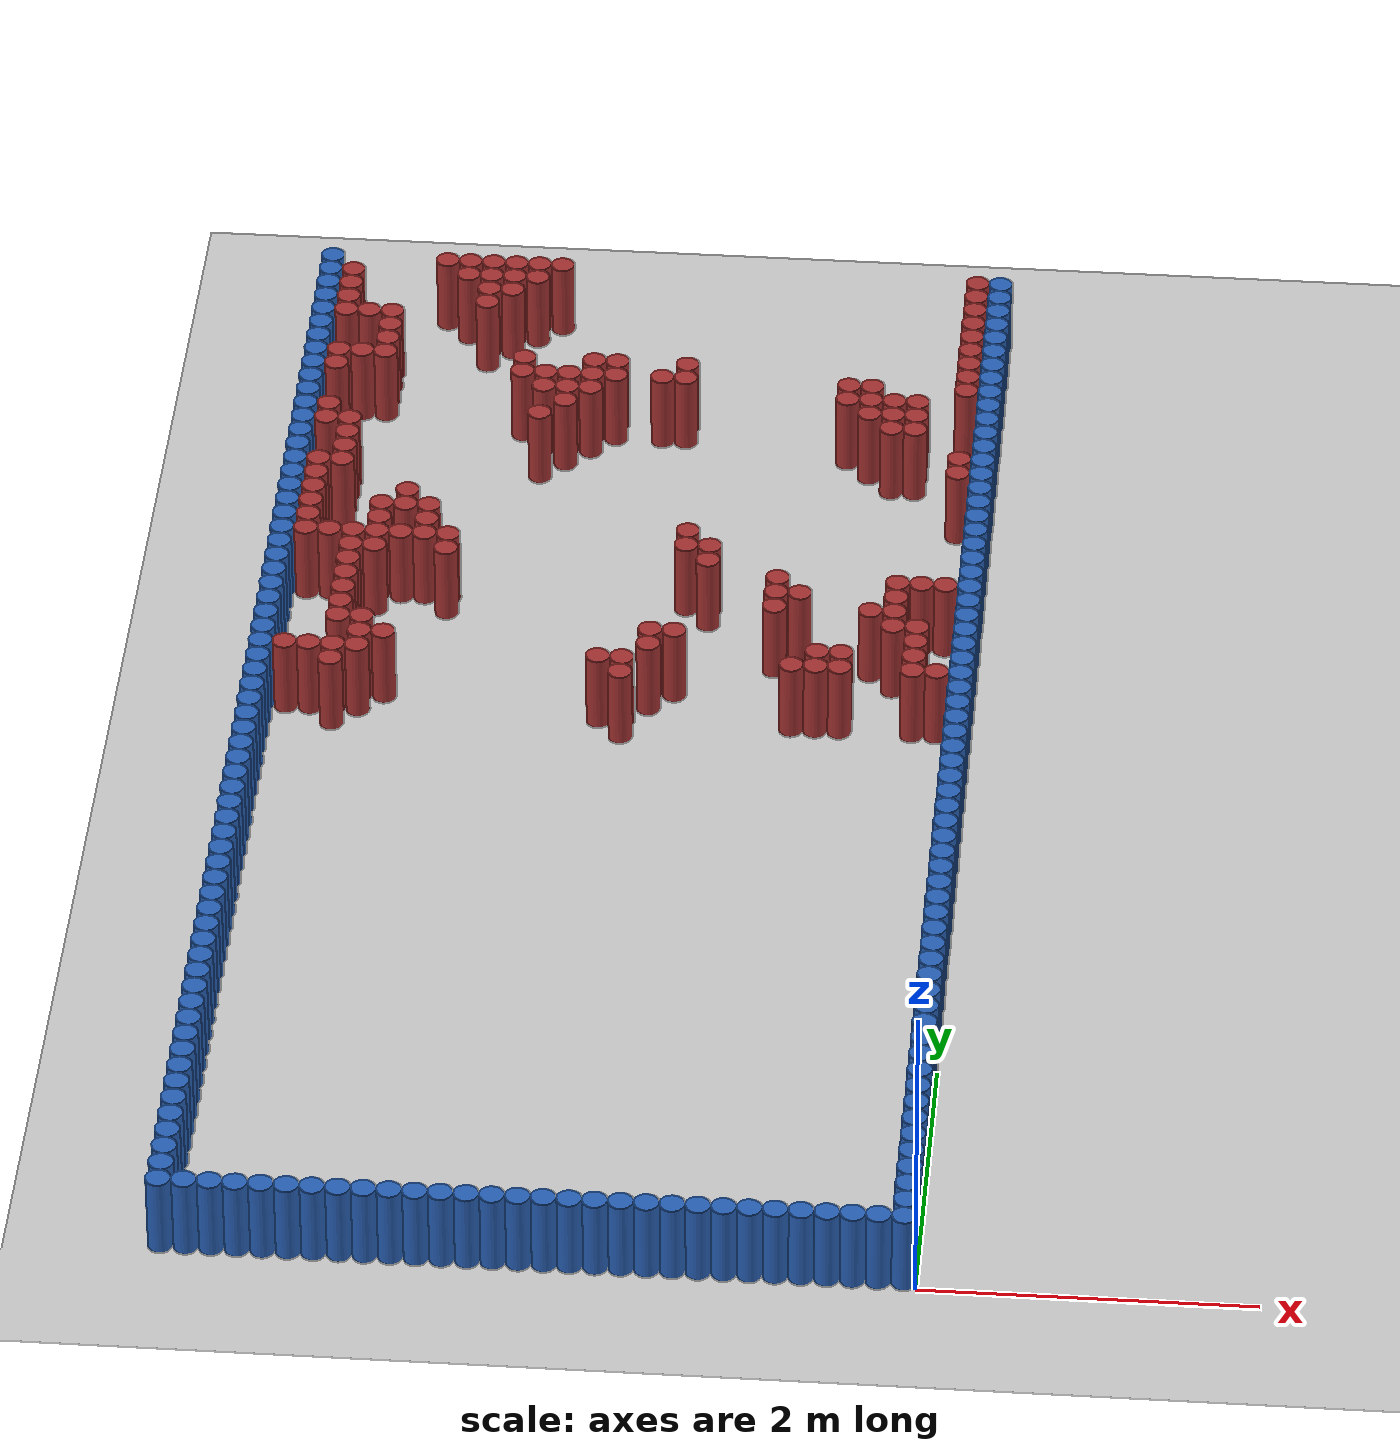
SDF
<sdf version="1.6">
 <world name="default">
  <light name="sun" type="directional">
   <pose>0 0 10 0 -0 0</pose>
   <diffuse>0.8 0.8 0.8 1</diffuse>
   <specular>0.1 0.1 0.1 1</specular>
   <attenuation>
    <range>1000</range>
    <constant>0.9</constant>
    <linear>0.01</linear>
    <quadratic>0.001</quadratic>
   </attenuation>
   <direction>-0.5 0.5 -1</direction>
  </light>
  <model name="ground_plane">
   <static>1</static>
   <link name="link">
    <collision name="collision">
     <geometry><plane><normal>0 0 1</normal><size>100 100</size></plane></geometry>
     <surface><friction><ode><mu>100</mu><mu2>50</mu2></ode></friction></surface>
    </collision>
    <visual name="visual">
     <cast_shadows>0</cast_shadows>
     <geometry><plane><normal>0 0 1</normal><size>100 100</size></plane></geometry>
     <material>
      <script><uri>file://media/materials/scripts/gazebo.material</uri><name>Gazebo/Grey</name></script>
     </material>
    </visual>
   </link>
  </model>
  <gravity>0 0 -9.8</gravity>
  <magnetic_field>6e-06 2.3e-05 -4.2e-05</magnetic_field>
  <atmosphere type="adiabatic"/>
  <physics name="default_physics" default="0" type="ode">
   <max_step_size>0.001</max_step_size>
   <real_time_factor>1</real_time_factor>
   <real_time_update_rate>0</real_time_update_rate>
  </physics>
  <scene><ambient>0.4 0.4 0.4 1</ambient><background>0.7 0.7 0.7 1</background><shadows>0</shadows></scene>
  <spherical_coordinates>
   <surface_model>EARTH_WGS84</surface_model>
   <latitude_deg>0</latitude_deg>
   <longitude_deg>0</longitude_deg>
   <elevation>0</elevation>
   <heading_deg>0</heading_deg>
  </spherical_coordinates>
  <model name="unit_cylinder_0">
   <static>1</static>
   <pose>-0.075000 0.075000 0.000000 0.000000 0.000000 0.000000</pose>
   <link name="link">
    <inertial>
     <mass>1</mass>
     <inertia><ixx>0.145833</ixx><ixy>0</ixy><ixz>0</ixz><iyy>0.145833</iyy><iyz>0</iyz><izz>0.125</izz></inertia>
    </inertial>
    <collision name="collision">
     <geometry><cylinder><radius>0.075000</radius><length>1</length></cylinder></geometry>
    </collision>
    <visual name="visual">
     <geometry><cylinder><radius>0.075000</radius><length>1</length></cylinder></geometry>
     <material>
      <ambient>0.152000 0.379000 0.720000 1</ambient>
      <diffuse>0.152000 0.379000 0.720000 1</diffuse>
     </material>
     <material>
      <script><name>Gazebo/Grey</name><uri>file://media/materials/scripts/gazebo.material</uri></script>
     </material>
    </visual>
   </link>
  </model>
  <model name="unit_cylinder_1">
   <static>1</static>
   <pose>-0.225000 0.075000 0.000000 0.000000 0.000000 0.000000</pose>
   <link name="link">
    <inertial>
     <mass>1</mass>
     <inertia><ixx>0.145833</ixx><ixy>0</ixy><ixz>0</ixz><iyy>0.145833</iyy><iyz>0</iyz><izz>0.125</izz></inertia>
    </inertial>
    <collision name="collision">
     <geometry><cylinder><radius>0.075000</radius><length>1</length></cylinder></geometry>
    </collision>
    <visual name="visual">
     <geometry><cylinder><radius>0.075000</radius><length>1</length></cylinder></geometry>
     <material>
      <ambient>0.152000 0.379000 0.720000 1</ambient>
      <diffuse>0.152000 0.379000 0.720000 1</diffuse>
     </material>
     <material>
      <script><name>Gazebo/Grey</name><uri>file://media/materials/scripts/gazebo.material</uri></script>
     </material>
    </visual>
   </link>
  </model>
  <model name="unit_cylinder_2">
   <static>1</static>
   <pose>-0.375000 0.075000 0.000000 0.000000 0.000000 0.000000</pose>
   <link name="link">
    <inertial>
     <mass>1</mass>
     <inertia><ixx>0.145833</ixx><ixy>0</ixy><ixz>0</ixz><iyy>0.145833</iyy><iyz>0</iyz><izz>0.125</izz></inertia>
    </inertial>
    <collision name="collision">
     <geometry><cylinder><radius>0.075000</radius><length>1</length></cylinder></geometry>
    </collision>
    <visual name="visual">
     <geometry><cylinder><radius>0.075000</radius><length>1</length></cylinder></geometry>
     <material>
      <ambient>0.152000 0.379000 0.720000 1</ambient>
      <diffuse>0.152000 0.379000 0.720000 1</diffuse>
     </material>
     <material>
      <script><name>Gazebo/Grey</name><uri>file://media/materials/scripts/gazebo.material</uri></script>
     </material>
    </visual>
   </link>
  </model>
  <model name="unit_cylinder_3">
   <static>1</static>
   <pose>-0.525000 0.075000 0.000000 0.000000 0.000000 0.000000</pose>
   <link name="link">
    <inertial>
     <mass>1</mass>
     <inertia><ixx>0.145833</ixx><ixy>0</ixy><ixz>0</ixz><iyy>0.145833</iyy><iyz>0</iyz><izz>0.125</izz></inertia>
    </inertial>
    <collision name="collision">
     <geometry><cylinder><radius>0.075000</radius><length>1</length></cylinder></geometry>
    </collision>
    <visual name="visual">
     <geometry><cylinder><radius>0.075000</radius><length>1</length></cylinder></geometry>
     <material>
      <ambient>0.152000 0.379000 0.720000 1</ambient>
      <diffuse>0.152000 0.379000 0.720000 1</diffuse>
     </material>
     <material>
      <script><name>Gazebo/Grey</name><uri>file://media/materials/scripts/gazebo.material</uri></script>
     </material>
    </visual>
   </link>
  </model>
  <model name="unit_cylinder_4">
   <static>1</static>
   <pose>-0.675000 0.075000 0.000000 0.000000 0.000000 0.000000</pose>
   <link name="link">
    <inertial>
     <mass>1</mass>
     <inertia><ixx>0.145833</ixx><ixy>0</ixy><ixz>0</ixz><iyy>0.145833</iyy><iyz>0</iyz><izz>0.125</izz></inertia>
    </inertial>
    <collision name="collision">
     <geometry><cylinder><radius>0.075000</radius><length>1</length></cylinder></geometry>
    </collision>
    <visual name="visual">
     <geometry><cylinder><radius>0.075000</radius><length>1</length></cylinder></geometry>
     <material>
      <ambient>0.152000 0.379000 0.720000 1</ambient>
      <diffuse>0.152000 0.379000 0.720000 1</diffuse>
     </material>
     <material>
      <script><name>Gazebo/Grey</name><uri>file://media/materials/scripts/gazebo.material</uri></script>
     </material>
    </visual>
   </link>
  </model>
  <model name="unit_cylinder_5">
   <static>1</static>
   <pose>-0.825000 0.075000 0.000000 0.000000 0.000000 0.000000</pose>
   <link name="link">
    <inertial>
     <mass>1</mass>
     <inertia><ixx>0.145833</ixx><ixy>0</ixy><ixz>0</ixz><iyy>0.145833</iyy><iyz>0</iyz><izz>0.125</izz></inertia>
    </inertial>
    <collision name="collision">
     <geometry><cylinder><radius>0.075000</radius><length>1</length></cylinder></geometry>
    </collision>
    <visual name="visual">
     <geometry><cylinder><radius>0.075000</radius><length>1</length></cylinder></geometry>
     <material>
      <ambient>0.152000 0.379000 0.720000 1</ambient>
      <diffuse>0.152000 0.379000 0.720000 1</diffuse>
     </material>
     <material>
      <script><name>Gazebo/Grey</name><uri>file://media/materials/scripts/gazebo.material</uri></script>
     </material>
    </visual>
   </link>
  </model>
  <model name="unit_cylinder_6">
   <static>1</static>
   <pose>-0.975000 0.075000 0.000000 0.000000 0.000000 0.000000</pose>
   <link name="link">
    <inertial>
     <mass>1</mass>
     <inertia><ixx>0.145833</ixx><ixy>0</ixy><ixz>0</ixz><iyy>0.145833</iyy><iyz>0</iyz><izz>0.125</izz></inertia>
    </inertial>
    <collision name="collision">
     <geometry><cylinder><radius>0.075000</radius><length>1</length></cylinder></geometry>
    </collision>
    <visual name="visual">
     <geometry><cylinder><radius>0.075000</radius><length>1</length></cylinder></geometry>
     <material>
      <ambient>0.152000 0.379000 0.720000 1</ambient>
      <diffuse>0.152000 0.379000 0.720000 1</diffuse>
     </material>
     <material>
      <script><name>Gazebo/Grey</name><uri>file://media/materials/scripts/gazebo.material</uri></script>
     </material>
    </visual>
   </link>
  </model>
  <model name="unit_cylinder_7">
   <static>1</static>
   <pose>-1.125000 0.075000 0.000000 0.000000 0.000000 0.000000</pose>
   <link name="link">
    <inertial>
     <mass>1</mass>
     <inertia><ixx>0.145833</ixx><ixy>0</ixy><ixz>0</ixz><iyy>0.145833</iyy><iyz>0</iyz><izz>0.125</izz></inertia>
    </inertial>
    <collision name="collision">
     <geometry><cylinder><radius>0.075000</radius><length>1</length></cylinder></geometry>
    </collision>
    <visual name="visual">
     <geometry><cylinder><radius>0.075000</radius><length>1</length></cylinder></geometry>
     <material>
      <ambient>0.152000 0.379000 0.720000 1</ambient>
      <diffuse>0.152000 0.379000 0.720000 1</diffuse>
     </material>
     <material>
      <script><name>Gazebo/Grey</name><uri>file://media/materials/scripts/gazebo.material</uri></script>
     </material>
    </visual>
   </link>
  </model>
  <model name="unit_cylinder_8">
   <static>1</static>
   <pose>-1.275000 0.075000 0.000000 0.000000 0.000000 0.000000</pose>
   <link name="link">
    <inertial>
     <mass>1</mass>
     <inertia><ixx>0.145833</ixx><ixy>0</ixy><ixz>0</ixz><iyy>0.145833</iyy><iyz>0</iyz><izz>0.125</izz></inertia>
    </inertial>
    <collision name="collision">
     <geometry><cylinder><radius>0.075000</radius><length>1</length></cylinder></geometry>
    </collision>
    <visual name="visual">
     <geometry><cylinder><radius>0.075000</radius><length>1</length></cylinder></geometry>
     <material>
      <ambient>0.152000 0.379000 0.720000 1</ambient>
      <diffuse>0.152000 0.379000 0.720000 1</diffuse>
     </material>
     <material>
      <script><name>Gazebo/Grey</name><uri>file://media/materials/scripts/gazebo.material</uri></script>
     </material>
    </visual>
   </link>
  </model>
  <model name="unit_cylinder_9">
   <static>1</static>
   <pose>-1.425000 0.075000 0.000000 0.000000 0.000000 0.000000</pose>
   <link name="link">
    <inertial>
     <mass>1</mass>
     <inertia><ixx>0.145833</ixx><ixy>0</ixy><ixz>0</ixz><iyy>0.145833</iyy><iyz>0</iyz><izz>0.125</izz></inertia>
    </inertial>
    <collision name="collision">
     <geometry><cylinder><radius>0.075000</radius><length>1</length></cylinder></geometry>
    </collision>
    <visual name="visual">
     <geometry><cylinder><radius>0.075000</radius><length>1</length></cylinder></geometry>
     <material>
      <ambient>0.152000 0.379000 0.720000 1</ambient>
      <diffuse>0.152000 0.379000 0.720000 1</diffuse>
     </material>
     <material>
      <script><name>Gazebo/Grey</name><uri>file://media/materials/scripts/gazebo.material</uri></script>
     </material>
    </visual>
   </link>
  </model>
  <model name="unit_cylinder_10">
   <static>1</static>
   <pose>-1.575000 0.075000 0.000000 0.000000 0.000000 0.000000</pose>
   <link name="link">
    <inertial>
     <mass>1</mass>
     <inertia><ixx>0.145833</ixx><ixy>0</ixy><ixz>0</ixz><iyy>0.145833</iyy><iyz>0</iyz><izz>0.125</izz></inertia>
    </inertial>
    <collision name="collision">
     <geometry><cylinder><radius>0.075000</radius><length>1</length></cylinder></geometry>
    </collision>
    <visual name="visual">
     <geometry><cylinder><radius>0.075000</radius><length>1</length></cylinder></geometry>
     <material>
      <ambient>0.152000 0.379000 0.720000 1</ambient>
      <diffuse>0.152000 0.379000 0.720000 1</diffuse>
     </material>
     <material>
      <script><name>Gazebo/Grey</name><uri>file://media/materials/scripts/gazebo.material</uri></script>
     </material>
    </visual>
   </link>
  </model>
  <model name="unit_cylinder_11">
   <static>1</static>
   <pose>-1.725000 0.075000 0.000000 0.000000 0.000000 0.000000</pose>
   <link name="link">
    <inertial>
     <mass>1</mass>
     <inertia><ixx>0.145833</ixx><ixy>0</ixy><ixz>0</ixz><iyy>0.145833</iyy><iyz>0</iyz><izz>0.125</izz></inertia>
    </inertial>
    <collision name="collision">
     <geometry><cylinder><radius>0.075000</radius><length>1</length></cylinder></geometry>
    </collision>
    <visual name="visual">
     <geometry><cylinder><radius>0.075000</radius><length>1</length></cylinder></geometry>
     <material>
      <ambient>0.152000 0.379000 0.720000 1</ambient>
      <diffuse>0.152000 0.379000 0.720000 1</diffuse>
     </material>
     <material>
      <script><name>Gazebo/Grey</name><uri>file://media/materials/scripts/gazebo.material</uri></script>
     </material>
    </visual>
   </link>
  </model>
  <model name="unit_cylinder_12">
   <static>1</static>
   <pose>-1.875000 0.075000 0.000000 0.000000 0.000000 0.000000</pose>
   <link name="link">
    <inertial>
     <mass>1</mass>
     <inertia><ixx>0.145833</ixx><ixy>0</ixy><ixz>0</ixz><iyy>0.145833</iyy><iyz>0</iyz><izz>0.125</izz></inertia>
    </inertial>
    <collision name="collision">
     <geometry><cylinder><radius>0.075000</radius><length>1</length></cylinder></geometry>
    </collision>
    <visual name="visual">
     <geometry><cylinder><radius>0.075000</radius><length>1</length></cylinder></geometry>
     <material>
      <ambient>0.152000 0.379000 0.720000 1</ambient>
      <diffuse>0.152000 0.379000 0.720000 1</diffuse>
     </material>
     <material>
      <script><name>Gazebo/Grey</name><uri>file://media/materials/scripts/gazebo.material</uri></script>
     </material>
    </visual>
   </link>
  </model>
  <model name="unit_cylinder_13">
   <static>1</static>
   <pose>-2.025000 0.075000 0.000000 0.000000 0.000000 0.000000</pose>
   <link name="link">
    <inertial>
     <mass>1</mass>
     <inertia><ixx>0.145833</ixx><ixy>0</ixy><ixz>0</ixz><iyy>0.145833</iyy><iyz>0</iyz><izz>0.125</izz></inertia>
    </inertial>
    <collision name="collision">
     <geometry><cylinder><radius>0.075000</radius><length>1</length></cylinder></geometry>
    </collision>
    <visual name="visual">
     <geometry><cylinder><radius>0.075000</radius><length>1</length></cylinder></geometry>
     <material>
      <ambient>0.152000 0.379000 0.720000 1</ambient>
      <diffuse>0.152000 0.379000 0.720000 1</diffuse>
     </material>
     <material>
      <script><name>Gazebo/Grey</name><uri>file://media/materials/scripts/gazebo.material</uri></script>
     </material>
    </visual>
   </link>
  </model>
  <model name="unit_cylinder_14">
   <static>1</static>
   <pose>-2.175000 0.075000 0.000000 0.000000 0.000000 0.000000</pose>
   <link name="link">
    <inertial>
     <mass>1</mass>
     <inertia><ixx>0.145833</ixx><ixy>0</ixy><ixz>0</ixz><iyy>0.145833</iyy><iyz>0</iyz><izz>0.125</izz></inertia>
    </inertial>
    <collision name="collision">
     <geometry><cylinder><radius>0.075000</radius><length>1</length></cylinder></geometry>
    </collision>
    <visual name="visual">
     <geometry><cylinder><radius>0.075000</radius><length>1</length></cylinder></geometry>
     <material>
      <ambient>0.152000 0.379000 0.720000 1</ambient>
      <diffuse>0.152000 0.379000 0.720000 1</diffuse>
     </material>
     <material>
      <script><name>Gazebo/Grey</name><uri>file://media/materials/scripts/gazebo.material</uri></script>
     </material>
    </visual>
   </link>
  </model>
  <model name="unit_cylinder_15">
   <static>1</static>
   <pose>-2.325000 0.075000 0.000000 0.000000 0.000000 0.000000</pose>
   <link name="link">
    <inertial>
     <mass>1</mass>
     <inertia><ixx>0.145833</ixx><ixy>0</ixy><ixz>0</ixz><iyy>0.145833</iyy><iyz>0</iyz><izz>0.125</izz></inertia>
    </inertial>
    <collision name="collision">
     <geometry><cylinder><radius>0.075000</radius><length>1</length></cylinder></geometry>
    </collision>
    <visual name="visual">
     <geometry><cylinder><radius>0.075000</radius><length>1</length></cylinder></geometry>
     <material>
      <ambient>0.152000 0.379000 0.720000 1</ambient>
      <diffuse>0.152000 0.379000 0.720000 1</diffuse>
     </material>
     <material>
      <script><name>Gazebo/Grey</name><uri>file://media/materials/scripts/gazebo.material</uri></script>
     </material>
    </visual>
   </link>
  </model>
  <model name="unit_cylinder_16">
   <static>1</static>
   <pose>-2.475000 0.075000 0.000000 0.000000 0.000000 0.000000</pose>
   <link name="link">
    <inertial>
     <mass>1</mass>
     <inertia><ixx>0.145833</ixx><ixy>0</ixy><ixz>0</ixz><iyy>0.145833</iyy><iyz>0</iyz><izz>0.125</izz></inertia>
    </inertial>
    <collision name="collision">
     <geometry><cylinder><radius>0.075000</radius><length>1</length></cylinder></geometry>
    </collision>
    <visual name="visual">
     <geometry><cylinder><radius>0.075000</radius><length>1</length></cylinder></geometry>
     <material>
      <ambient>0.152000 0.379000 0.720000 1</ambient>
      <diffuse>0.152000 0.379000 0.720000 1</diffuse>
     </material>
     <material>
      <script><name>Gazebo/Grey</name><uri>file://media/materials/scripts/gazebo.material</uri></script>
     </material>
    </visual>
   </link>
  </model>
  <model name="unit_cylinder_17">
   <static>1</static>
   <pose>-2.625000 0.075000 0.000000 0.000000 0.000000 0.000000</pose>
   <link name="link">
    <inertial>
     <mass>1</mass>
     <inertia><ixx>0.145833</ixx><ixy>0</ixy><ixz>0</ixz><iyy>0.145833</iyy><iyz>0</iyz><izz>0.125</izz></inertia>
    </inertial>
    <collision name="collision">
     <geometry><cylinder><radius>0.075000</radius><length>1</length></cylinder></geometry>
    </collision>
    <visual name="visual">
     <geometry><cylinder><radius>0.075000</radius><length>1</length></cylinder></geometry>
     <material>
      <ambient>0.152000 0.379000 0.720000 1</ambient>
      <diffuse>0.152000 0.379000 0.720000 1</diffuse>
     </material>
     <material>
      <script><name>Gazebo/Grey</name><uri>file://media/materials/scripts/gazebo.material</uri></script>
     </material>
    </visual>
   </link>
  </model>
  <model name="unit_cylinder_18">
   <static>1</static>
   <pose>-2.775000 0.075000 0.000000 0.000000 0.000000 0.000000</pose>
   <link name="link">
    <inertial>
     <mass>1</mass>
     <inertia><ixx>0.145833</ixx><ixy>0</ixy><ixz>0</ixz><iyy>0.145833</iyy><iyz>0</iyz><izz>0.125</izz></inertia>
    </inertial>
    <collision name="collision">
     <geometry><cylinder><radius>0.075000</radius><length>1</length></cylinder></geometry>
    </collision>
    <visual name="visual">
     <geometry><cylinder><radius>0.075000</radius><length>1</length></cylinder></geometry>
     <material>
      <ambient>0.152000 0.379000 0.720000 1</ambient>
      <diffuse>0.152000 0.379000 0.720000 1</diffuse>
     </material>
     <material>
      <script><name>Gazebo/Grey</name><uri>file://media/materials/scripts/gazebo.material</uri></script>
     </material>
    </visual>
   </link>
  </model>
  <model name="unit_cylinder_19">
   <static>1</static>
   <pose>-2.925000 0.075000 0.000000 0.000000 0.000000 0.000000</pose>
   <link name="link">
    <inertial>
     <mass>1</mass>
     <inertia><ixx>0.145833</ixx><ixy>0</ixy><ixz>0</ixz><iyy>0.145833</iyy><iyz>0</iyz><izz>0.125</izz></inertia>
    </inertial>
    <collision name="collision">
     <geometry><cylinder><radius>0.075000</radius><length>1</length></cylinder></geometry>
    </collision>
    <visual name="visual">
     <geometry><cylinder><radius>0.075000</radius><length>1</length></cylinder></geometry>
     <material>
      <ambient>0.152000 0.379000 0.720000 1</ambient>
      <diffuse>0.152000 0.379000 0.720000 1</diffuse>
     </material>
     <material>
      <script><name>Gazebo/Grey</name><uri>file://media/materials/scripts/gazebo.material</uri></script>
     </material>
    </visual>
   </link>
  </model>
  <model name="unit_cylinder_20">
   <static>1</static>
   <pose>-3.075000 0.075000 0.000000 0.000000 0.000000 0.000000</pose>
   <link name="link">
    <inertial>
     <mass>1</mass>
     <inertia><ixx>0.145833</ixx><ixy>0</ixy><ixz>0</ixz><iyy>0.145833</iyy><iyz>0</iyz><izz>0.125</izz></inertia>
    </inertial>
    <collision name="collision">
     <geometry><cylinder><radius>0.075000</radius><length>1</length></cylinder></geometry>
    </collision>
    <visual name="visual">
     <geometry><cylinder><radius>0.075000</radius><length>1</length></cylinder></geometry>
     <material>
      <ambient>0.152000 0.379000 0.720000 1</ambient>
      <diffuse>0.152000 0.379000 0.720000 1</diffuse>
     </material>
     <material>
      <script><name>Gazebo/Grey</name><uri>file://media/materials/scripts/gazebo.material</uri></script>
     </material>
    </visual>
   </link>
  </model>
  <model name="unit_cylinder_21">
   <static>1</static>
   <pose>-3.225000 0.075000 0.000000 0.000000 0.000000 0.000000</pose>
   <link name="link">
    <inertial>
     <mass>1</mass>
     <inertia><ixx>0.145833</ixx><ixy>0</ixy><ixz>0</ixz><iyy>0.145833</iyy><iyz>0</iyz><izz>0.125</izz></inertia>
    </inertial>
    <collision name="collision">
     <geometry><cylinder><radius>0.075000</radius><length>1</length></cylinder></geometry>
    </collision>
    <visual name="visual">
     <geometry><cylinder><radius>0.075000</radius><length>1</length></cylinder></geometry>
     <material>
      <ambient>0.152000 0.379000 0.720000 1</ambient>
      <diffuse>0.152000 0.379000 0.720000 1</diffuse>
     </material>
     <material>
      <script><name>Gazebo/Grey</name><uri>file://media/materials/scripts/gazebo.material</uri></script>
     </material>
    </visual>
   </link>
  </model>
  <model name="unit_cylinder_22">
   <static>1</static>
   <pose>-3.375000 0.075000 0.000000 0.000000 0.000000 0.000000</pose>
   <link name="link">
    <inertial>
     <mass>1</mass>
     <inertia><ixx>0.145833</ixx><ixy>0</ixy><ixz>0</ixz><iyy>0.145833</iyy><iyz>0</iyz><izz>0.125</izz></inertia>
    </inertial>
    <collision name="collision">
     <geometry><cylinder><radius>0.075000</radius><length>1</length></cylinder></geometry>
    </collision>
    <visual name="visual">
     <geometry><cylinder><radius>0.075000</radius><length>1</length></cylinder></geometry>
     <material>
      <ambient>0.152000 0.379000 0.720000 1</ambient>
      <diffuse>0.152000 0.379000 0.720000 1</diffuse>
     </material>
     <material>
      <script><name>Gazebo/Grey</name><uri>file://media/materials/scripts/gazebo.material</uri></script>
     </material>
    </visual>
   </link>
  </model>
  <model name="unit_cylinder_23">
   <static>1</static>
   <pose>-3.525000 0.075000 0.000000 0.000000 0.000000 0.000000</pose>
   <link name="link">
    <inertial>
     <mass>1</mass>
     <inertia><ixx>0.145833</ixx><ixy>0</ixy><ixz>0</ixz><iyy>0.145833</iyy><iyz>0</iyz><izz>0.125</izz></inertia>
    </inertial>
    <collision name="collision">
     <geometry><cylinder><radius>0.075000</radius><length>1</length></cylinder></geometry>
    </collision>
    <visual name="visual">
     <geometry><cylinder><radius>0.075000</radius><length>1</length></cylinder></geometry>
     <material>
      <ambient>0.152000 0.379000 0.720000 1</ambient>
      <diffuse>0.152000 0.379000 0.720000 1</diffuse>
     </material>
     <material>
      <script><name>Gazebo/Grey</name><uri>file://media/materials/scripts/gazebo.material</uri></script>
     </material>
    </visual>
   </link>
  </model>
  <model name="unit_cylinder_24">
   <static>1</static>
   <pose>-3.675000 0.075000 0.000000 0.000000 0.000000 0.000000</pose>
   <link name="link">
    <inertial>
     <mass>1</mass>
     <inertia><ixx>0.145833</ixx><ixy>0</ixy><ixz>0</ixz><iyy>0.145833</iyy><iyz>0</iyz><izz>0.125</izz></inertia>
    </inertial>
    <collision name="collision">
     <geometry><cylinder><radius>0.075000</radius><length>1</length></cylinder></geometry>
    </collision>
    <visual name="visual">
     <geometry><cylinder><radius>0.075000</radius><length>1</length></cylinder></geometry>
     <material>
      <ambient>0.152000 0.379000 0.720000 1</ambient>
      <diffuse>0.152000 0.379000 0.720000 1</diffuse>
     </material>
     <material>
      <script><name>Gazebo/Grey</name><uri>file://media/materials/scripts/gazebo.material</uri></script>
     </material>
    </visual>
   </link>
  </model>
  <model name="unit_cylinder_25">
   <static>1</static>
   <pose>-3.825000 0.075000 0.000000 0.000000 0.000000 0.000000</pose>
   <link name="link">
    <inertial>
     <mass>1</mass>
     <inertia><ixx>0.145833</ixx><ixy>0</ixy><ixz>0</ixz><iyy>0.145833</iyy><iyz>0</iyz><izz>0.125</izz></inertia>
    </inertial>
    <collision name="collision">
     <geometry><cylinder><radius>0.075000</radius><length>1</length></cylinder></geometry>
    </collision>
    <visual name="visual">
     <geometry><cylinder><radius>0.075000</radius><length>1</length></cylinder></geometry>
     <material>
      <ambient>0.152000 0.379000 0.720000 1</ambient>
      <diffuse>0.152000 0.379000 0.720000 1</diffuse>
     </material>
     <material>
      <script><name>Gazebo/Grey</name><uri>file://media/materials/scripts/gazebo.material</uri></script>
     </material>
    </visual>
   </link>
  </model>
  <model name="unit_cylinder_26">
   <static>1</static>
   <pose>-3.975000 0.075000 0.000000 0.000000 0.000000 0.000000</pose>
   <link name="link">
    <inertial>
     <mass>1</mass>
     <inertia><ixx>0.145833</ixx><ixy>0</ixy><ixz>0</ixz><iyy>0.145833</iyy><iyz>0</iyz><izz>0.125</izz></inertia>
    </inertial>
    <collision name="collision">
     <geometry><cylinder><radius>0.075000</radius><length>1</length></cylinder></geometry>
    </collision>
    <visual name="visual">
     <geometry><cylinder><radius>0.075000</radius><length>1</length></cylinder></geometry>
     <material>
      <ambient>0.152000 0.379000 0.720000 1</ambient>
      <diffuse>0.152000 0.379000 0.720000 1</diffuse>
     </material>
     <material>
      <script><name>Gazebo/Grey</name><uri>file://media/materials/scripts/gazebo.material</uri></script>
     </material>
    </visual>
   </link>
  </model>
  <model name="unit_cylinder_27">
   <static>1</static>
   <pose>-4.125000 0.075000 0.000000 0.000000 0.000000 0.000000</pose>
   <link name="link">
    <inertial>
     <mass>1</mass>
     <inertia><ixx>0.145833</ixx><ixy>0</ixy><ixz>0</ixz><iyy>0.145833</iyy><iyz>0</iyz><izz>0.125</izz></inertia>
    </inertial>
    <collision name="collision">
     <geometry><cylinder><radius>0.075000</radius><length>1</length></cylinder></geometry>
    </collision>
    <visual name="visual">
     <geometry><cylinder><radius>0.075000</radius><length>1</length></cylinder></geometry>
     <material>
      <ambient>0.152000 0.379000 0.720000 1</ambient>
      <diffuse>0.152000 0.379000 0.720000 1</diffuse>
     </material>
     <material>
      <script><name>Gazebo/Grey</name><uri>file://media/materials/scripts/gazebo.material</uri></script>
     </material>
    </visual>
   </link>
  </model>
  <model name="unit_cylinder_28">
   <static>1</static>
   <pose>-4.275000 0.075000 0.000000 0.000000 0.000000 0.000000</pose>
   <link name="link">
    <inertial>
     <mass>1</mass>
     <inertia><ixx>0.145833</ixx><ixy>0</ixy><ixz>0</ixz><iyy>0.145833</iyy><iyz>0</iyz><izz>0.125</izz></inertia>
    </inertial>
    <collision name="collision">
     <geometry><cylinder><radius>0.075000</radius><length>1</length></cylinder></geometry>
    </collision>
    <visual name="visual">
     <geometry><cylinder><radius>0.075000</radius><length>1</length></cylinder></geometry>
     <material>
      <ambient>0.152000 0.379000 0.720000 1</ambient>
      <diffuse>0.152000 0.379000 0.720000 1</diffuse>
     </material>
     <material>
      <script><name>Gazebo/Grey</name><uri>file://media/materials/scripts/gazebo.material</uri></script>
     </material>
    </visual>
   </link>
  </model>
  <model name="unit_cylinder_29">
   <static>1</static>
   <pose>-4.425000 0.075000 0.000000 0.000000 0.000000 0.000000</pose>
   <link name="link">
    <inertial>
     <mass>1</mass>
     <inertia><ixx>0.145833</ixx><ixy>0</ixy><ixz>0</ixz><iyy>0.145833</iyy><iyz>0</iyz><izz>0.125</izz></inertia>
    </inertial>
    <collision name="collision">
     <geometry><cylinder><radius>0.075000</radius><length>1</length></cylinder></geometry>
    </collision>
    <visual name="visual">
     <geometry><cylinder><radius>0.075000</radius><length>1</length></cylinder></geometry>
     <material>
      <ambient>0.152000 0.379000 0.720000 1</ambient>
      <diffuse>0.152000 0.379000 0.720000 1</diffuse>
     </material>
     <material>
      <script><name>Gazebo/Grey</name><uri>file://media/materials/scripts/gazebo.material</uri></script>
     </material>
    </visual>
   </link>
  </model>
  <model name="unit_cylinder_30">
   <static>1</static>
   <pose>-0.075000 0.225000 0.000000 0.000000 0.000000 0.000000</pose>
   <link name="link">
    <inertial>
     <mass>1</mass>
     <inertia><ixx>0.145833</ixx><ixy>0</ixy><ixz>0</ixz><iyy>0.145833</iyy><iyz>0</iyz><izz>0.125</izz></inertia>
    </inertial>
    <collision name="collision">
     <geometry><cylinder><radius>0.075000</radius><length>1</length></cylinder></geometry>
    </collision>
    <visual name="visual">
     <geometry><cylinder><radius>0.075000</radius><length>1</length></cylinder></geometry>
     <material>
      <ambient>0.152000 0.379000 0.720000 1</ambient>
      <diffuse>0.152000 0.379000 0.720000 1</diffuse>
     </material>
     <material>
      <script><name>Gazebo/Grey</name><uri>file://media/materials/scripts/gazebo.material</uri></script>
     </material>
    </visual>
   </link>
  </model>
  <model name="unit_cylinder_31">
   <static>1</static>
   <pose>-4.425000 0.225000 0.000000 0.000000 0.000000 0.000000</pose>
   <link name="link">
    <inertial>
     <mass>1</mass>
     <inertia><ixx>0.145833</ixx><ixy>0</ixy><ixz>0</ixz><iyy>0.145833</iyy><iyz>0</iyz><izz>0.125</izz></inertia>
    </inertial>
    <collision name="collision">
     <geometry><cylinder><radius>0.075000</radius><length>1</length></cylinder></geometry>
    </collision>
    <visual name="visual">
     <geometry><cylinder><radius>0.075000</radius><length>1</length></cylinder></geometry>
     <material>
      <ambient>0.152000 0.379000 0.720000 1</ambient>
      <diffuse>0.152000 0.379000 0.720000 1</diffuse>
     </material>
     <material>
      <script><name>Gazebo/Grey</name><uri>file://media/materials/scripts/gazebo.material</uri></script>
     </material>
    </visual>
   </link>
  </model>
  <model name="unit_cylinder_32">
   <static>1</static>
   <pose>-0.075000 0.375000 0.000000 0.000000 0.000000 0.000000</pose>
   <link name="link">
    <inertial>
     <mass>1</mass>
     <inertia><ixx>0.145833</ixx><ixy>0</ixy><ixz>0</ixz><iyy>0.145833</iyy><iyz>0</iyz><izz>0.125</izz></inertia>
    </inertial>
    <collision name="collision">
     <geometry><cylinder><radius>0.075000</radius><length>1</length></cylinder></geometry>
    </collision>
    <visual name="visual">
     <geometry><cylinder><radius>0.075000</radius><length>1</length></cylinder></geometry>
     <material>
      <ambient>0.152000 0.379000 0.720000 1</ambient>
      <diffuse>0.152000 0.379000 0.720000 1</diffuse>
     </material>
     <material>
      <script><name>Gazebo/Grey</name><uri>file://media/materials/scripts/gazebo.material</uri></script>
     </material>
    </visual>
   </link>
  </model>
  <model name="unit_cylinder_33">
   <static>1</static>
   <pose>-4.425000 0.375000 0.000000 0.000000 0.000000 0.000000</pose>
   <link name="link">
    <inertial>
     <mass>1</mass>
     <inertia><ixx>0.145833</ixx><ixy>0</ixy><ixz>0</ixz><iyy>0.145833</iyy><iyz>0</iyz><izz>0.125</izz></inertia>
    </inertial>
    <collision name="collision">
     <geometry><cylinder><radius>0.075000</radius><length>1</length></cylinder></geometry>
    </collision>
    <visual name="visual">
     <geometry><cylinder><radius>0.075000</radius><length>1</length></cylinder></geometry>
     <material>
      <ambient>0.152000 0.379000 0.720000 1</ambient>
      <diffuse>0.152000 0.379000 0.720000 1</diffuse>
     </material>
     <material>
      <script><name>Gazebo/Grey</name><uri>file://media/materials/scripts/gazebo.material</uri></script>
     </material>
    </visual>
   </link>
  </model>
  <model name="unit_cylinder_34">
   <static>1</static>
   <pose>-0.075000 0.525000 0.000000 0.000000 0.000000 0.000000</pose>
   <link name="link">
    <inertial>
     <mass>1</mass>
     <inertia><ixx>0.145833</ixx><ixy>0</ixy><ixz>0</ixz><iyy>0.145833</iyy><iyz>0</iyz><izz>0.125</izz></inertia>
    </inertial>
    <collision name="collision">
     <geometry><cylinder><radius>0.075000</radius><length>1</length></cylinder></geometry>
    </collision>
    <visual name="visual">
     <geometry><cylinder><radius>0.075000</radius><length>1</length></cylinder></geometry>
     <material>
      <ambient>0.152000 0.379000 0.720000 1</ambient>
      <diffuse>0.152000 0.379000 0.720000 1</diffuse>
     </material>
     <material>
      <script><name>Gazebo/Grey</name><uri>file://media/materials/scripts/gazebo.material</uri></script>
     </material>
    </visual>
   </link>
  </model>
  <model name="unit_cylinder_35">
   <static>1</static>
   <pose>-4.425000 0.525000 0.000000 0.000000 0.000000 0.000000</pose>
   <link name="link">
    <inertial>
     <mass>1</mass>
     <inertia><ixx>0.145833</ixx><ixy>0</ixy><ixz>0</ixz><iyy>0.145833</iyy><iyz>0</iyz><izz>0.125</izz></inertia>
    </inertial>
    <collision name="collision">
     <geometry><cylinder><radius>0.075000</radius><length>1</length></cylinder></geometry>
    </collision>
    <visual name="visual">
     <geometry><cylinder><radius>0.075000</radius><length>1</length></cylinder></geometry>
     <material>
      <ambient>0.152000 0.379000 0.720000 1</ambient>
      <diffuse>0.152000 0.379000 0.720000 1</diffuse>
     </material>
     <material>
      <script><name>Gazebo/Grey</name><uri>file://media/materials/scripts/gazebo.material</uri></script>
     </material>
    </visual>
   </link>
  </model>
  <model name="unit_cylinder_36">
   <static>1</static>
   <pose>-0.075000 0.675000 0.000000 0.000000 0.000000 0.000000</pose>
   <link name="link">
    <inertial>
     <mass>1</mass>
     <inertia><ixx>0.145833</ixx><ixy>0</ixy><ixz>0</ixz><iyy>0.145833</iyy><iyz>0</iyz><izz>0.125</izz></inertia>
    </inertial>
    <collision name="collision">
     <geometry><cylinder><radius>0.075000</radius><length>1</length></cylinder></geometry>
    </collision>
    <visual name="visual">
     <geometry><cylinder><radius>0.075000</radius><length>1</length></cylinder></geometry>
     <material>
      <ambient>0.152000 0.379000 0.720000 1</ambient>
      <diffuse>0.152000 0.379000 0.720000 1</diffuse>
     </material>
     <material>
      <script><name>Gazebo/Grey</name><uri>file://media/materials/scripts/gazebo.material</uri></script>
     </material>
    </visual>
   </link>
  </model>
  <model name="unit_cylinder_37">
   <static>1</static>
   <pose>-4.425000 0.675000 0.000000 0.000000 0.000000 0.000000</pose>
   <link name="link">
    <inertial>
     <mass>1</mass>
     <inertia><ixx>0.145833</ixx><ixy>0</ixy><ixz>0</ixz><iyy>0.145833</iyy><iyz>0</iyz><izz>0.125</izz></inertia>
    </inertial>
    <collision name="collision">
     <geometry><cylinder><radius>0.075000</radius><length>1</length></cylinder></geometry>
    </collision>
    <visual name="visual">
     <geometry><cylinder><radius>0.075000</radius><length>1</length></cylinder></geometry>
     <material>
      <ambient>0.152000 0.379000 0.720000 1</ambient>
      <diffuse>0.152000 0.379000 0.720000 1</diffuse>
     </material>
     <material>
      <script><name>Gazebo/Grey</name><uri>file://media/materials/scripts/gazebo.material</uri></script>
     </material>
    </visual>
   </link>
  </model>
  <model name="unit_cylinder_38">
   <static>1</static>
   <pose>-0.075000 0.825000 0.000000 0.000000 0.000000 0.000000</pose>
   <link name="link">
    <inertial>
     <mass>1</mass>
     <inertia><ixx>0.145833</ixx><ixy>0</ixy><ixz>0</ixz><iyy>0.145833</iyy><iyz>0</iyz><izz>0.125</izz></inertia>
    </inertial>
    <collision name="collision">
     <geometry><cylinder><radius>0.075000</radius><length>1</length></cylinder></geometry>
    </collision>
    <visual name="visual">
     <geometry><cylinder><radius>0.075000</radius><length>1</length></cylinder></geometry>
     <material>
      <ambient>0.152000 0.379000 0.720000 1</ambient>
      <diffuse>0.152000 0.379000 0.720000 1</diffuse>
     </material>
     <material>
      <script><name>Gazebo/Grey</name><uri>file://media/materials/scripts/gazebo.material</uri></script>
     </material>
    </visual>
   </link>
  </model>
  <model name="unit_cylinder_39">
   <static>1</static>
   <pose>-4.425000 0.825000 0.000000 0.000000 0.000000 0.000000</pose>
   <link name="link">
    <inertial>
     <mass>1</mass>
     <inertia><ixx>0.145833</ixx><ixy>0</ixy><ixz>0</ixz><iyy>0.145833</iyy><iyz>0</iyz><izz>0.125</izz></inertia>
    </inertial>
    <collision name="collision">
     <geometry><cylinder><radius>0.075000</radius><length>1</length></cylinder></geometry>
    </collision>
    <visual name="visual">
     <geometry><cylinder><radius>0.075000</radius><length>1</length></cylinder></geometry>
     <material>
      <ambient>0.152000 0.379000 0.720000 1</ambient>
      <diffuse>0.152000 0.379000 0.720000 1</diffuse>
     </material>
     <material>
      <script><name>Gazebo/Grey</name><uri>file://media/materials/scripts/gazebo.material</uri></script>
     </material>
    </visual>
   </link>
  </model>
  <model name="unit_cylinder_40">
   <static>1</static>
   <pose>-0.075000 0.975000 0.000000 0.000000 0.000000 0.000000</pose>
   <link name="link">
    <inertial>
     <mass>1</mass>
     <inertia><ixx>0.145833</ixx><ixy>0</ixy><ixz>0</ixz><iyy>0.145833</iyy><iyz>0</iyz><izz>0.125</izz></inertia>
    </inertial>
    <collision name="collision">
     <geometry><cylinder><radius>0.075000</radius><length>1</length></cylinder></geometry>
    </collision>
    <visual name="visual">
     <geometry><cylinder><radius>0.075000</radius><length>1</length></cylinder></geometry>
     <material>
      <ambient>0.152000 0.379000 0.720000 1</ambient>
      <diffuse>0.152000 0.379000 0.720000 1</diffuse>
     </material>
     <material>
      <script><name>Gazebo/Grey</name><uri>file://media/materials/scripts/gazebo.material</uri></script>
     </material>
    </visual>
   </link>
  </model>
  <model name="unit_cylinder_41">
   <static>1</static>
   <pose>-4.425000 0.975000 0.000000 0.000000 0.000000 0.000000</pose>
   <link name="link">
    <inertial>
     <mass>1</mass>
     <inertia><ixx>0.145833</ixx><ixy>0</ixy><ixz>0</ixz><iyy>0.145833</iyy><iyz>0</iyz><izz>0.125</izz></inertia>
    </inertial>
    <collision name="collision">
     <geometry><cylinder><radius>0.075000</radius><length>1</length></cylinder></geometry>
    </collision>
    <visual name="visual">
     <geometry><cylinder><radius>0.075000</radius><length>1</length></cylinder></geometry>
     <material>
      <ambient>0.152000 0.379000 0.720000 1</ambient>
      <diffuse>0.152000 0.379000 0.720000 1</diffuse>
     </material>
     <material>
      <script><name>Gazebo/Grey</name><uri>file://media/materials/scripts/gazebo.material</uri></script>
     </material>
    </visual>
   </link>
  </model>
  <model name="unit_cylinder_42">
   <static>1</static>
   <pose>-0.075000 1.125000 0.000000 0.000000 0.000000 0.000000</pose>
   <link name="link">
    <inertial>
     <mass>1</mass>
     <inertia><ixx>0.145833</ixx><ixy>0</ixy><ixz>0</ixz><iyy>0.145833</iyy><iyz>0</iyz><izz>0.125</izz></inertia>
    </inertial>
    <collision name="collision">
     <geometry><cylinder><radius>0.075000</radius><length>1</length></cylinder></geometry>
    </collision>
    <visual name="visual">
     <geometry><cylinder><radius>0.075000</radius><length>1</length></cylinder></geometry>
     <material>
      <ambient>0.152000 0.379000 0.720000 1</ambient>
      <diffuse>0.152000 0.379000 0.720000 1</diffuse>
     </material>
     <material>
      <script><name>Gazebo/Grey</name><uri>file://media/materials/scripts/gazebo.material</uri></script>
     </material>
    </visual>
   </link>
  </model>
  <model name="unit_cylinder_43">
   <static>1</static>
   <pose>-4.425000 1.125000 0.000000 0.000000 0.000000 0.000000</pose>
   <link name="link">
    <inertial>
     <mass>1</mass>
     <inertia><ixx>0.145833</ixx><ixy>0</ixy><ixz>0</ixz><iyy>0.145833</iyy><iyz>0</iyz><izz>0.125</izz></inertia>
    </inertial>
    <collision name="collision">
     <geometry><cylinder><radius>0.075000</radius><length>1</length></cylinder></geometry>
    </collision>
    <visual name="visual">
     <geometry><cylinder><radius>0.075000</radius><length>1</length></cylinder></geometry>
     <material>
      <ambient>0.152000 0.379000 0.720000 1</ambient>
      <diffuse>0.152000 0.379000 0.720000 1</diffuse>
     </material>
     <material>
      <script><name>Gazebo/Grey</name><uri>file://media/materials/scripts/gazebo.material</uri></script>
     </material>
    </visual>
   </link>
  </model>
  <model name="unit_cylinder_44">
   <static>1</static>
   <pose>-0.075000 1.275000 0.000000 0.000000 0.000000 0.000000</pose>
   <link name="link">
    <inertial>
     <mass>1</mass>
     <inertia><ixx>0.145833</ixx><ixy>0</ixy><ixz>0</ixz><iyy>0.145833</iyy><iyz>0</iyz><izz>0.125</izz></inertia>
    </inertial>
    <collision name="collision">
     <geometry><cylinder><radius>0.075000</radius><length>1</length></cylinder></geometry>
    </collision>
    <visual name="visual">
     <geometry><cylinder><radius>0.075000</radius><length>1</length></cylinder></geometry>
     <material>
      <ambient>0.152000 0.379000 0.720000 1</ambient>
      <diffuse>0.152000 0.379000 0.720000 1</diffuse>
     </material>
     <material>
      <script><name>Gazebo/Grey</name><uri>file://media/materials/scripts/gazebo.material</uri></script>
     </material>
    </visual>
   </link>
  </model>
  <model name="unit_cylinder_45">
   <static>1</static>
   <pose>-4.425000 1.275000 0.000000 0.000000 0.000000 0.000000</pose>
   <link name="link">
    <inertial>
     <mass>1</mass>
     <inertia><ixx>0.145833</ixx><ixy>0</ixy><ixz>0</ixz><iyy>0.145833</iyy><iyz>0</iyz><izz>0.125</izz></inertia>
    </inertial>
    <collision name="collision">
     <geometry><cylinder><radius>0.075000</radius><length>1</length></cylinder></geometry>
    </collision>
    <visual name="visual">
     <geometry><cylinder><radius>0.075000</radius><length>1</length></cylinder></geometry>
     <material>
      <ambient>0.152000 0.379000 0.720000 1</ambient>
      <diffuse>0.152000 0.379000 0.720000 1</diffuse>
     </material>
     <material>
      <script><name>Gazebo/Grey</name><uri>file://media/materials/scripts/gazebo.material</uri></script>
     </material>
    </visual>
   </link>
  </model>
  <model name="unit_cylinder_46">
   <static>1</static>
   <pose>-0.075000 1.425000 0.000000 0.000000 0.000000 0.000000</pose>
   <link name="link">
    <inertial>
     <mass>1</mass>
     <inertia><ixx>0.145833</ixx><ixy>0</ixy><ixz>0</ixz><iyy>0.145833</iyy><iyz>0</iyz><izz>0.125</izz></inertia>
    </inertial>
    <collision name="collision">
     <geometry><cylinder><radius>0.075000</radius><length>1</length></cylinder></geometry>
    </collision>
    <visual name="visual">
     <geometry><cylinder><radius>0.075000</radius><length>1</length></cylinder></geometry>
     <material>
      <ambient>0.152000 0.379000 0.720000 1</ambient>
      <diffuse>0.152000 0.379000 0.720000 1</diffuse>
     </material>
     <material>
      <script><name>Gazebo/Grey</name><uri>file://media/materials/scripts/gazebo.material</uri></script>
     </material>
    </visual>
   </link>
  </model>
  <model name="unit_cylinder_47">
   <static>1</static>
   <pose>-4.425000 1.425000 0.000000 0.000000 0.000000 0.000000</pose>
   <link name="link">
    <inertial>
     <mass>1</mass>
     <inertia><ixx>0.145833</ixx><ixy>0</ixy><ixz>0</ixz><iyy>0.145833</iyy><iyz>0</iyz><izz>0.125</izz></inertia>
    </inertial>
    <collision name="collision">
     <geometry><cylinder><radius>0.075000</radius><length>1</length></cylinder></geometry>
    </collision>
    <visual name="visual">
     <geometry><cylinder><radius>0.075000</radius><length>1</length></cylinder></geometry>
     <material>
      <ambient>0.152000 0.379000 0.720000 1</ambient>
      <diffuse>0.152000 0.379000 0.720000 1</diffuse>
     </material>
     <material>
      <script><name>Gazebo/Grey</name><uri>file://media/materials/scripts/gazebo.material</uri></script>
     </material>
    </visual>
   </link>
  </model>
  <model name="unit_cylinder_48">
   <static>1</static>
   <pose>-0.075000 1.575000 0.000000 0.000000 0.000000 0.000000</pose>
   <link name="link">
    <inertial>
     <mass>1</mass>
     <inertia><ixx>0.145833</ixx><ixy>0</ixy><ixz>0</ixz><iyy>0.145833</iyy><iyz>0</iyz><izz>0.125</izz></inertia>
    </inertial>
    <collision name="collision">
     <geometry><cylinder><radius>0.075000</radius><length>1</length></cylinder></geometry>
    </collision>
    <visual name="visual">
     <geometry><cylinder><radius>0.075000</radius><length>1</length></cylinder></geometry>
     <material>
      <ambient>0.152000 0.379000 0.720000 1</ambient>
      <diffuse>0.152000 0.379000 0.720000 1</diffuse>
     </material>
     <material>
      <script><name>Gazebo/Grey</name><uri>file://media/materials/scripts/gazebo.material</uri></script>
     </material>
    </visual>
   </link>
  </model>
  <model name="unit_cylinder_49">
   <static>1</static>
   <pose>-4.425000 1.575000 0.000000 0.000000 0.000000 0.000000</pose>
   <link name="link">
    <inertial>
     <mass>1</mass>
     <inertia><ixx>0.145833</ixx><ixy>0</ixy><ixz>0</ixz><iyy>0.145833</iyy><iyz>0</iyz><izz>0.125</izz></inertia>
    </inertial>
    <collision name="collision">
     <geometry><cylinder><radius>0.075000</radius><length>1</length></cylinder></geometry>
    </collision>
    <visual name="visual">
     <geometry><cylinder><radius>0.075000</radius><length>1</length></cylinder></geometry>
     <material>
      <ambient>0.152000 0.379000 0.720000 1</ambient>
      <diffuse>0.152000 0.379000 0.720000 1</diffuse>
     </material>
     <material>
      <script><name>Gazebo/Grey</name><uri>file://media/materials/scripts/gazebo.material</uri></script>
     </material>
    </visual>
   </link>
  </model>
  <model name="unit_cylinder_50">
   <static>1</static>
   <pose>-0.075000 1.725000 0.000000 0.000000 0.000000 0.000000</pose>
   <link name="link">
    <inertial>
     <mass>1</mass>
     <inertia><ixx>0.145833</ixx><ixy>0</ixy><ixz>0</ixz><iyy>0.145833</iyy><iyz>0</iyz><izz>0.125</izz></inertia>
    </inertial>
    <collision name="collision">
     <geometry><cylinder><radius>0.075000</radius><length>1</length></cylinder></geometry>
    </collision>
    <visual name="visual">
     <geometry><cylinder><radius>0.075000</radius><length>1</length></cylinder></geometry>
     <material>
      <ambient>0.152000 0.379000 0.720000 1</ambient>
      <diffuse>0.152000 0.379000 0.720000 1</diffuse>
     </material>
     <material>
      <script><name>Gazebo/Grey</name><uri>file://media/materials/scripts/gazebo.material</uri></script>
     </material>
    </visual>
   </link>
  </model>
  <model name="unit_cylinder_51">
   <static>1</static>
   <pose>-4.425000 1.725000 0.000000 0.000000 0.000000 0.000000</pose>
   <link name="link">
    <inertial>
     <mass>1</mass>
     <inertia><ixx>0.145833</ixx><ixy>0</ixy><ixz>0</ixz><iyy>0.145833</iyy><iyz>0</iyz><izz>0.125</izz></inertia>
    </inertial>
    <collision name="collision">
     <geometry><cylinder><radius>0.075000</radius><length>1</length></cylinder></geometry>
    </collision>
    <visual name="visual">
     <geometry><cylinder><radius>0.075000</radius><length>1</length></cylinder></geometry>
     <material>
      <ambient>0.152000 0.379000 0.720000 1</ambient>
      <diffuse>0.152000 0.379000 0.720000 1</diffuse>
     </material>
     <material>
      <script><name>Gazebo/Grey</name><uri>file://media/materials/scripts/gazebo.material</uri></script>
     </material>
    </visual>
   </link>
  </model>
  <model name="unit_cylinder_52">
   <static>1</static>
   <pose>-0.075000 1.875000 0.000000 0.000000 0.000000 0.000000</pose>
   <link name="link">
    <inertial>
     <mass>1</mass>
     <inertia><ixx>0.145833</ixx><ixy>0</ixy><ixz>0</ixz><iyy>0.145833</iyy><iyz>0</iyz><izz>0.125</izz></inertia>
    </inertial>
    <collision name="collision">
     <geometry><cylinder><radius>0.075000</radius><length>1</length></cylinder></geometry>
    </collision>
    <visual name="visual">
     <geometry><cylinder><radius>0.075000</radius><length>1</length></cylinder></geometry>
     <material>
      <ambient>0.152000 0.379000 0.720000 1</ambient>
      <diffuse>0.152000 0.379000 0.720000 1</diffuse>
     </material>
     <material>
      <script><name>Gazebo/Grey</name><uri>file://media/materials/scripts/gazebo.material</uri></script>
     </material>
    </visual>
   </link>
  </model>
  <model name="unit_cylinder_53">
   <static>1</static>
   <pose>-4.425000 1.875000 0.000000 0.000000 0.000000 0.000000</pose>
   <link name="link">
    <inertial>
     <mass>1</mass>
     <inertia><ixx>0.145833</ixx><ixy>0</ixy><ixz>0</ixz><iyy>0.145833</iyy><iyz>0</iyz><izz>0.125</izz></inertia>
    </inertial>
    <collision name="collision">
     <geometry><cylinder><radius>0.075000</radius><length>1</length></cylinder></geometry>
    </collision>
    <visual name="visual">
     <geometry><cylinder><radius>0.075000</radius><length>1</length></cylinder></geometry>
     <material>
      <ambient>0.152000 0.379000 0.720000 1</ambient>
      <diffuse>0.152000 0.379000 0.720000 1</diffuse>
     </material>
     <material>
      <script><name>Gazebo/Grey</name><uri>file://media/materials/scripts/gazebo.material</uri></script>
     </material>
    </visual>
   </link>
  </model>
  <model name="unit_cylinder_54">
   <static>1</static>
   <pose>-0.075000 2.025000 0.000000 0.000000 0.000000 0.000000</pose>
   <link name="link">
    <inertial>
     <mass>1</mass>
     <inertia><ixx>0.145833</ixx><ixy>0</ixy><ixz>0</ixz><iyy>0.145833</iyy><iyz>0</iyz><izz>0.125</izz></inertia>
    </inertial>
    <collision name="collision">
     <geometry><cylinder><radius>0.075000</radius><length>1</length></cylinder></geometry>
    </collision>
    <visual name="visual">
     <geometry><cylinder><radius>0.075000</radius><length>1</length></cylinder></geometry>
     <material>
      <ambient>0.152000 0.379000 0.720000 1</ambient>
      <diffuse>0.152000 0.379000 0.720000 1</diffuse>
     </material>
     <material>
      <script><name>Gazebo/Grey</name><uri>file://media/materials/scripts/gazebo.material</uri></script>
     </material>
    </visual>
   </link>
  </model>
  <model name="unit_cylinder_55">
   <static>1</static>
   <pose>-4.425000 2.025000 0.000000 0.000000 0.000000 0.000000</pose>
   <link name="link">
    <inertial>
     <mass>1</mass>
     <inertia><ixx>0.145833</ixx><ixy>0</ixy><ixz>0</ixz><iyy>0.145833</iyy><iyz>0</iyz><izz>0.125</izz></inertia>
    </inertial>
    <collision name="collision">
     <geometry><cylinder><radius>0.075000</radius><length>1</length></cylinder></geometry>
    </collision>
    <visual name="visual">
     <geometry><cylinder><radius>0.075000</radius><length>1</length></cylinder></geometry>
     <material>
      <ambient>0.152000 0.379000 0.720000 1</ambient>
      <diffuse>0.152000 0.379000 0.720000 1</diffuse>
     </material>
     <material>
      <script><name>Gazebo/Grey</name><uri>file://media/materials/scripts/gazebo.material</uri></script>
     </material>
    </visual>
   </link>
  </model>
  <model name="unit_cylinder_56">
   <static>1</static>
   <pose>-0.075000 2.175000 0.000000 0.000000 0.000000 0.000000</pose>
   <link name="link">
    <inertial>
     <mass>1</mass>
     <inertia><ixx>0.145833</ixx><ixy>0</ixy><ixz>0</ixz><iyy>0.145833</iyy><iyz>0</iyz><izz>0.125</izz></inertia>
    </inertial>
    <collision name="collision">
     <geometry><cylinder><radius>0.075000</radius><length>1</length></cylinder></geometry>
    </collision>
    <visual name="visual">
     <geometry><cylinder><radius>0.075000</radius><length>1</length></cylinder></geometry>
     <material>
      <ambient>0.152000 0.379000 0.720000 1</ambient>
      <diffuse>0.152000 0.379000 0.720000 1</diffuse>
     </material>
     <material>
      <script><name>Gazebo/Grey</name><uri>file://media/materials/scripts/gazebo.material</uri></script>
     </material>
    </visual>
   </link>
  </model>
  <model name="unit_cylinder_57">
   <static>1</static>
   <pose>-4.425000 2.175000 0.000000 0.000000 0.000000 0.000000</pose>
   <link name="link">
    <inertial>
     <mass>1</mass>
     <inertia><ixx>0.145833</ixx><ixy>0</ixy><ixz>0</ixz><iyy>0.145833</iyy><iyz>0</iyz><izz>0.125</izz></inertia>
    </inertial>
    <collision name="collision">
     <geometry><cylinder><radius>0.075000</radius><length>1</length></cylinder></geometry>
    </collision>
    <visual name="visual">
     <geometry><cylinder><radius>0.075000</radius><length>1</length></cylinder></geometry>
     <material>
      <ambient>0.152000 0.379000 0.720000 1</ambient>
      <diffuse>0.152000 0.379000 0.720000 1</diffuse>
     </material>
     <material>
      <script><name>Gazebo/Grey</name><uri>file://media/materials/scripts/gazebo.material</uri></script>
     </material>
    </visual>
   </link>
  </model>
  <model name="unit_cylinder_58">
   <static>1</static>
   <pose>-0.075000 2.325000 0.000000 0.000000 0.000000 0.000000</pose>
   <link name="link">
    <inertial>
     <mass>1</mass>
     <inertia><ixx>0.145833</ixx><ixy>0</ixy><ixz>0</ixz><iyy>0.145833</iyy><iyz>0</iyz><izz>0.125</izz></inertia>
    </inertial>
    <collision name="collision">
     <geometry><cylinder><radius>0.075000</radius><length>1</length></cylinder></geometry>
    </collision>
    <visual name="visual">
     <geometry><cylinder><radius>0.075000</radius><length>1</length></cylinder></geometry>
     <material>
      <ambient>0.152000 0.379000 0.720000 1</ambient>
      <diffuse>0.152000 0.379000 0.720000 1</diffuse>
     </material>
     <material>
      <script><name>Gazebo/Grey</name><uri>file://media/materials/scripts/gazebo.material</uri></script>
     </material>
    </visual>
   </link>
  </model>
  <model name="unit_cylinder_59">
   <static>1</static>
   <pose>-4.425000 2.325000 0.000000 0.000000 0.000000 0.000000</pose>
   <link name="link">
    <inertial>
     <mass>1</mass>
     <inertia><ixx>0.145833</ixx><ixy>0</ixy><ixz>0</ixz><iyy>0.145833</iyy><iyz>0</iyz><izz>0.125</izz></inertia>
    </inertial>
    <collision name="collision">
     <geometry><cylinder><radius>0.075000</radius><length>1</length></cylinder></geometry>
    </collision>
    <visual name="visual">
     <geometry><cylinder><radius>0.075000</radius><length>1</length></cylinder></geometry>
     <material>
      <ambient>0.152000 0.379000 0.720000 1</ambient>
      <diffuse>0.152000 0.379000 0.720000 1</diffuse>
     </material>
     <material>
      <script><name>Gazebo/Grey</name><uri>file://media/materials/scripts/gazebo.material</uri></script>
     </material>
    </visual>
   </link>
  </model>
  <model name="unit_cylinder_60">
   <static>1</static>
   <pose>-0.075000 2.475000 0.000000 0.000000 0.000000 0.000000</pose>
   <link name="link">
    <inertial>
     <mass>1</mass>
     <inertia><ixx>0.145833</ixx><ixy>0</ixy><ixz>0</ixz><iyy>0.145833</iyy><iyz>0</iyz><izz>0.125</izz></inertia>
    </inertial>
    <collision name="collision">
     <geometry><cylinder><radius>0.075000</radius><length>1</length></cylinder></geometry>
    </collision>
    <visual name="visual">
     <geometry><cylinder><radius>0.075000</radius><length>1</length></cylinder></geometry>
     <material>
      <ambient>0.152000 0.379000 0.720000 1</ambient>
      <diffuse>0.152000 0.379000 0.720000 1</diffuse>
     </material>
     <material>
      <script><name>Gazebo/Grey</name><uri>file://media/materials/scripts/gazebo.material</uri></script>
     </material>
    </visual>
   </link>
  </model>
  <model name="unit_cylinder_61">
   <static>1</static>
   <pose>-4.425000 2.475000 0.000000 0.000000 0.000000 0.000000</pose>
   <link name="link">
    <inertial>
     <mass>1</mass>
     <inertia><ixx>0.145833</ixx><ixy>0</ixy><ixz>0</ixz><iyy>0.145833</iyy><iyz>0</iyz><izz>0.125</izz></inertia>
    </inertial>
    <collision name="collision">
     <geometry><cylinder><radius>0.075000</radius><length>1</length></cylinder></geometry>
    </collision>
    <visual name="visual">
     <geometry><cylinder><radius>0.075000</radius><length>1</length></cylinder></geometry>
     <material>
      <ambient>0.152000 0.379000 0.720000 1</ambient>
      <diffuse>0.152000 0.379000 0.720000 1</diffuse>
     </material>
     <material>
      <script><name>Gazebo/Grey</name><uri>file://media/materials/scripts/gazebo.material</uri></script>
     </material>
    </visual>
   </link>
  </model>
  <model name="unit_cylinder_62">
   <static>1</static>
   <pose>-0.075000 2.625000 0.000000 0.000000 0.000000 0.000000</pose>
   <link name="link">
    <inertial>
     <mass>1</mass>
     <inertia><ixx>0.145833</ixx><ixy>0</ixy><ixz>0</ixz><iyy>0.145833</iyy><iyz>0</iyz><izz>0.125</izz></inertia>
    </inertial>
    <collision name="collision">
     <geometry><cylinder><radius>0.075000</radius><length>1</length></cylinder></geometry>
    </collision>
    <visual name="visual">
     <geometry><cylinder><radius>0.075000</radius><length>1</length></cylinder></geometry>
     <material>
      <ambient>0.152000 0.379000 0.720000 1</ambient>
      <diffuse>0.152000 0.379000 0.720000 1</diffuse>
     </material>
     <material>
      <script><name>Gazebo/Grey</name><uri>file://media/materials/scripts/gazebo.material</uri></script>
     </material>
    </visual>
   </link>
  </model>
  <model name="unit_cylinder_63">
   <static>1</static>
   <pose>-4.425000 2.625000 0.000000 0.000000 0.000000 0.000000</pose>
   <link name="link">
    <inertial>
     <mass>1</mass>
     <inertia><ixx>0.145833</ixx><ixy>0</ixy><ixz>0</ixz><iyy>0.145833</iyy><iyz>0</iyz><izz>0.125</izz></inertia>
    </inertial>
    <collision name="collision">
     <geometry><cylinder><radius>0.075000</radius><length>1</length></cylinder></geometry>
    </collision>
    <visual name="visual">
     <geometry><cylinder><radius>0.075000</radius><length>1</length></cylinder></geometry>
     <material>
      <ambient>0.152000 0.379000 0.720000 1</ambient>
      <diffuse>0.152000 0.379000 0.720000 1</diffuse>
     </material>
     <material>
      <script><name>Gazebo/Grey</name><uri>file://media/materials/scripts/gazebo.material</uri></script>
     </material>
    </visual>
   </link>
  </model>
  <model name="unit_cylinder_64">
   <static>1</static>
   <pose>-0.075000 2.775000 0.000000 0.000000 0.000000 0.000000</pose>
   <link name="link">
    <inertial>
     <mass>1</mass>
     <inertia><ixx>0.145833</ixx><ixy>0</ixy><ixz>0</ixz><iyy>0.145833</iyy><iyz>0</iyz><izz>0.125</izz></inertia>
    </inertial>
    <collision name="collision">
     <geometry><cylinder><radius>0.075000</radius><length>1</length></cylinder></geometry>
    </collision>
    <visual name="visual">
     <geometry><cylinder><radius>0.075000</radius><length>1</length></cylinder></geometry>
     <material>
      <ambient>0.152000 0.379000 0.720000 1</ambient>
      <diffuse>0.152000 0.379000 0.720000 1</diffuse>
     </material>
     <material>
      <script><name>Gazebo/Grey</name><uri>file://media/materials/scripts/gazebo.material</uri></script>
     </material>
    </visual>
   </link>
  </model>
  <model name="unit_cylinder_65">
   <static>1</static>
   <pose>-4.425000 2.775000 0.000000 0.000000 0.000000 0.000000</pose>
   <link name="link">
    <inertial>
     <mass>1</mass>
     <inertia><ixx>0.145833</ixx><ixy>0</ixy><ixz>0</ixz><iyy>0.145833</iyy><iyz>0</iyz><izz>0.125</izz></inertia>
    </inertial>
    <collision name="collision">
     <geometry><cylinder><radius>0.075000</radius><length>1</length></cylinder></geometry>
    </collision>
    <visual name="visual">
     <geometry><cylinder><radius>0.075000</radius><length>1</length></cylinder></geometry>
     <material>
      <ambient>0.152000 0.379000 0.720000 1</ambient>
      <diffuse>0.152000 0.379000 0.720000 1</diffuse>
     </material>
     <material>
      <script><name>Gazebo/Grey</name><uri>file://media/materials/scripts/gazebo.material</uri></script>
     </material>
    </visual>
   </link>
  </model>
  <model name="unit_cylinder_66">
   <static>1</static>
   <pose>-0.075000 2.925000 0.000000 0.000000 0.000000 0.000000</pose>
   <link name="link">
    <inertial>
     <mass>1</mass>
     <inertia><ixx>0.145833</ixx><ixy>0</ixy><ixz>0</ixz><iyy>0.145833</iyy><iyz>0</iyz><izz>0.125</izz></inertia>
    </inertial>
    <collision name="collision">
     <geometry><cylinder><radius>0.075000</radius><length>1</length></cylinder></geometry>
    </collision>
    <visual name="visual">
     <geometry><cylinder><radius>0.075000</radius><length>1</length></cylinder></geometry>
     <material>
      <ambient>0.152000 0.379000 0.720000 1</ambient>
      <diffuse>0.152000 0.379000 0.720000 1</diffuse>
     </material>
     <material>
      <script><name>Gazebo/Grey</name><uri>file://media/materials/scripts/gazebo.material</uri></script>
     </material>
    </visual>
   </link>
  </model>
  <model name="unit_cylinder_67">
   <static>1</static>
   <pose>-4.425000 2.925000 0.000000 0.000000 0.000000 0.000000</pose>
   <link name="link">
    <inertial>
     <mass>1</mass>
     <inertia><ixx>0.145833</ixx><ixy>0</ixy><ixz>0</ixz><iyy>0.145833</iyy><iyz>0</iyz><izz>0.125</izz></inertia>
    </inertial>
    <collision name="collision">
     <geometry><cylinder><radius>0.075000</radius><length>1</length></cylinder></geometry>
    </collision>
    <visual name="visual">
     <geometry><cylinder><radius>0.075000</radius><length>1</length></cylinder></geometry>
     <material>
      <ambient>0.152000 0.379000 0.720000 1</ambient>
      <diffuse>0.152000 0.379000 0.720000 1</diffuse>
     </material>
     <material>
      <script><name>Gazebo/Grey</name><uri>file://media/materials/scripts/gazebo.material</uri></script>
     </material>
    </visual>
   </link>
  </model>
  <model name="unit_cylinder_68">
   <static>1</static>
   <pose>-0.075000 3.075000 0.000000 0.000000 0.000000 0.000000</pose>
   <link name="link">
    <inertial>
     <mass>1</mass>
     <inertia><ixx>0.145833</ixx><ixy>0</ixy><ixz>0</ixz><iyy>0.145833</iyy><iyz>0</iyz><izz>0.125</izz></inertia>
    </inertial>
    <collision name="collision">
     <geometry><cylinder><radius>0.075000</radius><length>1</length></cylinder></geometry>
    </collision>
    <visual name="visual">
     <geometry><cylinder><radius>0.075000</radius><length>1</length></cylinder></geometry>
     <material>
      <ambient>0.152000 0.379000 0.720000 1</ambient>
      <diffuse>0.152000 0.379000 0.720000 1</diffuse>
     </material>
     <material>
      <script><name>Gazebo/Grey</name><uri>file://media/materials/scripts/gazebo.material</uri></script>
     </material>
    </visual>
   </link>
  </model>
  <model name="unit_cylinder_69">
   <static>1</static>
   <pose>-4.425000 3.075000 0.000000 0.000000 0.000000 0.000000</pose>
   <link name="link">
    <inertial>
     <mass>1</mass>
     <inertia><ixx>0.145833</ixx><ixy>0</ixy><ixz>0</ixz><iyy>0.145833</iyy><iyz>0</iyz><izz>0.125</izz></inertia>
    </inertial>
    <collision name="collision">
     <geometry><cylinder><radius>0.075000</radius><length>1</length></cylinder></geometry>
    </collision>
    <visual name="visual">
     <geometry><cylinder><radius>0.075000</radius><length>1</length></cylinder></geometry>
     <material>
      <ambient>0.152000 0.379000 0.720000 1</ambient>
      <diffuse>0.152000 0.379000 0.720000 1</diffuse>
     </material>
     <material>
      <script><name>Gazebo/Grey</name><uri>file://media/materials/scripts/gazebo.material</uri></script>
     </material>
    </visual>
   </link>
  </model>
  <model name="unit_cylinder_70">
   <static>1</static>
   <pose>-0.075000 3.225000 0.000000 0.000000 0.000000 0.000000</pose>
   <link name="link">
    <inertial>
     <mass>1</mass>
     <inertia><ixx>0.145833</ixx><ixy>0</ixy><ixz>0</ixz><iyy>0.145833</iyy><iyz>0</iyz><izz>0.125</izz></inertia>
    </inertial>
    <collision name="collision">
     <geometry><cylinder><radius>0.075000</radius><length>1</length></cylinder></geometry>
    </collision>
    <visual name="visual">
     <geometry><cylinder><radius>0.075000</radius><length>1</length></cylinder></geometry>
     <material>
      <ambient>0.152000 0.379000 0.720000 1</ambient>
      <diffuse>0.152000 0.379000 0.720000 1</diffuse>
     </material>
     <material>
      <script><name>Gazebo/Grey</name><uri>file://media/materials/scripts/gazebo.material</uri></script>
     </material>
    </visual>
   </link>
  </model>
  <model name="unit_cylinder_71">
   <static>1</static>
   <pose>-4.425000 3.225000 0.000000 0.000000 0.000000 0.000000</pose>
   <link name="link">
    <inertial>
     <mass>1</mass>
     <inertia><ixx>0.145833</ixx><ixy>0</ixy><ixz>0</ixz><iyy>0.145833</iyy><iyz>0</iyz><izz>0.125</izz></inertia>
    </inertial>
    <collision name="collision">
     <geometry><cylinder><radius>0.075000</radius><length>1</length></cylinder></geometry>
    </collision>
    <visual name="visual">
     <geometry><cylinder><radius>0.075000</radius><length>1</length></cylinder></geometry>
     <material>
      <ambient>0.152000 0.379000 0.720000 1</ambient>
      <diffuse>0.152000 0.379000 0.720000 1</diffuse>
     </material>
     <material>
      <script><name>Gazebo/Grey</name><uri>file://media/materials/scripts/gazebo.material</uri></script>
     </material>
    </visual>
   </link>
  </model>
  <model name="unit_cylinder_72">
   <static>1</static>
   <pose>-0.075000 3.375000 0.000000 0.000000 0.000000 0.000000</pose>
   <link name="link">
    <inertial>
     <mass>1</mass>
     <inertia><ixx>0.145833</ixx><ixy>0</ixy><ixz>0</ixz><iyy>0.145833</iyy><iyz>0</iyz><izz>0.125</izz></inertia>
    </inertial>
    <collision name="collision">
     <geometry><cylinder><radius>0.075000</radius><length>1</length></cylinder></geometry>
    </collision>
    <visual name="visual">
     <geometry><cylinder><radius>0.075000</radius><length>1</length></cylinder></geometry>
     <material>
      <ambient>0.152000 0.379000 0.720000 1</ambient>
      <diffuse>0.152000 0.379000 0.720000 1</diffuse>
     </material>
     <material>
      <script><name>Gazebo/Grey</name><uri>file://media/materials/scripts/gazebo.material</uri></script>
     </material>
    </visual>
   </link>
  </model>
  <model name="unit_cylinder_73">
   <static>1</static>
   <pose>-4.425000 3.375000 0.000000 0.000000 0.000000 0.000000</pose>
   <link name="link">
    <inertial>
     <mass>1</mass>
     <inertia><ixx>0.145833</ixx><ixy>0</ixy><ixz>0</ixz><iyy>0.145833</iyy><iyz>0</iyz><izz>0.125</izz></inertia>
    </inertial>
    <collision name="collision">
     <geometry><cylinder><radius>0.075000</radius><length>1</length></cylinder></geometry>
    </collision>
    <visual name="visual">
     <geometry><cylinder><radius>0.075000</radius><length>1</length></cylinder></geometry>
     <material>
      <ambient>0.152000 0.379000 0.720000 1</ambient>
      <diffuse>0.152000 0.379000 0.720000 1</diffuse>
     </material>
     <material>
      <script><name>Gazebo/Grey</name><uri>file://media/materials/scripts/gazebo.material</uri></script>
     </material>
    </visual>
   </link>
  </model>
  <model name="unit_cylinder_74">
   <static>1</static>
   <pose>-0.075000 3.525000 0.000000 0.000000 0.000000 0.000000</pose>
   <link name="link">
    <inertial>
     <mass>1</mass>
     <inertia><ixx>0.145833</ixx><ixy>0</ixy><ixz>0</ixz><iyy>0.145833</iyy><iyz>0</iyz><izz>0.125</izz></inertia>
    </inertial>
    <collision name="collision">
     <geometry><cylinder><radius>0.075000</radius><length>1</length></cylinder></geometry>
    </collision>
    <visual name="visual">
     <geometry><cylinder><radius>0.075000</radius><length>1</length></cylinder></geometry>
     <material>
      <ambient>0.152000 0.379000 0.720000 1</ambient>
      <diffuse>0.152000 0.379000 0.720000 1</diffuse>
     </material>
     <material>
      <script><name>Gazebo/Grey</name><uri>file://media/materials/scripts/gazebo.material</uri></script>
     </material>
    </visual>
   </link>
  </model>
  <model name="unit_cylinder_75">
   <static>1</static>
   <pose>-4.425000 3.525000 0.000000 0.000000 0.000000 0.000000</pose>
   <link name="link">
    <inertial>
     <mass>1</mass>
     <inertia><ixx>0.145833</ixx><ixy>0</ixy><ixz>0</ixz><iyy>0.145833</iyy><iyz>0</iyz><izz>0.125</izz></inertia>
    </inertial>
    <collision name="collision">
     <geometry><cylinder><radius>0.075000</radius><length>1</length></cylinder></geometry>
    </collision>
    <visual name="visual">
     <geometry><cylinder><radius>0.075000</radius><length>1</length></cylinder></geometry>
     <material>
      <ambient>0.152000 0.379000 0.720000 1</ambient>
      <diffuse>0.152000 0.379000 0.720000 1</diffuse>
     </material>
     <material>
      <script><name>Gazebo/Grey</name><uri>file://media/materials/scripts/gazebo.material</uri></script>
     </material>
    </visual>
   </link>
  </model>
  <model name="unit_cylinder_76">
   <static>1</static>
   <pose>-0.075000 3.675000 0.000000 0.000000 0.000000 0.000000</pose>
   <link name="link">
    <inertial>
     <mass>1</mass>
     <inertia><ixx>0.145833</ixx><ixy>0</ixy><ixz>0</ixz><iyy>0.145833</iyy><iyz>0</iyz><izz>0.125</izz></inertia>
    </inertial>
    <collision name="collision">
     <geometry><cylinder><radius>0.075000</radius><length>1</length></cylinder></geometry>
    </collision>
    <visual name="visual">
     <geometry><cylinder><radius>0.075000</radius><length>1</length></cylinder></geometry>
     <material>
      <ambient>0.152000 0.379000 0.720000 1</ambient>
      <diffuse>0.152000 0.379000 0.720000 1</diffuse>
     </material>
     <material>
      <script><name>Gazebo/Grey</name><uri>file://media/materials/scripts/gazebo.material</uri></script>
     </material>
    </visual>
   </link>
  </model>
  <model name="unit_cylinder_77">
   <static>1</static>
   <pose>-4.425000 3.675000 0.000000 0.000000 0.000000 0.000000</pose>
   <link name="link">
    <inertial>
     <mass>1</mass>
     <inertia><ixx>0.145833</ixx><ixy>0</ixy><ixz>0</ixz><iyy>0.145833</iyy><iyz>0</iyz><izz>0.125</izz></inertia>
    </inertial>
    <collision name="collision">
     <geometry><cylinder><radius>0.075000</radius><length>1</length></cylinder></geometry>
    </collision>
    <visual name="visual">
     <geometry><cylinder><radius>0.075000</radius><length>1</length></cylinder></geometry>
     <material>
      <ambient>0.152000 0.379000 0.720000 1</ambient>
      <diffuse>0.152000 0.379000 0.720000 1</diffuse>
     </material>
     <material>
      <script><name>Gazebo/Grey</name><uri>file://media/materials/scripts/gazebo.material</uri></script>
     </material>
    </visual>
   </link>
  </model>
  <model name="unit_cylinder_78">
   <static>1</static>
   <pose>-0.075000 3.825000 0.000000 0.000000 0.000000 0.000000</pose>
   <link name="link">
    <inertial>
     <mass>1</mass>
     <inertia><ixx>0.145833</ixx><ixy>0</ixy><ixz>0</ixz><iyy>0.145833</iyy><iyz>0</iyz><izz>0.125</izz></inertia>
    </inertial>
    <collision name="collision">
     <geometry><cylinder><radius>0.075000</radius><length>1</length></cylinder></geometry>
    </collision>
    <visual name="visual">
     <geometry><cylinder><radius>0.075000</radius><length>1</length></cylinder></geometry>
     <material>
      <ambient>0.152000 0.379000 0.720000 1</ambient>
      <diffuse>0.152000 0.379000 0.720000 1</diffuse>
     </material>
     <material>
      <script><name>Gazebo/Grey</name><uri>file://media/materials/scripts/gazebo.material</uri></script>
     </material>
    </visual>
   </link>
  </model>
  <model name="unit_cylinder_79">
   <static>1</static>
   <pose>-4.425000 3.825000 0.000000 0.000000 0.000000 0.000000</pose>
   <link name="link">
    <inertial>
     <mass>1</mass>
     <inertia><ixx>0.145833</ixx><ixy>0</ixy><ixz>0</ixz><iyy>0.145833</iyy><iyz>0</iyz><izz>0.125</izz></inertia>
    </inertial>
    <collision name="collision">
     <geometry><cylinder><radius>0.075000</radius><length>1</length></cylinder></geometry>
    </collision>
    <visual name="visual">
     <geometry><cylinder><radius>0.075000</radius><length>1</length></cylinder></geometry>
     <material>
      <ambient>0.152000 0.379000 0.720000 1</ambient>
      <diffuse>0.152000 0.379000 0.720000 1</diffuse>
     </material>
     <material>
      <script><name>Gazebo/Grey</name><uri>file://media/materials/scripts/gazebo.material</uri></script>
     </material>
    </visual>
   </link>
  </model>
  <model name="unit_cylinder_80">
   <static>1</static>
   <pose>-0.075000 3.975000 0.000000 0.000000 0.000000 0.000000</pose>
   <link name="link">
    <inertial>
     <mass>1</mass>
     <inertia><ixx>0.145833</ixx><ixy>0</ixy><ixz>0</ixz><iyy>0.145833</iyy><iyz>0</iyz><izz>0.125</izz></inertia>
    </inertial>
    <collision name="collision">
     <geometry><cylinder><radius>0.075000</radius><length>1</length></cylinder></geometry>
    </collision>
    <visual name="visual">
     <geometry><cylinder><radius>0.075000</radius><length>1</length></cylinder></geometry>
     <material>
      <ambient>0.152000 0.379000 0.720000 1</ambient>
      <diffuse>0.152000 0.379000 0.720000 1</diffuse>
     </material>
     <material>
      <script><name>Gazebo/Grey</name><uri>file://media/materials/scripts/gazebo.material</uri></script>
     </material>
    </visual>
   </link>
  </model>
  <model name="unit_cylinder_81">
   <static>1</static>
   <pose>-4.425000 3.975000 0.000000 0.000000 0.000000 0.000000</pose>
   <link name="link">
    <inertial>
     <mass>1</mass>
     <inertia><ixx>0.145833</ixx><ixy>0</ixy><ixz>0</ixz><iyy>0.145833</iyy><iyz>0</iyz><izz>0.125</izz></inertia>
    </inertial>
    <collision name="collision">
     <geometry><cylinder><radius>0.075000</radius><length>1</length></cylinder></geometry>
    </collision>
    <visual name="visual">
     <geometry><cylinder><radius>0.075000</radius><length>1</length></cylinder></geometry>
     <material>
      <ambient>0.152000 0.379000 0.720000 1</ambient>
      <diffuse>0.152000 0.379000 0.720000 1</diffuse>
     </material>
     <material>
      <script><name>Gazebo/Grey</name><uri>file://media/materials/scripts/gazebo.material</uri></script>
     </material>
    </visual>
   </link>
  </model>
  <model name="unit_cylinder_82">
   <static>1</static>
   <pose>-0.075000 4.125000 0.000000 0.000000 0.000000 0.000000</pose>
   <link name="link">
    <inertial>
     <mass>1</mass>
     <inertia><ixx>0.145833</ixx><ixy>0</ixy><ixz>0</ixz><iyy>0.145833</iyy><iyz>0</iyz><izz>0.125</izz></inertia>
    </inertial>
    <collision name="collision">
     <geometry><cylinder><radius>0.075000</radius><length>1</length></cylinder></geometry>
    </collision>
    <visual name="visual">
     <geometry><cylinder><radius>0.075000</radius><length>1</length></cylinder></geometry>
     <material>
      <ambient>0.152000 0.379000 0.720000 1</ambient>
      <diffuse>0.152000 0.379000 0.720000 1</diffuse>
     </material>
     <material>
      <script><name>Gazebo/Grey</name><uri>file://media/materials/scripts/gazebo.material</uri></script>
     </material>
    </visual>
   </link>
  </model>
  <model name="unit_cylinder_83">
   <static>1</static>
   <pose>-4.425000 4.125000 0.000000 0.000000 0.000000 0.000000</pose>
   <link name="link">
    <inertial>
     <mass>1</mass>
     <inertia><ixx>0.145833</ixx><ixy>0</ixy><ixz>0</ixz><iyy>0.145833</iyy><iyz>0</iyz><izz>0.125</izz></inertia>
    </inertial>
    <collision name="collision">
     <geometry><cylinder><radius>0.075000</radius><length>1</length></cylinder></geometry>
    </collision>
    <visual name="visual">
     <geometry><cylinder><radius>0.075000</radius><length>1</length></cylinder></geometry>
     <material>
      <ambient>0.152000 0.379000 0.720000 1</ambient>
      <diffuse>0.152000 0.379000 0.720000 1</diffuse>
     </material>
     <material>
      <script><name>Gazebo/Grey</name><uri>file://media/materials/scripts/gazebo.material</uri></script>
     </material>
    </visual>
   </link>
  </model>
  <model name="unit_cylinder_84">
   <static>1</static>
   <pose>-0.075000 4.275000 0.000000 0.000000 0.000000 0.000000</pose>
   <link name="link">
    <inertial>
     <mass>1</mass>
     <inertia><ixx>0.145833</ixx><ixy>0</ixy><ixz>0</ixz><iyy>0.145833</iyy><iyz>0</iyz><izz>0.125</izz></inertia>
    </inertial>
    <collision name="collision">
     <geometry><cylinder><radius>0.075000</radius><length>1</length></cylinder></geometry>
    </collision>
    <visual name="visual">
     <geometry><cylinder><radius>0.075000</radius><length>1</length></cylinder></geometry>
     <material>
      <ambient>0.152000 0.379000 0.720000 1</ambient>
      <diffuse>0.152000 0.379000 0.720000 1</diffuse>
     </material>
     <material>
      <script><name>Gazebo/Grey</name><uri>file://media/materials/scripts/gazebo.material</uri></script>
     </material>
    </visual>
   </link>
  </model>
  <model name="unit_cylinder_85">
   <static>1</static>
   <pose>-4.425000 4.275000 0.000000 0.000000 0.000000 0.000000</pose>
   <link name="link">
    <inertial>
     <mass>1</mass>
     <inertia><ixx>0.145833</ixx><ixy>0</ixy><ixz>0</ixz><iyy>0.145833</iyy><iyz>0</iyz><izz>0.125</izz></inertia>
    </inertial>
    <collision name="collision">
     <geometry><cylinder><radius>0.075000</radius><length>1</length></cylinder></geometry>
    </collision>
    <visual name="visual">
     <geometry><cylinder><radius>0.075000</radius><length>1</length></cylinder></geometry>
     <material>
      <ambient>0.152000 0.379000 0.720000 1</ambient>
      <diffuse>0.152000 0.379000 0.720000 1</diffuse>
     </material>
     <material>
      <script><name>Gazebo/Grey</name><uri>file://media/materials/scripts/gazebo.material</uri></script>
     </material>
    </visual>
   </link>
  </model>
  <model name="unit_cylinder_86">
   <static>1</static>
   <pose>-0.075000 4.425000 0.000000 0.000000 0.000000 0.000000</pose>
   <link name="link">
    <inertial>
     <mass>1</mass>
     <inertia><ixx>0.145833</ixx><ixy>0</ixy><ixz>0</ixz><iyy>0.145833</iyy><iyz>0</iyz><izz>0.125</izz></inertia>
    </inertial>
    <collision name="collision">
     <geometry><cylinder><radius>0.075000</radius><length>1</length></cylinder></geometry>
    </collision>
    <visual name="visual">
     <geometry><cylinder><radius>0.075000</radius><length>1</length></cylinder></geometry>
     <material>
      <ambient>0.152000 0.379000 0.720000 1</ambient>
      <diffuse>0.152000 0.379000 0.720000 1</diffuse>
     </material>
     <material>
      <script><name>Gazebo/Grey</name><uri>file://media/materials/scripts/gazebo.material</uri></script>
     </material>
    </visual>
   </link>
  </model>
  <model name="unit_cylinder_87">
   <static>1</static>
   <pose>-4.425000 4.425000 0.000000 0.000000 0.000000 0.000000</pose>
   <link name="link">
    <inertial>
     <mass>1</mass>
     <inertia><ixx>0.145833</ixx><ixy>0</ixy><ixz>0</ixz><iyy>0.145833</iyy><iyz>0</iyz><izz>0.125</izz></inertia>
    </inertial>
    <collision name="collision">
     <geometry><cylinder><radius>0.075000</radius><length>1</length></cylinder></geometry>
    </collision>
    <visual name="visual">
     <geometry><cylinder><radius>0.075000</radius><length>1</length></cylinder></geometry>
     <material>
      <ambient>0.152000 0.379000 0.720000 1</ambient>
      <diffuse>0.152000 0.379000 0.720000 1</diffuse>
     </material>
     <material>
      <script><name>Gazebo/Grey</name><uri>file://media/materials/scripts/gazebo.material</uri></script>
     </material>
    </visual>
   </link>
  </model>
  <model name="unit_cylinder_88">
   <static>1</static>
   <pose>-0.075000 4.575000 0.000000 0.000000 0.000000 0.000000</pose>
   <link name="link">
    <inertial>
     <mass>1</mass>
     <inertia><ixx>0.145833</ixx><ixy>0</ixy><ixz>0</ixz><iyy>0.145833</iyy><iyz>0</iyz><izz>0.125</izz></inertia>
    </inertial>
    <collision name="collision">
     <geometry><cylinder><radius>0.075000</radius><length>1</length></cylinder></geometry>
    </collision>
    <visual name="visual">
     <geometry><cylinder><radius>0.075000</radius><length>1</length></cylinder></geometry>
     <material>
      <ambient>0.152000 0.379000 0.720000 1</ambient>
      <diffuse>0.152000 0.379000 0.720000 1</diffuse>
     </material>
     <material>
      <script><name>Gazebo/Grey</name><uri>file://media/materials/scripts/gazebo.material</uri></script>
     </material>
    </visual>
   </link>
  </model>
  <model name="unit_cylinder_89">
   <static>1</static>
   <pose>-4.425000 4.575000 0.000000 0.000000 0.000000 0.000000</pose>
   <link name="link">
    <inertial>
     <mass>1</mass>
     <inertia><ixx>0.145833</ixx><ixy>0</ixy><ixz>0</ixz><iyy>0.145833</iyy><iyz>0</iyz><izz>0.125</izz></inertia>
    </inertial>
    <collision name="collision">
     <geometry><cylinder><radius>0.075000</radius><length>1</length></cylinder></geometry>
    </collision>
    <visual name="visual">
     <geometry><cylinder><radius>0.075000</radius><length>1</length></cylinder></geometry>
     <material>
      <ambient>0.152000 0.379000 0.720000 1</ambient>
      <diffuse>0.152000 0.379000 0.720000 1</diffuse>
     </material>
     <material>
      <script><name>Gazebo/Grey</name><uri>file://media/materials/scripts/gazebo.material</uri></script>
     </material>
    </visual>
   </link>
  </model>
  <model name="unit_cylinder_90">
   <static>1</static>
   <pose>-0.075000 4.725000 0.000000 0.000000 0.000000 0.000000</pose>
   <link name="link">
    <inertial>
     <mass>1</mass>
     <inertia><ixx>0.145833</ixx><ixy>0</ixy><ixz>0</ixz><iyy>0.145833</iyy><iyz>0</iyz><izz>0.125</izz></inertia>
    </inertial>
    <collision name="collision">
     <geometry><cylinder><radius>0.075000</radius><length>1</length></cylinder></geometry>
    </collision>
    <visual name="visual">
     <geometry><cylinder><radius>0.075000</radius><length>1</length></cylinder></geometry>
     <material>
      <ambient>0.152000 0.379000 0.720000 1</ambient>
      <diffuse>0.152000 0.379000 0.720000 1</diffuse>
     </material>
     <material>
      <script><name>Gazebo/Grey</name><uri>file://media/materials/scripts/gazebo.material</uri></script>
     </material>
    </visual>
   </link>
  </model>
  <model name="unit_cylinder_91">
   <static>1</static>
   <pose>-4.425000 4.725000 0.000000 0.000000 0.000000 0.000000</pose>
   <link name="link">
    <inertial>
     <mass>1</mass>
     <inertia><ixx>0.145833</ixx><ixy>0</ixy><ixz>0</ixz><iyy>0.145833</iyy><iyz>0</iyz><izz>0.125</izz></inertia>
    </inertial>
    <collision name="collision">
     <geometry><cylinder><radius>0.075000</radius><length>1</length></cylinder></geometry>
    </collision>
    <visual name="visual">
     <geometry><cylinder><radius>0.075000</radius><length>1</length></cylinder></geometry>
     <material>
      <ambient>0.152000 0.379000 0.720000 1</ambient>
      <diffuse>0.152000 0.379000 0.720000 1</diffuse>
     </material>
     <material>
      <script><name>Gazebo/Grey</name><uri>file://media/materials/scripts/gazebo.material</uri></script>
     </material>
    </visual>
   </link>
  </model>
  <model name="unit_cylinder_92">
   <static>1</static>
   <pose>-0.075000 4.875000 0.000000 0.000000 0.000000 0.000000</pose>
   <link name="link">
    <inertial>
     <mass>1</mass>
     <inertia><ixx>0.145833</ixx><ixy>0</ixy><ixz>0</ixz><iyy>0.145833</iyy><iyz>0</iyz><izz>0.125</izz></inertia>
    </inertial>
    <collision name="collision">
     <geometry><cylinder><radius>0.075000</radius><length>1</length></cylinder></geometry>
    </collision>
    <visual name="visual">
     <geometry><cylinder><radius>0.075000</radius><length>1</length></cylinder></geometry>
     <material>
      <ambient>0.152000 0.379000 0.720000 1</ambient>
      <diffuse>0.152000 0.379000 0.720000 1</diffuse>
     </material>
     <material>
      <script><name>Gazebo/Grey</name><uri>file://media/materials/scripts/gazebo.material</uri></script>
     </material>
    </visual>
   </link>
  </model>
  <model name="unit_cylinder_93">
   <static>1</static>
   <pose>-4.425000 4.875000 0.000000 0.000000 0.000000 0.000000</pose>
   <link name="link">
    <inertial>
     <mass>1</mass>
     <inertia><ixx>0.145833</ixx><ixy>0</ixy><ixz>0</ixz><iyy>0.145833</iyy><iyz>0</iyz><izz>0.125</izz></inertia>
    </inertial>
    <collision name="collision">
     <geometry><cylinder><radius>0.075000</radius><length>1</length></cylinder></geometry>
    </collision>
    <visual name="visual">
     <geometry><cylinder><radius>0.075000</radius><length>1</length></cylinder></geometry>
     <material>
      <ambient>0.152000 0.379000 0.720000 1</ambient>
      <diffuse>0.152000 0.379000 0.720000 1</diffuse>
     </material>
     <material>
      <script><name>Gazebo/Grey</name><uri>file://media/materials/scripts/gazebo.material</uri></script>
     </material>
    </visual>
   </link>
  </model>
  <model name="unit_cylinder_94">
   <static>1</static>
   <pose>-0.075000 5.025000 0.000000 0.000000 0.000000 0.000000</pose>
   <link name="link">
    <inertial>
     <mass>1</mass>
     <inertia><ixx>0.145833</ixx><ixy>0</ixy><ixz>0</ixz><iyy>0.145833</iyy><iyz>0</iyz><izz>0.125</izz></inertia>
    </inertial>
    <collision name="collision">
     <geometry><cylinder><radius>0.075000</radius><length>1</length></cylinder></geometry>
    </collision>
    <visual name="visual">
     <geometry><cylinder><radius>0.075000</radius><length>1</length></cylinder></geometry>
     <material>
      <ambient>0.152000 0.379000 0.720000 1</ambient>
      <diffuse>0.152000 0.379000 0.720000 1</diffuse>
     </material>
     <material>
      <script><name>Gazebo/Grey</name><uri>file://media/materials/scripts/gazebo.material</uri></script>
     </material>
    </visual>
   </link>
  </model>
  <model name="unit_cylinder_95">
   <static>1</static>
   <pose>-4.425000 5.025000 0.000000 0.000000 0.000000 0.000000</pose>
   <link name="link">
    <inertial>
     <mass>1</mass>
     <inertia><ixx>0.145833</ixx><ixy>0</ixy><ixz>0</ixz><iyy>0.145833</iyy><iyz>0</iyz><izz>0.125</izz></inertia>
    </inertial>
    <collision name="collision">
     <geometry><cylinder><radius>0.075000</radius><length>1</length></cylinder></geometry>
    </collision>
    <visual name="visual">
     <geometry><cylinder><radius>0.075000</radius><length>1</length></cylinder></geometry>
     <material>
      <ambient>0.152000 0.379000 0.720000 1</ambient>
      <diffuse>0.152000 0.379000 0.720000 1</diffuse>
     </material>
     <material>
      <script><name>Gazebo/Grey</name><uri>file://media/materials/scripts/gazebo.material</uri></script>
     </material>
    </visual>
   </link>
  </model>
  <model name="unit_cylinder_96">
   <static>1</static>
   <pose>-4.425000 5.175000 0.000000 0.000000 0.000000 0.000000</pose>
   <link name="link">
    <inertial>
     <mass>1</mass>
     <inertia><ixx>0.145833</ixx><ixy>0</ixy><ixz>0</ixz><iyy>0.145833</iyy><iyz>0</iyz><izz>0.125</izz></inertia>
    </inertial>
    <collision name="collision">
     <geometry><cylinder><radius>0.075000</radius><length>1</length></cylinder></geometry>
    </collision>
    <visual name="visual">
     <geometry><cylinder><radius>0.075000</radius><length>1</length></cylinder></geometry>
     <material>
      <ambient>0.152000 0.379000 0.720000 1</ambient>
      <diffuse>0.152000 0.379000 0.720000 1</diffuse>
     </material>
     <material>
      <script><name>Gazebo/Grey</name><uri>file://media/materials/scripts/gazebo.material</uri></script>
     </material>
    </visual>
   </link>
  </model>
  <model name="unit_cylinder_97">
   <static>1</static>
   <pose>-4.425000 5.325000 0.000000 0.000000 0.000000 0.000000</pose>
   <link name="link">
    <inertial>
     <mass>1</mass>
     <inertia><ixx>0.145833</ixx><ixy>0</ixy><ixz>0</ixz><iyy>0.145833</iyy><iyz>0</iyz><izz>0.125</izz></inertia>
    </inertial>
    <collision name="collision">
     <geometry><cylinder><radius>0.075000</radius><length>1</length></cylinder></geometry>
    </collision>
    <visual name="visual">
     <geometry><cylinder><radius>0.075000</radius><length>1</length></cylinder></geometry>
     <material>
      <ambient>0.152000 0.379000 0.720000 1</ambient>
      <diffuse>0.152000 0.379000 0.720000 1</diffuse>
     </material>
     <material>
      <script><name>Gazebo/Grey</name><uri>file://media/materials/scripts/gazebo.material</uri></script>
     </material>
    </visual>
   </link>
  </model>
  <model name="unit_cylinder_98">
   <static>1</static>
   <pose>-4.425000 5.475000 0.000000 0.000000 0.000000 0.000000</pose>
   <link name="link">
    <inertial>
     <mass>1</mass>
     <inertia><ixx>0.145833</ixx><ixy>0</ixy><ixz>0</ixz><iyy>0.145833</iyy><iyz>0</iyz><izz>0.125</izz></inertia>
    </inertial>
    <collision name="collision">
     <geometry><cylinder><radius>0.075000</radius><length>1</length></cylinder></geometry>
    </collision>
    <visual name="visual">
     <geometry><cylinder><radius>0.075000</radius><length>1</length></cylinder></geometry>
     <material>
      <ambient>0.152000 0.379000 0.720000 1</ambient>
      <diffuse>0.152000 0.379000 0.720000 1</diffuse>
     </material>
     <material>
      <script><name>Gazebo/Grey</name><uri>file://media/materials/scripts/gazebo.material</uri></script>
     </material>
    </visual>
   </link>
  </model>
  <model name="unit_cylinder_99">
   <static>1</static>
   <pose>-4.425000 5.625000 0.000000 0.000000 0.000000 0.000000</pose>
   <link name="link">
    <inertial>
     <mass>1</mass>
     <inertia><ixx>0.145833</ixx><ixy>0</ixy><ixz>0</ixz><iyy>0.145833</iyy><iyz>0</iyz><izz>0.125</izz></inertia>
    </inertial>
    <collision name="collision">
     <geometry><cylinder><radius>0.075000</radius><length>1</length></cylinder></geometry>
    </collision>
    <visual name="visual">
     <geometry><cylinder><radius>0.075000</radius><length>1</length></cylinder></geometry>
     <material>
      <ambient>0.152000 0.379000 0.720000 1</ambient>
      <diffuse>0.152000 0.379000 0.720000 1</diffuse>
     </material>
     <material>
      <script><name>Gazebo/Grey</name><uri>file://media/materials/scripts/gazebo.material</uri></script>
     </material>
    </visual>
   </link>
  </model>
  <model name="unit_cylinder_100">
   <static>1</static>
   <pose>-4.425000 5.775000 0.000000 0.000000 0.000000 0.000000</pose>
   <link name="link">
    <inertial>
     <mass>1</mass>
     <inertia><ixx>0.145833</ixx><ixy>0</ixy><ixz>0</ixz><iyy>0.145833</iyy><iyz>0</iyz><izz>0.125</izz></inertia>
    </inertial>
    <collision name="collision">
     <geometry><cylinder><radius>0.075000</radius><length>1</length></cylinder></geometry>
    </collision>
    <visual name="visual">
     <geometry><cylinder><radius>0.075000</radius><length>1</length></cylinder></geometry>
     <material>
      <ambient>0.152000 0.379000 0.720000 1</ambient>
      <diffuse>0.152000 0.379000 0.720000 1</diffuse>
     </material>
     <material>
      <script><name>Gazebo/Grey</name><uri>file://media/materials/scripts/gazebo.material</uri></script>
     </material>
    </visual>
   </link>
  </model>
  <model name="unit_cylinder_101">
   <static>1</static>
   <pose>-4.425000 5.925000 0.000000 0.000000 0.000000 0.000000</pose>
   <link name="link">
    <inertial>
     <mass>1</mass>
     <inertia><ixx>0.145833</ixx><ixy>0</ixy><ixz>0</ixz><iyy>0.145833</iyy><iyz>0</iyz><izz>0.125</izz></inertia>
    </inertial>
    <collision name="collision">
     <geometry><cylinder><radius>0.075000</radius><length>1</length></cylinder></geometry>
    </collision>
    <visual name="visual">
     <geometry><cylinder><radius>0.075000</radius><length>1</length></cylinder></geometry>
     <material>
      <ambient>0.152000 0.379000 0.720000 1</ambient>
      <diffuse>0.152000 0.379000 0.720000 1</diffuse>
     </material>
     <material>
      <script><name>Gazebo/Grey</name><uri>file://media/materials/scripts/gazebo.material</uri></script>
     </material>
    </visual>
   </link>
  </model>
  <model name="unit_cylinder_102">
   <static>1</static>
   <pose>-4.425000 6.075000 0.000000 0.000000 0.000000 0.000000</pose>
   <link name="link">
    <inertial>
     <mass>1</mass>
     <inertia><ixx>0.145833</ixx><ixy>0</ixy><ixz>0</ixz><iyy>0.145833</iyy><iyz>0</iyz><izz>0.125</izz></inertia>
    </inertial>
    <collision name="collision">
     <geometry><cylinder><radius>0.075000</radius><length>1</length></cylinder></geometry>
    </collision>
    <visual name="visual">
     <geometry><cylinder><radius>0.075000</radius><length>1</length></cylinder></geometry>
     <material>
      <ambient>0.152000 0.379000 0.720000 1</ambient>
      <diffuse>0.152000 0.379000 0.720000 1</diffuse>
     </material>
     <material>
      <script><name>Gazebo/Grey</name><uri>file://media/materials/scripts/gazebo.material</uri></script>
     </material>
    </visual>
   </link>
  </model>
  <model name="unit_cylinder_103">
   <static>1</static>
   <pose>-4.425000 6.225000 0.000000 0.000000 0.000000 0.000000</pose>
   <link name="link">
    <inertial>
     <mass>1</mass>
     <inertia><ixx>0.145833</ixx><ixy>0</ixy><ixz>0</ixz><iyy>0.145833</iyy><iyz>0</iyz><izz>0.125</izz></inertia>
    </inertial>
    <collision name="collision">
     <geometry><cylinder><radius>0.075000</radius><length>1</length></cylinder></geometry>
    </collision>
    <visual name="visual">
     <geometry><cylinder><radius>0.075000</radius><length>1</length></cylinder></geometry>
     <material>
      <ambient>0.152000 0.379000 0.720000 1</ambient>
      <diffuse>0.152000 0.379000 0.720000 1</diffuse>
     </material>
     <material>
      <script><name>Gazebo/Grey</name><uri>file://media/materials/scripts/gazebo.material</uri></script>
     </material>
    </visual>
   </link>
  </model>
  <model name="unit_cylinder_104">
   <static>1</static>
   <pose>-4.425000 6.375000 0.000000 0.000000 0.000000 0.000000</pose>
   <link name="link">
    <inertial>
     <mass>1</mass>
     <inertia><ixx>0.145833</ixx><ixy>0</ixy><ixz>0</ixz><iyy>0.145833</iyy><iyz>0</iyz><izz>0.125</izz></inertia>
    </inertial>
    <collision name="collision">
     <geometry><cylinder><radius>0.075000</radius><length>1</length></cylinder></geometry>
    </collision>
    <visual name="visual">
     <geometry><cylinder><radius>0.075000</radius><length>1</length></cylinder></geometry>
     <material>
      <ambient>0.152000 0.379000 0.720000 1</ambient>
      <diffuse>0.152000 0.379000 0.720000 1</diffuse>
     </material>
     <material>
      <script><name>Gazebo/Grey</name><uri>file://media/materials/scripts/gazebo.material</uri></script>
     </material>
    </visual>
   </link>
  </model>
  <model name="unit_cylinder_105">
   <static>1</static>
   <pose>-4.425000 6.525000 0.000000 0.000000 0.000000 0.000000</pose>
   <link name="link">
    <inertial>
     <mass>1</mass>
     <inertia><ixx>0.145833</ixx><ixy>0</ixy><ixz>0</ixz><iyy>0.145833</iyy><iyz>0</iyz><izz>0.125</izz></inertia>
    </inertial>
    <collision name="collision">
     <geometry><cylinder><radius>0.075000</radius><length>1</length></cylinder></geometry>
    </collision>
    <visual name="visual">
     <geometry><cylinder><radius>0.075000</radius><length>1</length></cylinder></geometry>
     <material>
      <ambient>0.152000 0.379000 0.720000 1</ambient>
      <diffuse>0.152000 0.379000 0.720000 1</diffuse>
     </material>
     <material>
      <script><name>Gazebo/Grey</name><uri>file://media/materials/scripts/gazebo.material</uri></script>
     </material>
    </visual>
   </link>
  </model>
  <model name="unit_cylinder_106">
   <static>1</static>
   <pose>-4.425000 6.675000 0.000000 0.000000 0.000000 0.000000</pose>
   <link name="link">
    <inertial>
     <mass>1</mass>
     <inertia><ixx>0.145833</ixx><ixy>0</ixy><ixz>0</ixz><iyy>0.145833</iyy><iyz>0</iyz><izz>0.125</izz></inertia>
    </inertial>
    <collision name="collision">
     <geometry><cylinder><radius>0.075000</radius><length>1</length></cylinder></geometry>
    </collision>
    <visual name="visual">
     <geometry><cylinder><radius>0.075000</radius><length>1</length></cylinder></geometry>
     <material>
      <ambient>0.152000 0.379000 0.720000 1</ambient>
      <diffuse>0.152000 0.379000 0.720000 1</diffuse>
     </material>
     <material>
      <script><name>Gazebo/Grey</name><uri>file://media/materials/scripts/gazebo.material</uri></script>
     </material>
    </visual>
   </link>
  </model>
  <model name="unit_cylinder_107">
   <static>1</static>
   <pose>-4.425000 6.825000 0.000000 0.000000 0.000000 0.000000</pose>
   <link name="link">
    <inertial>
     <mass>1</mass>
     <inertia><ixx>0.145833</ixx><ixy>0</ixy><ixz>0</ixz><iyy>0.145833</iyy><iyz>0</iyz><izz>0.125</izz></inertia>
    </inertial>
    <collision name="collision">
     <geometry><cylinder><radius>0.075000</radius><length>1</length></cylinder></geometry>
    </collision>
    <visual name="visual">
     <geometry><cylinder><radius>0.075000</radius><length>1</length></cylinder></geometry>
     <material>
      <ambient>0.152000 0.379000 0.720000 1</ambient>
      <diffuse>0.152000 0.379000 0.720000 1</diffuse>
     </material>
     <material>
      <script><name>Gazebo/Grey</name><uri>file://media/materials/scripts/gazebo.material</uri></script>
     </material>
    </visual>
   </link>
  </model>
  <model name="unit_cylinder_108">
   <static>1</static>
   <pose>-4.425000 6.975000 0.000000 0.000000 0.000000 0.000000</pose>
   <link name="link">
    <inertial>
     <mass>1</mass>
     <inertia><ixx>0.145833</ixx><ixy>0</ixy><ixz>0</ixz><iyy>0.145833</iyy><iyz>0</iyz><izz>0.125</izz></inertia>
    </inertial>
    <collision name="collision">
     <geometry><cylinder><radius>0.075000</radius><length>1</length></cylinder></geometry>
    </collision>
    <visual name="visual">
     <geometry><cylinder><radius>0.075000</radius><length>1</length></cylinder></geometry>
     <material>
      <ambient>0.152000 0.379000 0.720000 1</ambient>
      <diffuse>0.152000 0.379000 0.720000 1</diffuse>
     </material>
     <material>
      <script><name>Gazebo/Grey</name><uri>file://media/materials/scripts/gazebo.material</uri></script>
     </material>
    </visual>
   </link>
  </model>
  <model name="unit_cylinder_109">
   <static>1</static>
   <pose>-4.425000 7.125000 0.000000 0.000000 0.000000 0.000000</pose>
   <link name="link">
    <inertial>
     <mass>1</mass>
     <inertia><ixx>0.145833</ixx><ixy>0</ixy><ixz>0</ixz><iyy>0.145833</iyy><iyz>0</iyz><izz>0.125</izz></inertia>
    </inertial>
    <collision name="collision">
     <geometry><cylinder><radius>0.075000</radius><length>1</length></cylinder></geometry>
    </collision>
    <visual name="visual">
     <geometry><cylinder><radius>0.075000</radius><length>1</length></cylinder></geometry>
     <material>
      <ambient>0.152000 0.379000 0.720000 1</ambient>
      <diffuse>0.152000 0.379000 0.720000 1</diffuse>
     </material>
     <material>
      <script><name>Gazebo/Grey</name><uri>file://media/materials/scripts/gazebo.material</uri></script>
     </material>
    </visual>
   </link>
  </model>
  <model name="unit_cylinder_110">
   <static>1</static>
   <pose>-4.425000 7.275000 0.000000 0.000000 0.000000 0.000000</pose>
   <link name="link">
    <inertial>
     <mass>1</mass>
     <inertia><ixx>0.145833</ixx><ixy>0</ixy><ixz>0</ixz><iyy>0.145833</iyy><iyz>0</iyz><izz>0.125</izz></inertia>
    </inertial>
    <collision name="collision">
     <geometry><cylinder><radius>0.075000</radius><length>1</length></cylinder></geometry>
    </collision>
    <visual name="visual">
     <geometry><cylinder><radius>0.075000</radius><length>1</length></cylinder></geometry>
     <material>
      <ambient>0.152000 0.379000 0.720000 1</ambient>
      <diffuse>0.152000 0.379000 0.720000 1</diffuse>
     </material>
     <material>
      <script><name>Gazebo/Grey</name><uri>file://media/materials/scripts/gazebo.material</uri></script>
     </material>
    </visual>
   </link>
  </model>
  <model name="unit_cylinder_111">
   <static>1</static>
   <pose>-4.425000 7.425000 0.000000 0.000000 0.000000 0.000000</pose>
   <link name="link">
    <inertial>
     <mass>1</mass>
     <inertia><ixx>0.145833</ixx><ixy>0</ixy><ixz>0</ixz><iyy>0.145833</iyy><iyz>0</iyz><izz>0.125</izz></inertia>
    </inertial>
    <collision name="collision">
     <geometry><cylinder><radius>0.075000</radius><length>1</length></cylinder></geometry>
    </collision>
    <visual name="visual">
     <geometry><cylinder><radius>0.075000</radius><length>1</length></cylinder></geometry>
     <material>
      <ambient>0.152000 0.379000 0.720000 1</ambient>
      <diffuse>0.152000 0.379000 0.720000 1</diffuse>
     </material>
     <material>
      <script><name>Gazebo/Grey</name><uri>file://media/materials/scripts/gazebo.material</uri></script>
     </material>
    </visual>
   </link>
  </model>
  <model name="unit_cylinder_112">
   <static>1</static>
   <pose>-4.425000 7.575000 0.000000 0.000000 0.000000 0.000000</pose>
   <link name="link">
    <inertial>
     <mass>1</mass>
     <inertia><ixx>0.145833</ixx><ixy>0</ixy><ixz>0</ixz><iyy>0.145833</iyy><iyz>0</iyz><izz>0.125</izz></inertia>
    </inertial>
    <collision name="collision">
     <geometry><cylinder><radius>0.075000</radius><length>1</length></cylinder></geometry>
    </collision>
    <visual name="visual">
     <geometry><cylinder><radius>0.075000</radius><length>1</length></cylinder></geometry>
     <material>
      <ambient>0.152000 0.379000 0.720000 1</ambient>
      <diffuse>0.152000 0.379000 0.720000 1</diffuse>
     </material>
     <material>
      <script><name>Gazebo/Grey</name><uri>file://media/materials/scripts/gazebo.material</uri></script>
     </material>
    </visual>
   </link>
  </model>
  <model name="unit_cylinder_113">
   <static>1</static>
   <pose>-4.425000 7.725000 0.000000 0.000000 0.000000 0.000000</pose>
   <link name="link">
    <inertial>
     <mass>1</mass>
     <inertia><ixx>0.145833</ixx><ixy>0</ixy><ixz>0</ixz><iyy>0.145833</iyy><iyz>0</iyz><izz>0.125</izz></inertia>
    </inertial>
    <collision name="collision">
     <geometry><cylinder><radius>0.075000</radius><length>1</length></cylinder></geometry>
    </collision>
    <visual name="visual">
     <geometry><cylinder><radius>0.075000</radius><length>1</length></cylinder></geometry>
     <material>
      <ambient>0.152000 0.379000 0.720000 1</ambient>
      <diffuse>0.152000 0.379000 0.720000 1</diffuse>
     </material>
     <material>
      <script><name>Gazebo/Grey</name><uri>file://media/materials/scripts/gazebo.material</uri></script>
     </material>
    </visual>
   </link>
  </model>
  <model name="unit_cylinder_114">
   <static>1</static>
   <pose>-4.425000 7.875000 0.000000 0.000000 0.000000 0.000000</pose>
   <link name="link">
    <inertial>
     <mass>1</mass>
     <inertia><ixx>0.145833</ixx><ixy>0</ixy><ixz>0</ixz><iyy>0.145833</iyy><iyz>0</iyz><izz>0.125</izz></inertia>
    </inertial>
    <collision name="collision">
     <geometry><cylinder><radius>0.075000</radius><length>1</length></cylinder></geometry>
    </collision>
    <visual name="visual">
     <geometry><cylinder><radius>0.075000</radius><length>1</length></cylinder></geometry>
     <material>
      <ambient>0.152000 0.379000 0.720000 1</ambient>
      <diffuse>0.152000 0.379000 0.720000 1</diffuse>
     </material>
     <material>
      <script><name>Gazebo/Grey</name><uri>file://media/materials/scripts/gazebo.material</uri></script>
     </material>
    </visual>
   </link>
  </model>
  <model name="unit_cylinder_115">
   <static>1</static>
   <pose>-4.425000 8.025000 0.000000 0.000000 0.000000 0.000000</pose>
   <link name="link">
    <inertial>
     <mass>1</mass>
     <inertia><ixx>0.145833</ixx><ixy>0</ixy><ixz>0</ixz><iyy>0.145833</iyy><iyz>0</iyz><izz>0.125</izz></inertia>
    </inertial>
    <collision name="collision">
     <geometry><cylinder><radius>0.075000</radius><length>1</length></cylinder></geometry>
    </collision>
    <visual name="visual">
     <geometry><cylinder><radius>0.075000</radius><length>1</length></cylinder></geometry>
     <material>
      <ambient>0.152000 0.379000 0.720000 1</ambient>
      <diffuse>0.152000 0.379000 0.720000 1</diffuse>
     </material>
     <material>
      <script><name>Gazebo/Grey</name><uri>file://media/materials/scripts/gazebo.material</uri></script>
     </material>
    </visual>
   </link>
  </model>
  <model name="unit_cylinder_116">
   <static>1</static>
   <pose>-4.425000 8.175000 0.000000 0.000000 0.000000 0.000000</pose>
   <link name="link">
    <inertial>
     <mass>1</mass>
     <inertia><ixx>0.145833</ixx><ixy>0</ixy><ixz>0</ixz><iyy>0.145833</iyy><iyz>0</iyz><izz>0.125</izz></inertia>
    </inertial>
    <collision name="collision">
     <geometry><cylinder><radius>0.075000</radius><length>1</length></cylinder></geometry>
    </collision>
    <visual name="visual">
     <geometry><cylinder><radius>0.075000</radius><length>1</length></cylinder></geometry>
     <material>
      <ambient>0.152000 0.379000 0.720000 1</ambient>
      <diffuse>0.152000 0.379000 0.720000 1</diffuse>
     </material>
     <material>
      <script><name>Gazebo/Grey</name><uri>file://media/materials/scripts/gazebo.material</uri></script>
     </material>
    </visual>
   </link>
  </model>
  <model name="unit_cylinder_117">
   <static>1</static>
   <pose>-4.425000 8.325000 0.000000 0.000000 0.000000 0.000000</pose>
   <link name="link">
    <inertial>
     <mass>1</mass>
     <inertia><ixx>0.145833</ixx><ixy>0</ixy><ixz>0</ixz><iyy>0.145833</iyy><iyz>0</iyz><izz>0.125</izz></inertia>
    </inertial>
    <collision name="collision">
     <geometry><cylinder><radius>0.075000</radius><length>1</length></cylinder></geometry>
    </collision>
    <visual name="visual">
     <geometry><cylinder><radius>0.075000</radius><length>1</length></cylinder></geometry>
     <material>
      <ambient>0.152000 0.379000 0.720000 1</ambient>
      <diffuse>0.152000 0.379000 0.720000 1</diffuse>
     </material>
     <material>
      <script><name>Gazebo/Grey</name><uri>file://media/materials/scripts/gazebo.material</uri></script>
     </material>
    </visual>
   </link>
  </model>
  <model name="unit_cylinder_118">
   <static>1</static>
   <pose>-4.425000 8.475000 0.000000 0.000000 0.000000 0.000000</pose>
   <link name="link">
    <inertial>
     <mass>1</mass>
     <inertia><ixx>0.145833</ixx><ixy>0</ixy><ixz>0</ixz><iyy>0.145833</iyy><iyz>0</iyz><izz>0.125</izz></inertia>
    </inertial>
    <collision name="collision">
     <geometry><cylinder><radius>0.075000</radius><length>1</length></cylinder></geometry>
    </collision>
    <visual name="visual">
     <geometry><cylinder><radius>0.075000</radius><length>1</length></cylinder></geometry>
     <material>
      <ambient>0.152000 0.379000 0.720000 1</ambient>
      <diffuse>0.152000 0.379000 0.720000 1</diffuse>
     </material>
     <material>
      <script><name>Gazebo/Grey</name><uri>file://media/materials/scripts/gazebo.material</uri></script>
     </material>
    </visual>
   </link>
  </model>
  <model name="unit_cylinder_119">
   <static>1</static>
   <pose>-4.425000 8.625000 0.000000 0.000000 0.000000 0.000000</pose>
   <link name="link">
    <inertial>
     <mass>1</mass>
     <inertia><ixx>0.145833</ixx><ixy>0</ixy><ixz>0</ixz><iyy>0.145833</iyy><iyz>0</iyz><izz>0.125</izz></inertia>
    </inertial>
    <collision name="collision">
     <geometry><cylinder><radius>0.075000</radius><length>1</length></cylinder></geometry>
    </collision>
    <visual name="visual">
     <geometry><cylinder><radius>0.075000</radius><length>1</length></cylinder></geometry>
     <material>
      <ambient>0.152000 0.379000 0.720000 1</ambient>
      <diffuse>0.152000 0.379000 0.720000 1</diffuse>
     </material>
     <material>
      <script><name>Gazebo/Grey</name><uri>file://media/materials/scripts/gazebo.material</uri></script>
     </material>
    </visual>
   </link>
  </model>
  <model name="unit_cylinder_120">
   <static>1</static>
   <pose>-4.425000 8.775000 0.000000 0.000000 0.000000 0.000000</pose>
   <link name="link">
    <inertial>
     <mass>1</mass>
     <inertia><ixx>0.145833</ixx><ixy>0</ixy><ixz>0</ixz><iyy>0.145833</iyy><iyz>0</iyz><izz>0.125</izz></inertia>
    </inertial>
    <collision name="collision">
     <geometry><cylinder><radius>0.075000</radius><length>1</length></cylinder></geometry>
    </collision>
    <visual name="visual">
     <geometry><cylinder><radius>0.075000</radius><length>1</length></cylinder></geometry>
     <material>
      <ambient>0.152000 0.379000 0.720000 1</ambient>
      <diffuse>0.152000 0.379000 0.720000 1</diffuse>
     </material>
     <material>
      <script><name>Gazebo/Grey</name><uri>file://media/materials/scripts/gazebo.material</uri></script>
     </material>
    </visual>
   </link>
  </model>
  <model name="unit_cylinder_121">
   <static>1</static>
   <pose>-4.425000 8.925000 0.000000 0.000000 0.000000 0.000000</pose>
   <link name="link">
    <inertial>
     <mass>1</mass>
     <inertia><ixx>0.145833</ixx><ixy>0</ixy><ixz>0</ixz><iyy>0.145833</iyy><iyz>0</iyz><izz>0.125</izz></inertia>
    </inertial>
    <collision name="collision">
     <geometry><cylinder><radius>0.075000</radius><length>1</length></cylinder></geometry>
    </collision>
    <visual name="visual">
     <geometry><cylinder><radius>0.075000</radius><length>1</length></cylinder></geometry>
     <material>
      <ambient>0.152000 0.379000 0.720000 1</ambient>
      <diffuse>0.152000 0.379000 0.720000 1</diffuse>
     </material>
     <material>
      <script><name>Gazebo/Grey</name><uri>file://media/materials/scripts/gazebo.material</uri></script>
     </material>
    </visual>
   </link>
  </model>
  <model name="unit_cylinder_122">
   <static>1</static>
   <pose>-4.425000 9.075000 0.000000 0.000000 0.000000 0.000000</pose>
   <link name="link">
    <inertial>
     <mass>1</mass>
     <inertia><ixx>0.145833</ixx><ixy>0</ixy><ixz>0</ixz><iyy>0.145833</iyy><iyz>0</iyz><izz>0.125</izz></inertia>
    </inertial>
    <collision name="collision">
     <geometry><cylinder><radius>0.075000</radius><length>1</length></cylinder></geometry>
    </collision>
    <visual name="visual">
     <geometry><cylinder><radius>0.075000</radius><length>1</length></cylinder></geometry>
     <material>
      <ambient>0.152000 0.379000 0.720000 1</ambient>
      <diffuse>0.152000 0.379000 0.720000 1</diffuse>
     </material>
     <material>
      <script><name>Gazebo/Grey</name><uri>file://media/materials/scripts/gazebo.material</uri></script>
     </material>
    </visual>
   </link>
  </model>
  <model name="unit_cylinder_123">
   <static>1</static>
   <pose>-4.425000 9.225000 0.000000 0.000000 0.000000 0.000000</pose>
   <link name="link">
    <inertial>
     <mass>1</mass>
     <inertia><ixx>0.145833</ixx><ixy>0</ixy><ixz>0</ixz><iyy>0.145833</iyy><iyz>0</iyz><izz>0.125</izz></inertia>
    </inertial>
    <collision name="collision">
     <geometry><cylinder><radius>0.075000</radius><length>1</length></cylinder></geometry>
    </collision>
    <visual name="visual">
     <geometry><cylinder><radius>0.075000</radius><length>1</length></cylinder></geometry>
     <material>
      <ambient>0.152000 0.379000 0.720000 1</ambient>
      <diffuse>0.152000 0.379000 0.720000 1</diffuse>
     </material>
     <material>
      <script><name>Gazebo/Grey</name><uri>file://media/materials/scripts/gazebo.material</uri></script>
     </material>
    </visual>
   </link>
  </model>
  <model name="unit_cylinder_124">
   <static>1</static>
   <pose>-4.425000 9.375000 0.000000 0.000000 0.000000 0.000000</pose>
   <link name="link">
    <inertial>
     <mass>1</mass>
     <inertia><ixx>0.145833</ixx><ixy>0</ixy><ixz>0</ixz><iyy>0.145833</iyy><iyz>0</iyz><izz>0.125</izz></inertia>
    </inertial>
    <collision name="collision">
     <geometry><cylinder><radius>0.075000</radius><length>1</length></cylinder></geometry>
    </collision>
    <visual name="visual">
     <geometry><cylinder><radius>0.075000</radius><length>1</length></cylinder></geometry>
     <material>
      <ambient>0.152000 0.379000 0.720000 1</ambient>
      <diffuse>0.152000 0.379000 0.720000 1</diffuse>
     </material>
     <material>
      <script><name>Gazebo/Grey</name><uri>file://media/materials/scripts/gazebo.material</uri></script>
     </material>
    </visual>
   </link>
  </model>
  <model name="unit_cylinder_125">
   <static>1</static>
   <pose>-4.425000 9.525000 0.000000 0.000000 0.000000 0.000000</pose>
   <link name="link">
    <inertial>
     <mass>1</mass>
     <inertia><ixx>0.145833</ixx><ixy>0</ixy><ixz>0</ixz><iyy>0.145833</iyy><iyz>0</iyz><izz>0.125</izz></inertia>
    </inertial>
    <collision name="collision">
     <geometry><cylinder><radius>0.075000</radius><length>1</length></cylinder></geometry>
    </collision>
    <visual name="visual">
     <geometry><cylinder><radius>0.075000</radius><length>1</length></cylinder></geometry>
     <material>
      <ambient>0.152000 0.379000 0.720000 1</ambient>
      <diffuse>0.152000 0.379000 0.720000 1</diffuse>
     </material>
     <material>
      <script><name>Gazebo/Grey</name><uri>file://media/materials/scripts/gazebo.material</uri></script>
     </material>
    </visual>
   </link>
  </model>
  <model name="unit_cylinder_126">
   <static>1</static>
   <pose>-4.275000 5.325000 0.000000 0.000000 0.000000 0.000000</pose>
   <link name="link">
    <inertial>
     <mass>1</mass>
     <inertia><ixx>0.145833</ixx><ixy>0</ixy><ixz>0</ixz><iyy>0.145833</iyy><iyz>0</iyz><izz>0.125</izz></inertia>
    </inertial>
    <collision name="collision">
     <geometry><cylinder><radius>0.075000</radius><length>1</length></cylinder></geometry>
    </collision>
    <visual name="visual">
     <geometry><cylinder><radius>0.075000</radius><length>1</length></cylinder></geometry>
     <material>
      <ambient>0.648000 0.192000 0.192000 1</ambient>
      <diffuse>0.648000 0.192000 0.192000 1</diffuse>
     </material>
     <material>
      <script><name>Gazebo/Grey</name><uri>file://media/materials/scripts/gazebo.material</uri></script>
     </material>
    </visual>
   </link>
  </model>
  <model name="unit_cylinder_127">
   <static>1</static>
   <pose>-4.275000 6.525000 0.000000 0.000000 0.000000 0.000000</pose>
   <link name="link">
    <inertial>
     <mass>1</mass>
     <inertia><ixx>0.145833</ixx><ixy>0</ixy><ixz>0</ixz><iyy>0.145833</iyy><iyz>0</iyz><izz>0.125</izz></inertia>
    </inertial>
    <collision name="collision">
     <geometry><cylinder><radius>0.075000</radius><length>1</length></cylinder></geometry>
    </collision>
    <visual name="visual">
     <geometry><cylinder><radius>0.075000</radius><length>1</length></cylinder></geometry>
     <material>
      <ambient>0.648000 0.192000 0.192000 1</ambient>
      <diffuse>0.648000 0.192000 0.192000 1</diffuse>
     </material>
     <material>
      <script><name>Gazebo/Grey</name><uri>file://media/materials/scripts/gazebo.material</uri></script>
     </material>
    </visual>
   </link>
  </model>
  <model name="unit_cylinder_128">
   <static>1</static>
   <pose>-4.275000 6.675000 0.000000 0.000000 0.000000 0.000000</pose>
   <link name="link">
    <inertial>
     <mass>1</mass>
     <inertia><ixx>0.145833</ixx><ixy>0</ixy><ixz>0</ixz><iyy>0.145833</iyy><iyz>0</iyz><izz>0.125</izz></inertia>
    </inertial>
    <collision name="collision">
     <geometry><cylinder><radius>0.075000</radius><length>1</length></cylinder></geometry>
    </collision>
    <visual name="visual">
     <geometry><cylinder><radius>0.075000</radius><length>1</length></cylinder></geometry>
     <material>
      <ambient>0.648000 0.192000 0.192000 1</ambient>
      <diffuse>0.648000 0.192000 0.192000 1</diffuse>
     </material>
     <material>
      <script><name>Gazebo/Grey</name><uri>file://media/materials/scripts/gazebo.material</uri></script>
     </material>
    </visual>
   </link>
  </model>
  <model name="unit_cylinder_129">
   <static>1</static>
   <pose>-4.275000 6.825000 0.000000 0.000000 0.000000 0.000000</pose>
   <link name="link">
    <inertial>
     <mass>1</mass>
     <inertia><ixx>0.145833</ixx><ixy>0</ixy><ixz>0</ixz><iyy>0.145833</iyy><iyz>0</iyz><izz>0.125</izz></inertia>
    </inertial>
    <collision name="collision">
     <geometry><cylinder><radius>0.075000</radius><length>1</length></cylinder></geometry>
    </collision>
    <visual name="visual">
     <geometry><cylinder><radius>0.075000</radius><length>1</length></cylinder></geometry>
     <material>
      <ambient>0.648000 0.192000 0.192000 1</ambient>
      <diffuse>0.648000 0.192000 0.192000 1</diffuse>
     </material>
     <material>
      <script><name>Gazebo/Grey</name><uri>file://media/materials/scripts/gazebo.material</uri></script>
     </material>
    </visual>
   </link>
  </model>
  <model name="unit_cylinder_130">
   <static>1</static>
   <pose>-4.275000 6.975000 0.000000 0.000000 0.000000 0.000000</pose>
   <link name="link">
    <inertial>
     <mass>1</mass>
     <inertia><ixx>0.145833</ixx><ixy>0</ixy><ixz>0</ixz><iyy>0.145833</iyy><iyz>0</iyz><izz>0.125</izz></inertia>
    </inertial>
    <collision name="collision">
     <geometry><cylinder><radius>0.075000</radius><length>1</length></cylinder></geometry>
    </collision>
    <visual name="visual">
     <geometry><cylinder><radius>0.075000</radius><length>1</length></cylinder></geometry>
     <material>
      <ambient>0.648000 0.192000 0.192000 1</ambient>
      <diffuse>0.648000 0.192000 0.192000 1</diffuse>
     </material>
     <material>
      <script><name>Gazebo/Grey</name><uri>file://media/materials/scripts/gazebo.material</uri></script>
     </material>
    </visual>
   </link>
  </model>
  <model name="unit_cylinder_131">
   <static>1</static>
   <pose>-4.275000 7.125000 0.000000 0.000000 0.000000 0.000000</pose>
   <link name="link">
    <inertial>
     <mass>1</mass>
     <inertia><ixx>0.145833</ixx><ixy>0</ixy><ixz>0</ixz><iyy>0.145833</iyy><iyz>0</iyz><izz>0.125</izz></inertia>
    </inertial>
    <collision name="collision">
     <geometry><cylinder><radius>0.075000</radius><length>1</length></cylinder></geometry>
    </collision>
    <visual name="visual">
     <geometry><cylinder><radius>0.075000</radius><length>1</length></cylinder></geometry>
     <material>
      <ambient>0.648000 0.192000 0.192000 1</ambient>
      <diffuse>0.648000 0.192000 0.192000 1</diffuse>
     </material>
     <material>
      <script><name>Gazebo/Grey</name><uri>file://media/materials/scripts/gazebo.material</uri></script>
     </material>
    </visual>
   </link>
  </model>
  <model name="unit_cylinder_132">
   <static>1</static>
   <pose>-4.275000 7.275000 0.000000 0.000000 0.000000 0.000000</pose>
   <link name="link">
    <inertial>
     <mass>1</mass>
     <inertia><ixx>0.145833</ixx><ixy>0</ixy><ixz>0</ixz><iyy>0.145833</iyy><iyz>0</iyz><izz>0.125</izz></inertia>
    </inertial>
    <collision name="collision">
     <geometry><cylinder><radius>0.075000</radius><length>1</length></cylinder></geometry>
    </collision>
    <visual name="visual">
     <geometry><cylinder><radius>0.075000</radius><length>1</length></cylinder></geometry>
     <material>
      <ambient>0.648000 0.192000 0.192000 1</ambient>
      <diffuse>0.648000 0.192000 0.192000 1</diffuse>
     </material>
     <material>
      <script><name>Gazebo/Grey</name><uri>file://media/materials/scripts/gazebo.material</uri></script>
     </material>
    </visual>
   </link>
  </model>
  <model name="unit_cylinder_133">
   <static>1</static>
   <pose>-4.275000 7.725000 0.000000 0.000000 0.000000 0.000000</pose>
   <link name="link">
    <inertial>
     <mass>1</mass>
     <inertia><ixx>0.145833</ixx><ixy>0</ixy><ixz>0</ixz><iyy>0.145833</iyy><iyz>0</iyz><izz>0.125</izz></inertia>
    </inertial>
    <collision name="collision">
     <geometry><cylinder><radius>0.075000</radius><length>1</length></cylinder></geometry>
    </collision>
    <visual name="visual">
     <geometry><cylinder><radius>0.075000</radius><length>1</length></cylinder></geometry>
     <material>
      <ambient>0.648000 0.192000 0.192000 1</ambient>
      <diffuse>0.648000 0.192000 0.192000 1</diffuse>
     </material>
     <material>
      <script><name>Gazebo/Grey</name><uri>file://media/materials/scripts/gazebo.material</uri></script>
     </material>
    </visual>
   </link>
  </model>
  <model name="unit_cylinder_134">
   <static>1</static>
   <pose>-4.275000 7.875000 0.000000 0.000000 0.000000 0.000000</pose>
   <link name="link">
    <inertial>
     <mass>1</mass>
     <inertia><ixx>0.145833</ixx><ixy>0</ixy><ixz>0</ixz><iyy>0.145833</iyy><iyz>0</iyz><izz>0.125</izz></inertia>
    </inertial>
    <collision name="collision">
     <geometry><cylinder><radius>0.075000</radius><length>1</length></cylinder></geometry>
    </collision>
    <visual name="visual">
     <geometry><cylinder><radius>0.075000</radius><length>1</length></cylinder></geometry>
     <material>
      <ambient>0.648000 0.192000 0.192000 1</ambient>
      <diffuse>0.648000 0.192000 0.192000 1</diffuse>
     </material>
     <material>
      <script><name>Gazebo/Grey</name><uri>file://media/materials/scripts/gazebo.material</uri></script>
     </material>
    </visual>
   </link>
  </model>
  <model name="unit_cylinder_135">
   <static>1</static>
   <pose>-4.275000 8.325000 0.000000 0.000000 0.000000 0.000000</pose>
   <link name="link">
    <inertial>
     <mass>1</mass>
     <inertia><ixx>0.145833</ixx><ixy>0</ixy><ixz>0</ixz><iyy>0.145833</iyy><iyz>0</iyz><izz>0.125</izz></inertia>
    </inertial>
    <collision name="collision">
     <geometry><cylinder><radius>0.075000</radius><length>1</length></cylinder></geometry>
    </collision>
    <visual name="visual">
     <geometry><cylinder><radius>0.075000</radius><length>1</length></cylinder></geometry>
     <material>
      <ambient>0.648000 0.192000 0.192000 1</ambient>
      <diffuse>0.648000 0.192000 0.192000 1</diffuse>
     </material>
     <material>
      <script><name>Gazebo/Grey</name><uri>file://media/materials/scripts/gazebo.material</uri></script>
     </material>
    </visual>
   </link>
  </model>
  <model name="unit_cylinder_136">
   <static>1</static>
   <pose>-4.275000 8.475000 0.000000 0.000000 0.000000 0.000000</pose>
   <link name="link">
    <inertial>
     <mass>1</mass>
     <inertia><ixx>0.145833</ixx><ixy>0</ixy><ixz>0</ixz><iyy>0.145833</iyy><iyz>0</iyz><izz>0.125</izz></inertia>
    </inertial>
    <collision name="collision">
     <geometry><cylinder><radius>0.075000</radius><length>1</length></cylinder></geometry>
    </collision>
    <visual name="visual">
     <geometry><cylinder><radius>0.075000</radius><length>1</length></cylinder></geometry>
     <material>
      <ambient>0.648000 0.192000 0.192000 1</ambient>
      <diffuse>0.648000 0.192000 0.192000 1</diffuse>
     </material>
     <material>
      <script><name>Gazebo/Grey</name><uri>file://media/materials/scripts/gazebo.material</uri></script>
     </material>
    </visual>
   </link>
  </model>
  <model name="unit_cylinder_137">
   <static>1</static>
   <pose>-4.275000 8.925000 0.000000 0.000000 0.000000 0.000000</pose>
   <link name="link">
    <inertial>
     <mass>1</mass>
     <inertia><ixx>0.145833</ixx><ixy>0</ixy><ixz>0</ixz><iyy>0.145833</iyy><iyz>0</iyz><izz>0.125</izz></inertia>
    </inertial>
    <collision name="collision">
     <geometry><cylinder><radius>0.075000</radius><length>1</length></cylinder></geometry>
    </collision>
    <visual name="visual">
     <geometry><cylinder><radius>0.075000</radius><length>1</length></cylinder></geometry>
     <material>
      <ambient>0.648000 0.192000 0.192000 1</ambient>
      <diffuse>0.648000 0.192000 0.192000 1</diffuse>
     </material>
     <material>
      <script><name>Gazebo/Grey</name><uri>file://media/materials/scripts/gazebo.material</uri></script>
     </material>
    </visual>
   </link>
  </model>
  <model name="unit_cylinder_138">
   <static>1</static>
   <pose>-4.275000 9.075000 0.000000 0.000000 0.000000 0.000000</pose>
   <link name="link">
    <inertial>
     <mass>1</mass>
     <inertia><ixx>0.145833</ixx><ixy>0</ixy><ixz>0</ixz><iyy>0.145833</iyy><iyz>0</iyz><izz>0.125</izz></inertia>
    </inertial>
    <collision name="collision">
     <geometry><cylinder><radius>0.075000</radius><length>1</length></cylinder></geometry>
    </collision>
    <visual name="visual">
     <geometry><cylinder><radius>0.075000</radius><length>1</length></cylinder></geometry>
     <material>
      <ambient>0.648000 0.192000 0.192000 1</ambient>
      <diffuse>0.648000 0.192000 0.192000 1</diffuse>
     </material>
     <material>
      <script><name>Gazebo/Grey</name><uri>file://media/materials/scripts/gazebo.material</uri></script>
     </material>
    </visual>
   </link>
  </model>
  <model name="unit_cylinder_139">
   <static>1</static>
   <pose>-4.275000 9.225000 0.000000 0.000000 0.000000 0.000000</pose>
   <link name="link">
    <inertial>
     <mass>1</mass>
     <inertia><ixx>0.145833</ixx><ixy>0</ixy><ixz>0</ixz><iyy>0.145833</iyy><iyz>0</iyz><izz>0.125</izz></inertia>
    </inertial>
    <collision name="collision">
     <geometry><cylinder><radius>0.075000</radius><length>1</length></cylinder></geometry>
    </collision>
    <visual name="visual">
     <geometry><cylinder><radius>0.075000</radius><length>1</length></cylinder></geometry>
     <material>
      <ambient>0.648000 0.192000 0.192000 1</ambient>
      <diffuse>0.648000 0.192000 0.192000 1</diffuse>
     </material>
     <material>
      <script><name>Gazebo/Grey</name><uri>file://media/materials/scripts/gazebo.material</uri></script>
     </material>
    </visual>
   </link>
  </model>
  <model name="unit_cylinder_140">
   <static>1</static>
   <pose>-4.275000 9.375000 0.000000 0.000000 0.000000 0.000000</pose>
   <link name="link">
    <inertial>
     <mass>1</mass>
     <inertia><ixx>0.145833</ixx><ixy>0</ixy><ixz>0</ixz><iyy>0.145833</iyy><iyz>0</iyz><izz>0.125</izz></inertia>
    </inertial>
    <collision name="collision">
     <geometry><cylinder><radius>0.075000</radius><length>1</length></cylinder></geometry>
    </collision>
    <visual name="visual">
     <geometry><cylinder><radius>0.075000</radius><length>1</length></cylinder></geometry>
     <material>
      <ambient>0.648000 0.192000 0.192000 1</ambient>
      <diffuse>0.648000 0.192000 0.192000 1</diffuse>
     </material>
     <material>
      <script><name>Gazebo/Grey</name><uri>file://media/materials/scripts/gazebo.material</uri></script>
     </material>
    </visual>
   </link>
  </model>
  <model name="unit_cylinder_141">
   <static>1</static>
   <pose>-4.125000 5.325000 0.000000 0.000000 0.000000 0.000000</pose>
   <link name="link">
    <inertial>
     <mass>1</mass>
     <inertia><ixx>0.145833</ixx><ixy>0</ixy><ixz>0</ixz><iyy>0.145833</iyy><iyz>0</iyz><izz>0.125</izz></inertia>
    </inertial>
    <collision name="collision">
     <geometry><cylinder><radius>0.075000</radius><length>1</length></cylinder></geometry>
    </collision>
    <visual name="visual">
     <geometry><cylinder><radius>0.075000</radius><length>1</length></cylinder></geometry>
     <material>
      <ambient>0.648000 0.192000 0.192000 1</ambient>
      <diffuse>0.648000 0.192000 0.192000 1</diffuse>
     </material>
     <material>
      <script><name>Gazebo/Grey</name><uri>file://media/materials/scripts/gazebo.material</uri></script>
     </material>
    </visual>
   </link>
  </model>
  <model name="unit_cylinder_142">
   <static>1</static>
   <pose>-4.125000 6.525000 0.000000 0.000000 0.000000 0.000000</pose>
   <link name="link">
    <inertial>
     <mass>1</mass>
     <inertia><ixx>0.145833</ixx><ixy>0</ixy><ixz>0</ixz><iyy>0.145833</iyy><iyz>0</iyz><izz>0.125</izz></inertia>
    </inertial>
    <collision name="collision">
     <geometry><cylinder><radius>0.075000</radius><length>1</length></cylinder></geometry>
    </collision>
    <visual name="visual">
     <geometry><cylinder><radius>0.075000</radius><length>1</length></cylinder></geometry>
     <material>
      <ambient>0.648000 0.192000 0.192000 1</ambient>
      <diffuse>0.648000 0.192000 0.192000 1</diffuse>
     </material>
     <material>
      <script><name>Gazebo/Grey</name><uri>file://media/materials/scripts/gazebo.material</uri></script>
     </material>
    </visual>
   </link>
  </model>
  <model name="unit_cylinder_143">
   <static>1</static>
   <pose>-4.125000 7.275000 0.000000 0.000000 0.000000 0.000000</pose>
   <link name="link">
    <inertial>
     <mass>1</mass>
     <inertia><ixx>0.145833</ixx><ixy>0</ixy><ixz>0</ixz><iyy>0.145833</iyy><iyz>0</iyz><izz>0.125</izz></inertia>
    </inertial>
    <collision name="collision">
     <geometry><cylinder><radius>0.075000</radius><length>1</length></cylinder></geometry>
    </collision>
    <visual name="visual">
     <geometry><cylinder><radius>0.075000</radius><length>1</length></cylinder></geometry>
     <material>
      <ambient>0.648000 0.192000 0.192000 1</ambient>
      <diffuse>0.648000 0.192000 0.192000 1</diffuse>
     </material>
     <material>
      <script><name>Gazebo/Grey</name><uri>file://media/materials/scripts/gazebo.material</uri></script>
     </material>
    </visual>
   </link>
  </model>
  <model name="unit_cylinder_144">
   <static>1</static>
   <pose>-4.125000 7.425000 0.000000 0.000000 0.000000 0.000000</pose>
   <link name="link">
    <inertial>
     <mass>1</mass>
     <inertia><ixx>0.145833</ixx><ixy>0</ixy><ixz>0</ixz><iyy>0.145833</iyy><iyz>0</iyz><izz>0.125</izz></inertia>
    </inertial>
    <collision name="collision">
     <geometry><cylinder><radius>0.075000</radius><length>1</length></cylinder></geometry>
    </collision>
    <visual name="visual">
     <geometry><cylinder><radius>0.075000</radius><length>1</length></cylinder></geometry>
     <material>
      <ambient>0.648000 0.192000 0.192000 1</ambient>
      <diffuse>0.648000 0.192000 0.192000 1</diffuse>
     </material>
     <material>
      <script><name>Gazebo/Grey</name><uri>file://media/materials/scripts/gazebo.material</uri></script>
     </material>
    </visual>
   </link>
  </model>
  <model name="unit_cylinder_145">
   <static>1</static>
   <pose>-4.125000 7.575000 0.000000 0.000000 0.000000 0.000000</pose>
   <link name="link">
    <inertial>
     <mass>1</mass>
     <inertia><ixx>0.145833</ixx><ixy>0</ixy><ixz>0</ixz><iyy>0.145833</iyy><iyz>0</iyz><izz>0.125</izz></inertia>
    </inertial>
    <collision name="collision">
     <geometry><cylinder><radius>0.075000</radius><length>1</length></cylinder></geometry>
    </collision>
    <visual name="visual">
     <geometry><cylinder><radius>0.075000</radius><length>1</length></cylinder></geometry>
     <material>
      <ambient>0.648000 0.192000 0.192000 1</ambient>
      <diffuse>0.648000 0.192000 0.192000 1</diffuse>
     </material>
     <material>
      <script><name>Gazebo/Grey</name><uri>file://media/materials/scripts/gazebo.material</uri></script>
     </material>
    </visual>
   </link>
  </model>
  <model name="unit_cylinder_146">
   <static>1</static>
   <pose>-4.125000 7.725000 0.000000 0.000000 0.000000 0.000000</pose>
   <link name="link">
    <inertial>
     <mass>1</mass>
     <inertia><ixx>0.145833</ixx><ixy>0</ixy><ixz>0</ixz><iyy>0.145833</iyy><iyz>0</iyz><izz>0.125</izz></inertia>
    </inertial>
    <collision name="collision">
     <geometry><cylinder><radius>0.075000</radius><length>1</length></cylinder></geometry>
    </collision>
    <visual name="visual">
     <geometry><cylinder><radius>0.075000</radius><length>1</length></cylinder></geometry>
     <material>
      <ambient>0.648000 0.192000 0.192000 1</ambient>
      <diffuse>0.648000 0.192000 0.192000 1</diffuse>
     </material>
     <material>
      <script><name>Gazebo/Grey</name><uri>file://media/materials/scripts/gazebo.material</uri></script>
     </material>
    </visual>
   </link>
  </model>
  <model name="unit_cylinder_147">
   <static>1</static>
   <pose>-4.125000 8.475000 0.000000 0.000000 0.000000 0.000000</pose>
   <link name="link">
    <inertial>
     <mass>1</mass>
     <inertia><ixx>0.145833</ixx><ixy>0</ixy><ixz>0</ixz><iyy>0.145833</iyy><iyz>0</iyz><izz>0.125</izz></inertia>
    </inertial>
    <collision name="collision">
     <geometry><cylinder><radius>0.075000</radius><length>1</length></cylinder></geometry>
    </collision>
    <visual name="visual">
     <geometry><cylinder><radius>0.075000</radius><length>1</length></cylinder></geometry>
     <material>
      <ambient>0.648000 0.192000 0.192000 1</ambient>
      <diffuse>0.648000 0.192000 0.192000 1</diffuse>
     </material>
     <material>
      <script><name>Gazebo/Grey</name><uri>file://media/materials/scripts/gazebo.material</uri></script>
     </material>
    </visual>
   </link>
  </model>
  <model name="unit_cylinder_148">
   <static>1</static>
   <pose>-4.125000 8.925000 0.000000 0.000000 0.000000 0.000000</pose>
   <link name="link">
    <inertial>
     <mass>1</mass>
     <inertia><ixx>0.145833</ixx><ixy>0</ixy><ixz>0</ixz><iyy>0.145833</iyy><iyz>0</iyz><izz>0.125</izz></inertia>
    </inertial>
    <collision name="collision">
     <geometry><cylinder><radius>0.075000</radius><length>1</length></cylinder></geometry>
    </collision>
    <visual name="visual">
     <geometry><cylinder><radius>0.075000</radius><length>1</length></cylinder></geometry>
     <material>
      <ambient>0.648000 0.192000 0.192000 1</ambient>
      <diffuse>0.648000 0.192000 0.192000 1</diffuse>
     </material>
     <material>
      <script><name>Gazebo/Grey</name><uri>file://media/materials/scripts/gazebo.material</uri></script>
     </material>
    </visual>
   </link>
  </model>
  <model name="unit_cylinder_149">
   <static>1</static>
   <pose>-3.975000 5.175000 0.000000 0.000000 0.000000 0.000000</pose>
   <link name="link">
    <inertial>
     <mass>1</mass>
     <inertia><ixx>0.145833</ixx><ixy>0</ixy><ixz>0</ixz><iyy>0.145833</iyy><iyz>0</iyz><izz>0.125</izz></inertia>
    </inertial>
    <collision name="collision">
     <geometry><cylinder><radius>0.075000</radius><length>1</length></cylinder></geometry>
    </collision>
    <visual name="visual">
     <geometry><cylinder><radius>0.075000</radius><length>1</length></cylinder></geometry>
     <material>
      <ambient>0.648000 0.192000 0.192000 1</ambient>
      <diffuse>0.648000 0.192000 0.192000 1</diffuse>
     </material>
     <material>
      <script><name>Gazebo/Grey</name><uri>file://media/materials/scripts/gazebo.material</uri></script>
     </material>
    </visual>
   </link>
  </model>
  <model name="unit_cylinder_150">
   <static>1</static>
   <pose>-3.975000 5.325000 0.000000 0.000000 0.000000 0.000000</pose>
   <link name="link">
    <inertial>
     <mass>1</mass>
     <inertia><ixx>0.145833</ixx><ixy>0</ixy><ixz>0</ixz><iyy>0.145833</iyy><iyz>0</iyz><izz>0.125</izz></inertia>
    </inertial>
    <collision name="collision">
     <geometry><cylinder><radius>0.075000</radius><length>1</length></cylinder></geometry>
    </collision>
    <visual name="visual">
     <geometry><cylinder><radius>0.075000</radius><length>1</length></cylinder></geometry>
     <material>
      <ambient>0.648000 0.192000 0.192000 1</ambient>
      <diffuse>0.648000 0.192000 0.192000 1</diffuse>
     </material>
     <material>
      <script><name>Gazebo/Grey</name><uri>file://media/materials/scripts/gazebo.material</uri></script>
     </material>
    </visual>
   </link>
  </model>
  <model name="unit_cylinder_151">
   <static>1</static>
   <pose>-3.975000 5.625000 0.000000 0.000000 0.000000 0.000000</pose>
   <link name="link">
    <inertial>
     <mass>1</mass>
     <inertia><ixx>0.145833</ixx><ixy>0</ixy><ixz>0</ixz><iyy>0.145833</iyy><iyz>0</iyz><izz>0.125</izz></inertia>
    </inertial>
    <collision name="collision">
     <geometry><cylinder><radius>0.075000</radius><length>1</length></cylinder></geometry>
    </collision>
    <visual name="visual">
     <geometry><cylinder><radius>0.075000</radius><length>1</length></cylinder></geometry>
     <material>
      <ambient>0.648000 0.192000 0.192000 1</ambient>
      <diffuse>0.648000 0.192000 0.192000 1</diffuse>
     </material>
     <material>
      <script><name>Gazebo/Grey</name><uri>file://media/materials/scripts/gazebo.material</uri></script>
     </material>
    </visual>
   </link>
  </model>
  <model name="unit_cylinder_152">
   <static>1</static>
   <pose>-3.975000 5.775000 0.000000 0.000000 0.000000 0.000000</pose>
   <link name="link">
    <inertial>
     <mass>1</mass>
     <inertia><ixx>0.145833</ixx><ixy>0</ixy><ixz>0</ixz><iyy>0.145833</iyy><iyz>0</iyz><izz>0.125</izz></inertia>
    </inertial>
    <collision name="collision">
     <geometry><cylinder><radius>0.075000</radius><length>1</length></cylinder></geometry>
    </collision>
    <visual name="visual">
     <geometry><cylinder><radius>0.075000</radius><length>1</length></cylinder></geometry>
     <material>
      <ambient>0.648000 0.192000 0.192000 1</ambient>
      <diffuse>0.648000 0.192000 0.192000 1</diffuse>
     </material>
     <material>
      <script><name>Gazebo/Grey</name><uri>file://media/materials/scripts/gazebo.material</uri></script>
     </material>
    </visual>
   </link>
  </model>
  <model name="unit_cylinder_153">
   <static>1</static>
   <pose>-3.975000 5.925000 0.000000 0.000000 0.000000 0.000000</pose>
   <link name="link">
    <inertial>
     <mass>1</mass>
     <inertia><ixx>0.145833</ixx><ixy>0</ixy><ixz>0</ixz><iyy>0.145833</iyy><iyz>0</iyz><izz>0.125</izz></inertia>
    </inertial>
    <collision name="collision">
     <geometry><cylinder><radius>0.075000</radius><length>1</length></cylinder></geometry>
    </collision>
    <visual name="visual">
     <geometry><cylinder><radius>0.075000</radius><length>1</length></cylinder></geometry>
     <material>
      <ambient>0.648000 0.192000 0.192000 1</ambient>
      <diffuse>0.648000 0.192000 0.192000 1</diffuse>
     </material>
     <material>
      <script><name>Gazebo/Grey</name><uri>file://media/materials/scripts/gazebo.material</uri></script>
     </material>
    </visual>
   </link>
  </model>
  <model name="unit_cylinder_154">
   <static>1</static>
   <pose>-3.975000 6.075000 0.000000 0.000000 0.000000 0.000000</pose>
   <link name="link">
    <inertial>
     <mass>1</mass>
     <inertia><ixx>0.145833</ixx><ixy>0</ixy><ixz>0</ixz><iyy>0.145833</iyy><iyz>0</iyz><izz>0.125</izz></inertia>
    </inertial>
    <collision name="collision">
     <geometry><cylinder><radius>0.075000</radius><length>1</length></cylinder></geometry>
    </collision>
    <visual name="visual">
     <geometry><cylinder><radius>0.075000</radius><length>1</length></cylinder></geometry>
     <material>
      <ambient>0.648000 0.192000 0.192000 1</ambient>
      <diffuse>0.648000 0.192000 0.192000 1</diffuse>
     </material>
     <material>
      <script><name>Gazebo/Grey</name><uri>file://media/materials/scripts/gazebo.material</uri></script>
     </material>
    </visual>
   </link>
  </model>
  <model name="unit_cylinder_155">
   <static>1</static>
   <pose>-3.975000 6.225000 0.000000 0.000000 0.000000 0.000000</pose>
   <link name="link">
    <inertial>
     <mass>1</mass>
     <inertia><ixx>0.145833</ixx><ixy>0</ixy><ixz>0</ixz><iyy>0.145833</iyy><iyz>0</iyz><izz>0.125</izz></inertia>
    </inertial>
    <collision name="collision">
     <geometry><cylinder><radius>0.075000</radius><length>1</length></cylinder></geometry>
    </collision>
    <visual name="visual">
     <geometry><cylinder><radius>0.075000</radius><length>1</length></cylinder></geometry>
     <material>
      <ambient>0.648000 0.192000 0.192000 1</ambient>
      <diffuse>0.648000 0.192000 0.192000 1</diffuse>
     </material>
     <material>
      <script><name>Gazebo/Grey</name><uri>file://media/materials/scripts/gazebo.material</uri></script>
     </material>
    </visual>
   </link>
  </model>
  <model name="unit_cylinder_156">
   <static>1</static>
   <pose>-3.975000 6.375000 0.000000 0.000000 0.000000 0.000000</pose>
   <link name="link">
    <inertial>
     <mass>1</mass>
     <inertia><ixx>0.145833</ixx><ixy>0</ixy><ixz>0</ixz><iyy>0.145833</iyy><iyz>0</iyz><izz>0.125</izz></inertia>
    </inertial>
    <collision name="collision">
     <geometry><cylinder><radius>0.075000</radius><length>1</length></cylinder></geometry>
    </collision>
    <visual name="visual">
     <geometry><cylinder><radius>0.075000</radius><length>1</length></cylinder></geometry>
     <material>
      <ambient>0.648000 0.192000 0.192000 1</ambient>
      <diffuse>0.648000 0.192000 0.192000 1</diffuse>
     </material>
     <material>
      <script><name>Gazebo/Grey</name><uri>file://media/materials/scripts/gazebo.material</uri></script>
     </material>
    </visual>
   </link>
  </model>
  <model name="unit_cylinder_157">
   <static>1</static>
   <pose>-3.975000 6.525000 0.000000 0.000000 0.000000 0.000000</pose>
   <link name="link">
    <inertial>
     <mass>1</mass>
     <inertia><ixx>0.145833</ixx><ixy>0</ixy><ixz>0</ixz><iyy>0.145833</iyy><iyz>0</iyz><izz>0.125</izz></inertia>
    </inertial>
    <collision name="collision">
     <geometry><cylinder><radius>0.075000</radius><length>1</length></cylinder></geometry>
    </collision>
    <visual name="visual">
     <geometry><cylinder><radius>0.075000</radius><length>1</length></cylinder></geometry>
     <material>
      <ambient>0.648000 0.192000 0.192000 1</ambient>
      <diffuse>0.648000 0.192000 0.192000 1</diffuse>
     </material>
     <material>
      <script><name>Gazebo/Grey</name><uri>file://media/materials/scripts/gazebo.material</uri></script>
     </material>
    </visual>
   </link>
  </model>
  <model name="unit_cylinder_158">
   <static>1</static>
   <pose>-3.975000 8.475000 0.000000 0.000000 0.000000 0.000000</pose>
   <link name="link">
    <inertial>
     <mass>1</mass>
     <inertia><ixx>0.145833</ixx><ixy>0</ixy><ixz>0</ixz><iyy>0.145833</iyy><iyz>0</iyz><izz>0.125</izz></inertia>
    </inertial>
    <collision name="collision">
     <geometry><cylinder><radius>0.075000</radius><length>1</length></cylinder></geometry>
    </collision>
    <visual name="visual">
     <geometry><cylinder><radius>0.075000</radius><length>1</length></cylinder></geometry>
     <material>
      <ambient>0.648000 0.192000 0.192000 1</ambient>
      <diffuse>0.648000 0.192000 0.192000 1</diffuse>
     </material>
     <material>
      <script><name>Gazebo/Grey</name><uri>file://media/materials/scripts/gazebo.material</uri></script>
     </material>
    </visual>
   </link>
  </model>
  <model name="unit_cylinder_159">
   <static>1</static>
   <pose>-3.975000 8.625000 0.000000 0.000000 0.000000 0.000000</pose>
   <link name="link">
    <inertial>
     <mass>1</mass>
     <inertia><ixx>0.145833</ixx><ixy>0</ixy><ixz>0</ixz><iyy>0.145833</iyy><iyz>0</iyz><izz>0.125</izz></inertia>
    </inertial>
    <collision name="collision">
     <geometry><cylinder><radius>0.075000</radius><length>1</length></cylinder></geometry>
    </collision>
    <visual name="visual">
     <geometry><cylinder><radius>0.075000</radius><length>1</length></cylinder></geometry>
     <material>
      <ambient>0.648000 0.192000 0.192000 1</ambient>
      <diffuse>0.648000 0.192000 0.192000 1</diffuse>
     </material>
     <material>
      <script><name>Gazebo/Grey</name><uri>file://media/materials/scripts/gazebo.material</uri></script>
     </material>
    </visual>
   </link>
  </model>
  <model name="unit_cylinder_160">
   <static>1</static>
   <pose>-3.975000 8.775000 0.000000 0.000000 0.000000 0.000000</pose>
   <link name="link">
    <inertial>
     <mass>1</mass>
     <inertia><ixx>0.145833</ixx><ixy>0</ixy><ixz>0</ixz><iyy>0.145833</iyy><iyz>0</iyz><izz>0.125</izz></inertia>
    </inertial>
    <collision name="collision">
     <geometry><cylinder><radius>0.075000</radius><length>1</length></cylinder></geometry>
    </collision>
    <visual name="visual">
     <geometry><cylinder><radius>0.075000</radius><length>1</length></cylinder></geometry>
     <material>
      <ambient>0.648000 0.192000 0.192000 1</ambient>
      <diffuse>0.648000 0.192000 0.192000 1</diffuse>
     </material>
     <material>
      <script><name>Gazebo/Grey</name><uri>file://media/materials/scripts/gazebo.material</uri></script>
     </material>
    </visual>
   </link>
  </model>
  <model name="unit_cylinder_161">
   <static>1</static>
   <pose>-3.975000 8.925000 0.000000 0.000000 0.000000 0.000000</pose>
   <link name="link">
    <inertial>
     <mass>1</mass>
     <inertia><ixx>0.145833</ixx><ixy>0</ixy><ixz>0</ixz><iyy>0.145833</iyy><iyz>0</iyz><izz>0.125</izz></inertia>
    </inertial>
    <collision name="collision">
     <geometry><cylinder><radius>0.075000</radius><length>1</length></cylinder></geometry>
    </collision>
    <visual name="visual">
     <geometry><cylinder><radius>0.075000</radius><length>1</length></cylinder></geometry>
     <material>
      <ambient>0.648000 0.192000 0.192000 1</ambient>
      <diffuse>0.648000 0.192000 0.192000 1</diffuse>
     </material>
     <material>
      <script><name>Gazebo/Grey</name><uri>file://media/materials/scripts/gazebo.material</uri></script>
     </material>
    </visual>
   </link>
  </model>
  <model name="unit_cylinder_162">
   <static>1</static>
   <pose>-3.825000 5.325000 0.000000 0.000000 0.000000 0.000000</pose>
   <link name="link">
    <inertial>
     <mass>1</mass>
     <inertia><ixx>0.145833</ixx><ixy>0</ixy><ixz>0</ixz><iyy>0.145833</iyy><iyz>0</iyz><izz>0.125</izz></inertia>
    </inertial>
    <collision name="collision">
     <geometry><cylinder><radius>0.075000</radius><length>1</length></cylinder></geometry>
    </collision>
    <visual name="visual">
     <geometry><cylinder><radius>0.075000</radius><length>1</length></cylinder></geometry>
     <material>
      <ambient>0.648000 0.192000 0.192000 1</ambient>
      <diffuse>0.648000 0.192000 0.192000 1</diffuse>
     </material>
     <material>
      <script><name>Gazebo/Grey</name><uri>file://media/materials/scripts/gazebo.material</uri></script>
     </material>
    </visual>
   </link>
  </model>
  <model name="unit_cylinder_163">
   <static>1</static>
   <pose>-3.825000 5.475000 0.000000 0.000000 0.000000 0.000000</pose>
   <link name="link">
    <inertial>
     <mass>1</mass>
     <inertia><ixx>0.145833</ixx><ixy>0</ixy><ixz>0</ixz><iyy>0.145833</iyy><iyz>0</iyz><izz>0.125</izz></inertia>
    </inertial>
    <collision name="collision">
     <geometry><cylinder><radius>0.075000</radius><length>1</length></cylinder></geometry>
    </collision>
    <visual name="visual">
     <geometry><cylinder><radius>0.075000</radius><length>1</length></cylinder></geometry>
     <material>
      <ambient>0.648000 0.192000 0.192000 1</ambient>
      <diffuse>0.648000 0.192000 0.192000 1</diffuse>
     </material>
     <material>
      <script><name>Gazebo/Grey</name><uri>file://media/materials/scripts/gazebo.material</uri></script>
     </material>
    </visual>
   </link>
  </model>
  <model name="unit_cylinder_164">
   <static>1</static>
   <pose>-3.825000 5.625000 0.000000 0.000000 0.000000 0.000000</pose>
   <link name="link">
    <inertial>
     <mass>1</mass>
     <inertia><ixx>0.145833</ixx><ixy>0</ixy><ixz>0</ixz><iyy>0.145833</iyy><iyz>0</iyz><izz>0.125</izz></inertia>
    </inertial>
    <collision name="collision">
     <geometry><cylinder><radius>0.075000</radius><length>1</length></cylinder></geometry>
    </collision>
    <visual name="visual">
     <geometry><cylinder><radius>0.075000</radius><length>1</length></cylinder></geometry>
     <material>
      <ambient>0.648000 0.192000 0.192000 1</ambient>
      <diffuse>0.648000 0.192000 0.192000 1</diffuse>
     </material>
     <material>
      <script><name>Gazebo/Grey</name><uri>file://media/materials/scripts/gazebo.material</uri></script>
     </material>
    </visual>
   </link>
  </model>
  <model name="unit_cylinder_165">
   <static>1</static>
   <pose>-3.825000 6.375000 0.000000 0.000000 0.000000 0.000000</pose>
   <link name="link">
    <inertial>
     <mass>1</mass>
     <inertia><ixx>0.145833</ixx><ixy>0</ixy><ixz>0</ixz><iyy>0.145833</iyy><iyz>0</iyz><izz>0.125</izz></inertia>
    </inertial>
    <collision name="collision">
     <geometry><cylinder><radius>0.075000</radius><length>1</length></cylinder></geometry>
    </collision>
    <visual name="visual">
     <geometry><cylinder><radius>0.075000</radius><length>1</length></cylinder></geometry>
     <material>
      <ambient>0.648000 0.192000 0.192000 1</ambient>
      <diffuse>0.648000 0.192000 0.192000 1</diffuse>
     </material>
     <material>
      <script><name>Gazebo/Grey</name><uri>file://media/materials/scripts/gazebo.material</uri></script>
     </material>
    </visual>
   </link>
  </model>
  <model name="unit_cylinder_166">
   <static>1</static>
   <pose>-3.825000 6.525000 0.000000 0.000000 0.000000 0.000000</pose>
   <link name="link">
    <inertial>
     <mass>1</mass>
     <inertia><ixx>0.145833</ixx><ixy>0</ixy><ixz>0</ixz><iyy>0.145833</iyy><iyz>0</iyz><izz>0.125</izz></inertia>
    </inertial>
    <collision name="collision">
     <geometry><cylinder><radius>0.075000</radius><length>1</length></cylinder></geometry>
    </collision>
    <visual name="visual">
     <geometry><cylinder><radius>0.075000</radius><length>1</length></cylinder></geometry>
     <material>
      <ambient>0.648000 0.192000 0.192000 1</ambient>
      <diffuse>0.648000 0.192000 0.192000 1</diffuse>
     </material>
     <material>
      <script><name>Gazebo/Grey</name><uri>file://media/materials/scripts/gazebo.material</uri></script>
     </material>
    </visual>
   </link>
  </model>
  <model name="unit_cylinder_167">
   <static>1</static>
   <pose>-3.825000 6.675000 0.000000 0.000000 0.000000 0.000000</pose>
   <link name="link">
    <inertial>
     <mass>1</mass>
     <inertia><ixx>0.145833</ixx><ixy>0</ixy><ixz>0</ixz><iyy>0.145833</iyy><iyz>0</iyz><izz>0.125</izz></inertia>
    </inertial>
    <collision name="collision">
     <geometry><cylinder><radius>0.075000</radius><length>1</length></cylinder></geometry>
    </collision>
    <visual name="visual">
     <geometry><cylinder><radius>0.075000</radius><length>1</length></cylinder></geometry>
     <material>
      <ambient>0.648000 0.192000 0.192000 1</ambient>
      <diffuse>0.648000 0.192000 0.192000 1</diffuse>
     </material>
     <material>
      <script><name>Gazebo/Grey</name><uri>file://media/materials/scripts/gazebo.material</uri></script>
     </material>
    </visual>
   </link>
  </model>
  <model name="unit_cylinder_168">
   <static>1</static>
   <pose>-3.825000 6.825000 0.000000 0.000000 0.000000 0.000000</pose>
   <link name="link">
    <inertial>
     <mass>1</mass>
     <inertia><ixx>0.145833</ixx><ixy>0</ixy><ixz>0</ixz><iyy>0.145833</iyy><iyz>0</iyz><izz>0.125</izz></inertia>
    </inertial>
    <collision name="collision">
     <geometry><cylinder><radius>0.075000</radius><length>1</length></cylinder></geometry>
    </collision>
    <visual name="visual">
     <geometry><cylinder><radius>0.075000</radius><length>1</length></cylinder></geometry>
     <material>
      <ambient>0.648000 0.192000 0.192000 1</ambient>
      <diffuse>0.648000 0.192000 0.192000 1</diffuse>
     </material>
     <material>
      <script><name>Gazebo/Grey</name><uri>file://media/materials/scripts/gazebo.material</uri></script>
     </material>
    </visual>
   </link>
  </model>
  <model name="unit_cylinder_169">
   <static>1</static>
   <pose>-3.675000 5.475000 0.000000 0.000000 0.000000 0.000000</pose>
   <link name="link">
    <inertial>
     <mass>1</mass>
     <inertia><ixx>0.145833</ixx><ixy>0</ixy><ixz>0</ixz><iyy>0.145833</iyy><iyz>0</iyz><izz>0.125</izz></inertia>
    </inertial>
    <collision name="collision">
     <geometry><cylinder><radius>0.075000</radius><length>1</length></cylinder></geometry>
    </collision>
    <visual name="visual">
     <geometry><cylinder><radius>0.075000</radius><length>1</length></cylinder></geometry>
     <material>
      <ambient>0.648000 0.192000 0.192000 1</ambient>
      <diffuse>0.648000 0.192000 0.192000 1</diffuse>
     </material>
     <material>
      <script><name>Gazebo/Grey</name><uri>file://media/materials/scripts/gazebo.material</uri></script>
     </material>
    </visual>
   </link>
  </model>
  <model name="unit_cylinder_170">
   <static>1</static>
   <pose>-3.675000 6.525000 0.000000 0.000000 0.000000 0.000000</pose>
   <link name="link">
    <inertial>
     <mass>1</mass>
     <inertia><ixx>0.145833</ixx><ixy>0</ixy><ixz>0</ixz><iyy>0.145833</iyy><iyz>0</iyz><izz>0.125</izz></inertia>
    </inertial>
    <collision name="collision">
     <geometry><cylinder><radius>0.075000</radius><length>1</length></cylinder></geometry>
    </collision>
    <visual name="visual">
     <geometry><cylinder><radius>0.075000</radius><length>1</length></cylinder></geometry>
     <material>
      <ambient>0.648000 0.192000 0.192000 1</ambient>
      <diffuse>0.648000 0.192000 0.192000 1</diffuse>
     </material>
     <material>
      <script><name>Gazebo/Grey</name><uri>file://media/materials/scripts/gazebo.material</uri></script>
     </material>
    </visual>
   </link>
  </model>
  <model name="unit_cylinder_171">
   <static>1</static>
   <pose>-3.675000 6.825000 0.000000 0.000000 0.000000 0.000000</pose>
   <link name="link">
    <inertial>
     <mass>1</mass>
     <inertia><ixx>0.145833</ixx><ixy>0</ixy><ixz>0</ixz><iyy>0.145833</iyy><iyz>0</iyz><izz>0.125</izz></inertia>
    </inertial>
    <collision name="collision">
     <geometry><cylinder><radius>0.075000</radius><length>1</length></cylinder></geometry>
    </collision>
    <visual name="visual">
     <geometry><cylinder><radius>0.075000</radius><length>1</length></cylinder></geometry>
     <material>
      <ambient>0.648000 0.192000 0.192000 1</ambient>
      <diffuse>0.648000 0.192000 0.192000 1</diffuse>
     </material>
     <material>
      <script><name>Gazebo/Grey</name><uri>file://media/materials/scripts/gazebo.material</uri></script>
     </material>
    </visual>
   </link>
  </model>
  <model name="unit_cylinder_172">
   <static>1</static>
   <pose>-3.675000 6.975000 0.000000 0.000000 0.000000 0.000000</pose>
   <link name="link">
    <inertial>
     <mass>1</mass>
     <inertia><ixx>0.145833</ixx><ixy>0</ixy><ixz>0</ixz><iyy>0.145833</iyy><iyz>0</iyz><izz>0.125</izz></inertia>
    </inertial>
    <collision name="collision">
     <geometry><cylinder><radius>0.075000</radius><length>1</length></cylinder></geometry>
    </collision>
    <visual name="visual">
     <geometry><cylinder><radius>0.075000</radius><length>1</length></cylinder></geometry>
     <material>
      <ambient>0.648000 0.192000 0.192000 1</ambient>
      <diffuse>0.648000 0.192000 0.192000 1</diffuse>
     </material>
     <material>
      <script><name>Gazebo/Grey</name><uri>file://media/materials/scripts/gazebo.material</uri></script>
     </material>
    </visual>
   </link>
  </model>
  <model name="unit_cylinder_173">
   <static>1</static>
   <pose>-3.675000 9.525000 0.000000 0.000000 0.000000 0.000000</pose>
   <link name="link">
    <inertial>
     <mass>1</mass>
     <inertia><ixx>0.145833</ixx><ixy>0</ixy><ixz>0</ixz><iyy>0.145833</iyy><iyz>0</iyz><izz>0.125</izz></inertia>
    </inertial>
    <collision name="collision">
     <geometry><cylinder><radius>0.075000</radius><length>1</length></cylinder></geometry>
    </collision>
    <visual name="visual">
     <geometry><cylinder><radius>0.075000</radius><length>1</length></cylinder></geometry>
     <material>
      <ambient>0.648000 0.192000 0.192000 1</ambient>
      <diffuse>0.648000 0.192000 0.192000 1</diffuse>
     </material>
     <material>
      <script><name>Gazebo/Grey</name><uri>file://media/materials/scripts/gazebo.material</uri></script>
     </material>
    </visual>
   </link>
  </model>
  <model name="unit_cylinder_174">
   <static>1</static>
   <pose>-3.525000 6.525000 0.000000 0.000000 0.000000 0.000000</pose>
   <link name="link">
    <inertial>
     <mass>1</mass>
     <inertia><ixx>0.145833</ixx><ixy>0</ixy><ixz>0</ixz><iyy>0.145833</iyy><iyz>0</iyz><izz>0.125</izz></inertia>
    </inertial>
    <collision name="collision">
     <geometry><cylinder><radius>0.075000</radius><length>1</length></cylinder></geometry>
    </collision>
    <visual name="visual">
     <geometry><cylinder><radius>0.075000</radius><length>1</length></cylinder></geometry>
     <material>
      <ambient>0.648000 0.192000 0.192000 1</ambient>
      <diffuse>0.648000 0.192000 0.192000 1</diffuse>
     </material>
     <material>
      <script><name>Gazebo/Grey</name><uri>file://media/materials/scripts/gazebo.material</uri></script>
     </material>
    </visual>
   </link>
  </model>
  <model name="unit_cylinder_175">
   <static>1</static>
   <pose>-3.525000 6.675000 0.000000 0.000000 0.000000 0.000000</pose>
   <link name="link">
    <inertial>
     <mass>1</mass>
     <inertia><ixx>0.145833</ixx><ixy>0</ixy><ixz>0</ixz><iyy>0.145833</iyy><iyz>0</iyz><izz>0.125</izz></inertia>
    </inertial>
    <collision name="collision">
     <geometry><cylinder><radius>0.075000</radius><length>1</length></cylinder></geometry>
    </collision>
    <visual name="visual">
     <geometry><cylinder><radius>0.075000</radius><length>1</length></cylinder></geometry>
     <material>
      <ambient>0.648000 0.192000 0.192000 1</ambient>
      <diffuse>0.648000 0.192000 0.192000 1</diffuse>
     </material>
     <material>
      <script><name>Gazebo/Grey</name><uri>file://media/materials/scripts/gazebo.material</uri></script>
     </material>
    </visual>
   </link>
  </model>
  <model name="unit_cylinder_176">
   <static>1</static>
   <pose>-3.525000 6.825000 0.000000 0.000000 0.000000 0.000000</pose>
   <link name="link">
    <inertial>
     <mass>1</mass>
     <inertia><ixx>0.145833</ixx><ixy>0</ixy><ixz>0</ixz><iyy>0.145833</iyy><iyz>0</iyz><izz>0.125</izz></inertia>
    </inertial>
    <collision name="collision">
     <geometry><cylinder><radius>0.075000</radius><length>1</length></cylinder></geometry>
    </collision>
    <visual name="visual">
     <geometry><cylinder><radius>0.075000</radius><length>1</length></cylinder></geometry>
     <material>
      <ambient>0.648000 0.192000 0.192000 1</ambient>
      <diffuse>0.648000 0.192000 0.192000 1</diffuse>
     </material>
     <material>
      <script><name>Gazebo/Grey</name><uri>file://media/materials/scripts/gazebo.material</uri></script>
     </material>
    </visual>
   </link>
  </model>
  <model name="unit_cylinder_177">
   <static>1</static>
   <pose>-3.525000 9.375000 0.000000 0.000000 0.000000 0.000000</pose>
   <link name="link">
    <inertial>
     <mass>1</mass>
     <inertia><ixx>0.145833</ixx><ixy>0</ixy><ixz>0</ixz><iyy>0.145833</iyy><iyz>0</iyz><izz>0.125</izz></inertia>
    </inertial>
    <collision name="collision">
     <geometry><cylinder><radius>0.075000</radius><length>1</length></cylinder></geometry>
    </collision>
    <visual name="visual">
     <geometry><cylinder><radius>0.075000</radius><length>1</length></cylinder></geometry>
     <material>
      <ambient>0.648000 0.192000 0.192000 1</ambient>
      <diffuse>0.648000 0.192000 0.192000 1</diffuse>
     </material>
     <material>
      <script><name>Gazebo/Grey</name><uri>file://media/materials/scripts/gazebo.material</uri></script>
     </material>
    </visual>
   </link>
  </model>
  <model name="unit_cylinder_178">
   <static>1</static>
   <pose>-3.525000 9.525000 0.000000 0.000000 0.000000 0.000000</pose>
   <link name="link">
    <inertial>
     <mass>1</mass>
     <inertia><ixx>0.145833</ixx><ixy>0</ixy><ixz>0</ixz><iyy>0.145833</iyy><iyz>0</iyz><izz>0.125</izz></inertia>
    </inertial>
    <collision name="collision">
     <geometry><cylinder><radius>0.075000</radius><length>1</length></cylinder></geometry>
    </collision>
    <visual name="visual">
     <geometry><cylinder><radius>0.075000</radius><length>1</length></cylinder></geometry>
     <material>
      <ambient>0.648000 0.192000 0.192000 1</ambient>
      <diffuse>0.648000 0.192000 0.192000 1</diffuse>
     </material>
     <material>
      <script><name>Gazebo/Grey</name><uri>file://media/materials/scripts/gazebo.material</uri></script>
     </material>
    </visual>
   </link>
  </model>
  <model name="unit_cylinder_179">
   <static>1</static>
   <pose>-3.375000 6.375000 0.000000 0.000000 0.000000 0.000000</pose>
   <link name="link">
    <inertial>
     <mass>1</mass>
     <inertia><ixx>0.145833</ixx><ixy>0</ixy><ixz>0</ixz><iyy>0.145833</iyy><iyz>0</iyz><izz>0.125</izz></inertia>
    </inertial>
    <collision name="collision">
     <geometry><cylinder><radius>0.075000</radius><length>1</length></cylinder></geometry>
    </collision>
    <visual name="visual">
     <geometry><cylinder><radius>0.075000</radius><length>1</length></cylinder></geometry>
     <material>
      <ambient>0.648000 0.192000 0.192000 1</ambient>
      <diffuse>0.648000 0.192000 0.192000 1</diffuse>
     </material>
     <material>
      <script><name>Gazebo/Grey</name><uri>file://media/materials/scripts/gazebo.material</uri></script>
     </material>
    </visual>
   </link>
  </model>
  <model name="unit_cylinder_180">
   <static>1</static>
   <pose>-3.375000 6.525000 0.000000 0.000000 0.000000 0.000000</pose>
   <link name="link">
    <inertial>
     <mass>1</mass>
     <inertia><ixx>0.145833</ixx><ixy>0</ixy><ixz>0</ixz><iyy>0.145833</iyy><iyz>0</iyz><izz>0.125</izz></inertia>
    </inertial>
    <collision name="collision">
     <geometry><cylinder><radius>0.075000</radius><length>1</length></cylinder></geometry>
    </collision>
    <visual name="visual">
     <geometry><cylinder><radius>0.075000</radius><length>1</length></cylinder></geometry>
     <material>
      <ambient>0.648000 0.192000 0.192000 1</ambient>
      <diffuse>0.648000 0.192000 0.192000 1</diffuse>
     </material>
     <material>
      <script><name>Gazebo/Grey</name><uri>file://media/materials/scripts/gazebo.material</uri></script>
     </material>
    </visual>
   </link>
  </model>
  <model name="unit_cylinder_181">
   <static>1</static>
   <pose>-3.375000 9.075000 0.000000 0.000000 0.000000 0.000000</pose>
   <link name="link">
    <inertial>
     <mass>1</mass>
     <inertia><ixx>0.145833</ixx><ixy>0</ixy><ixz>0</ixz><iyy>0.145833</iyy><iyz>0</iyz><izz>0.125</izz></inertia>
    </inertial>
    <collision name="collision">
     <geometry><cylinder><radius>0.075000</radius><length>1</length></cylinder></geometry>
    </collision>
    <visual name="visual">
     <geometry><cylinder><radius>0.075000</radius><length>1</length></cylinder></geometry>
     <material>
      <ambient>0.648000 0.192000 0.192000 1</ambient>
      <diffuse>0.648000 0.192000 0.192000 1</diffuse>
     </material>
     <material>
      <script><name>Gazebo/Grey</name><uri>file://media/materials/scripts/gazebo.material</uri></script>
     </material>
    </visual>
   </link>
  </model>
  <model name="unit_cylinder_182">
   <static>1</static>
   <pose>-3.375000 9.225000 0.000000 0.000000 0.000000 0.000000</pose>
   <link name="link">
    <inertial>
     <mass>1</mass>
     <inertia><ixx>0.145833</ixx><ixy>0</ixy><ixz>0</ixz><iyy>0.145833</iyy><iyz>0</iyz><izz>0.125</izz></inertia>
    </inertial>
    <collision name="collision">
     <geometry><cylinder><radius>0.075000</radius><length>1</length></cylinder></geometry>
    </collision>
    <visual name="visual">
     <geometry><cylinder><radius>0.075000</radius><length>1</length></cylinder></geometry>
     <material>
      <ambient>0.648000 0.192000 0.192000 1</ambient>
      <diffuse>0.648000 0.192000 0.192000 1</diffuse>
     </material>
     <material>
      <script><name>Gazebo/Grey</name><uri>file://media/materials/scripts/gazebo.material</uri></script>
     </material>
    </visual>
   </link>
  </model>
  <model name="unit_cylinder_183">
   <static>1</static>
   <pose>-3.375000 9.375000 0.000000 0.000000 0.000000 0.000000</pose>
   <link name="link">
    <inertial>
     <mass>1</mass>
     <inertia><ixx>0.145833</ixx><ixy>0</ixy><ixz>0</ixz><iyy>0.145833</iyy><iyz>0</iyz><izz>0.125</izz></inertia>
    </inertial>
    <collision name="collision">
     <geometry><cylinder><radius>0.075000</radius><length>1</length></cylinder></geometry>
    </collision>
    <visual name="visual">
     <geometry><cylinder><radius>0.075000</radius><length>1</length></cylinder></geometry>
     <material>
      <ambient>0.648000 0.192000 0.192000 1</ambient>
      <diffuse>0.648000 0.192000 0.192000 1</diffuse>
     </material>
     <material>
      <script><name>Gazebo/Grey</name><uri>file://media/materials/scripts/gazebo.material</uri></script>
     </material>
    </visual>
   </link>
  </model>
  <model name="unit_cylinder_184">
   <static>1</static>
   <pose>-3.375000 9.525000 0.000000 0.000000 0.000000 0.000000</pose>
   <link name="link">
    <inertial>
     <mass>1</mass>
     <inertia><ixx>0.145833</ixx><ixy>0</ixy><ixz>0</ixz><iyy>0.145833</iyy><iyz>0</iyz><izz>0.125</izz></inertia>
    </inertial>
    <collision name="collision">
     <geometry><cylinder><radius>0.075000</radius><length>1</length></cylinder></geometry>
    </collision>
    <visual name="visual">
     <geometry><cylinder><radius>0.075000</radius><length>1</length></cylinder></geometry>
     <material>
      <ambient>0.648000 0.192000 0.192000 1</ambient>
      <diffuse>0.648000 0.192000 0.192000 1</diffuse>
     </material>
     <material>
      <script><name>Gazebo/Grey</name><uri>file://media/materials/scripts/gazebo.material</uri></script>
     </material>
    </visual>
   </link>
  </model>
  <model name="unit_cylinder_185">
   <static>1</static>
   <pose>-3.225000 9.225000 0.000000 0.000000 0.000000 0.000000</pose>
   <link name="link">
    <inertial>
     <mass>1</mass>
     <inertia><ixx>0.145833</ixx><ixy>0</ixy><ixz>0</ixz><iyy>0.145833</iyy><iyz>0</iyz><izz>0.125</izz></inertia>
    </inertial>
    <collision name="collision">
     <geometry><cylinder><radius>0.075000</radius><length>1</length></cylinder></geometry>
    </collision>
    <visual name="visual">
     <geometry><cylinder><radius>0.075000</radius><length>1</length></cylinder></geometry>
     <material>
      <ambient>0.648000 0.192000 0.192000 1</ambient>
      <diffuse>0.648000 0.192000 0.192000 1</diffuse>
     </material>
     <material>
      <script><name>Gazebo/Grey</name><uri>file://media/materials/scripts/gazebo.material</uri></script>
     </material>
    </visual>
   </link>
  </model>
  <model name="unit_cylinder_186">
   <static>1</static>
   <pose>-3.225000 9.375000 0.000000 0.000000 0.000000 0.000000</pose>
   <link name="link">
    <inertial>
     <mass>1</mass>
     <inertia><ixx>0.145833</ixx><ixy>0</ixy><ixz>0</ixz><iyy>0.145833</iyy><iyz>0</iyz><izz>0.125</izz></inertia>
    </inertial>
    <collision name="collision">
     <geometry><cylinder><radius>0.075000</radius><length>1</length></cylinder></geometry>
    </collision>
    <visual name="visual">
     <geometry><cylinder><radius>0.075000</radius><length>1</length></cylinder></geometry>
     <material>
      <ambient>0.648000 0.192000 0.192000 1</ambient>
      <diffuse>0.648000 0.192000 0.192000 1</diffuse>
     </material>
     <material>
      <script><name>Gazebo/Grey</name><uri>file://media/materials/scripts/gazebo.material</uri></script>
     </material>
    </visual>
   </link>
  </model>
  <model name="unit_cylinder_187">
   <static>1</static>
   <pose>-3.225000 9.525000 0.000000 0.000000 0.000000 0.000000</pose>
   <link name="link">
    <inertial>
     <mass>1</mass>
     <inertia><ixx>0.145833</ixx><ixy>0</ixy><ixz>0</ixz><iyy>0.145833</iyy><iyz>0</iyz><izz>0.125</izz></inertia>
    </inertial>
    <collision name="collision">
     <geometry><cylinder><radius>0.075000</radius><length>1</length></cylinder></geometry>
    </collision>
    <visual name="visual">
     <geometry><cylinder><radius>0.075000</radius><length>1</length></cylinder></geometry>
     <material>
      <ambient>0.648000 0.192000 0.192000 1</ambient>
      <diffuse>0.648000 0.192000 0.192000 1</diffuse>
     </material>
     <material>
      <script><name>Gazebo/Grey</name><uri>file://media/materials/scripts/gazebo.material</uri></script>
     </material>
    </visual>
   </link>
  </model>
  <model name="unit_cylinder_188">
   <static>1</static>
   <pose>-3.075000 8.325000 0.000000 0.000000 0.000000 0.000000</pose>
   <link name="link">
    <inertial>
     <mass>1</mass>
     <inertia><ixx>0.145833</ixx><ixy>0</ixy><ixz>0</ixz><iyy>0.145833</iyy><iyz>0</iyz><izz>0.125</izz></inertia>
    </inertial>
    <collision name="collision">
     <geometry><cylinder><radius>0.075000</radius><length>1</length></cylinder></geometry>
    </collision>
    <visual name="visual">
     <geometry><cylinder><radius>0.075000</radius><length>1</length></cylinder></geometry>
     <material>
      <ambient>0.648000 0.192000 0.192000 1</ambient>
      <diffuse>0.648000 0.192000 0.192000 1</diffuse>
     </material>
     <material>
      <script><name>Gazebo/Grey</name><uri>file://media/materials/scripts/gazebo.material</uri></script>
     </material>
    </visual>
   </link>
  </model>
  <model name="unit_cylinder_189">
   <static>1</static>
   <pose>-3.075000 8.475000 0.000000 0.000000 0.000000 0.000000</pose>
   <link name="link">
    <inertial>
     <mass>1</mass>
     <inertia><ixx>0.145833</ixx><ixy>0</ixy><ixz>0</ixz><iyy>0.145833</iyy><iyz>0</iyz><izz>0.125</izz></inertia>
    </inertial>
    <collision name="collision">
     <geometry><cylinder><radius>0.075000</radius><length>1</length></cylinder></geometry>
    </collision>
    <visual name="visual">
     <geometry><cylinder><radius>0.075000</radius><length>1</length></cylinder></geometry>
     <material>
      <ambient>0.648000 0.192000 0.192000 1</ambient>
      <diffuse>0.648000 0.192000 0.192000 1</diffuse>
     </material>
     <material>
      <script><name>Gazebo/Grey</name><uri>file://media/materials/scripts/gazebo.material</uri></script>
     </material>
    </visual>
   </link>
  </model>
  <model name="unit_cylinder_190">
   <static>1</static>
   <pose>-3.075000 9.375000 0.000000 0.000000 0.000000 0.000000</pose>
   <link name="link">
    <inertial>
     <mass>1</mass>
     <inertia><ixx>0.145833</ixx><ixy>0</ixy><ixz>0</ixz><iyy>0.145833</iyy><iyz>0</iyz><izz>0.125</izz></inertia>
    </inertial>
    <collision name="collision">
     <geometry><cylinder><radius>0.075000</radius><length>1</length></cylinder></geometry>
    </collision>
    <visual name="visual">
     <geometry><cylinder><radius>0.075000</radius><length>1</length></cylinder></geometry>
     <material>
      <ambient>0.648000 0.192000 0.192000 1</ambient>
      <diffuse>0.648000 0.192000 0.192000 1</diffuse>
     </material>
     <material>
      <script><name>Gazebo/Grey</name><uri>file://media/materials/scripts/gazebo.material</uri></script>
     </material>
    </visual>
   </link>
  </model>
  <model name="unit_cylinder_191">
   <static>1</static>
   <pose>-3.075000 9.525000 0.000000 0.000000 0.000000 0.000000</pose>
   <link name="link">
    <inertial>
     <mass>1</mass>
     <inertia><ixx>0.145833</ixx><ixy>0</ixy><ixz>0</ixz><iyy>0.145833</iyy><iyz>0</iyz><izz>0.125</izz></inertia>
    </inertial>
    <collision name="collision">
     <geometry><cylinder><radius>0.075000</radius><length>1</length></cylinder></geometry>
    </collision>
    <visual name="visual">
     <geometry><cylinder><radius>0.075000</radius><length>1</length></cylinder></geometry>
     <material>
      <ambient>0.648000 0.192000 0.192000 1</ambient>
      <diffuse>0.648000 0.192000 0.192000 1</diffuse>
     </material>
     <material>
      <script><name>Gazebo/Grey</name><uri>file://media/materials/scripts/gazebo.material</uri></script>
     </material>
    </visual>
   </link>
  </model>
  <model name="unit_cylinder_192">
   <static>1</static>
   <pose>-2.925000 7.875000 0.000000 0.000000 0.000000 0.000000</pose>
   <link name="link">
    <inertial>
     <mass>1</mass>
     <inertia><ixx>0.145833</ixx><ixy>0</ixy><ixz>0</ixz><iyy>0.145833</iyy><iyz>0</iyz><izz>0.125</izz></inertia>
    </inertial>
    <collision name="collision">
     <geometry><cylinder><radius>0.075000</radius><length>1</length></cylinder></geometry>
    </collision>
    <visual name="visual">
     <geometry><cylinder><radius>0.075000</radius><length>1</length></cylinder></geometry>
     <material>
      <ambient>0.648000 0.192000 0.192000 1</ambient>
      <diffuse>0.648000 0.192000 0.192000 1</diffuse>
     </material>
     <material>
      <script><name>Gazebo/Grey</name><uri>file://media/materials/scripts/gazebo.material</uri></script>
     </material>
    </visual>
   </link>
  </model>
  <model name="unit_cylinder_193">
   <static>1</static>
   <pose>-2.925000 8.175000 0.000000 0.000000 0.000000 0.000000</pose>
   <link name="link">
    <inertial>
     <mass>1</mass>
     <inertia><ixx>0.145833</ixx><ixy>0</ixy><ixz>0</ixz><iyy>0.145833</iyy><iyz>0</iyz><izz>0.125</izz></inertia>
    </inertial>
    <collision name="collision">
     <geometry><cylinder><radius>0.075000</radius><length>1</length></cylinder></geometry>
    </collision>
    <visual name="visual">
     <geometry><cylinder><radius>0.075000</radius><length>1</length></cylinder></geometry>
     <material>
      <ambient>0.648000 0.192000 0.192000 1</ambient>
      <diffuse>0.648000 0.192000 0.192000 1</diffuse>
     </material>
     <material>
      <script><name>Gazebo/Grey</name><uri>file://media/materials/scripts/gazebo.material</uri></script>
     </material>
    </visual>
   </link>
  </model>
  <model name="unit_cylinder_194">
   <static>1</static>
   <pose>-2.925000 8.325000 0.000000 0.000000 0.000000 0.000000</pose>
   <link name="link">
    <inertial>
     <mass>1</mass>
     <inertia><ixx>0.145833</ixx><ixy>0</ixy><ixz>0</ixz><iyy>0.145833</iyy><iyz>0</iyz><izz>0.125</izz></inertia>
    </inertial>
    <collision name="collision">
     <geometry><cylinder><radius>0.075000</radius><length>1</length></cylinder></geometry>
    </collision>
    <visual name="visual">
     <geometry><cylinder><radius>0.075000</radius><length>1</length></cylinder></geometry>
     <material>
      <ambient>0.648000 0.192000 0.192000 1</ambient>
      <diffuse>0.648000 0.192000 0.192000 1</diffuse>
     </material>
     <material>
      <script><name>Gazebo/Grey</name><uri>file://media/materials/scripts/gazebo.material</uri></script>
     </material>
    </visual>
   </link>
  </model>
  <model name="unit_cylinder_195">
   <static>1</static>
   <pose>-2.925000 9.525000 0.000000 0.000000 0.000000 0.000000</pose>
   <link name="link">
    <inertial>
     <mass>1</mass>
     <inertia><ixx>0.145833</ixx><ixy>0</ixy><ixz>0</ixz><iyy>0.145833</iyy><iyz>0</iyz><izz>0.125</izz></inertia>
    </inertial>
    <collision name="collision">
     <geometry><cylinder><radius>0.075000</radius><length>1</length></cylinder></geometry>
    </collision>
    <visual name="visual">
     <geometry><cylinder><radius>0.075000</radius><length>1</length></cylinder></geometry>
     <material>
      <ambient>0.648000 0.192000 0.192000 1</ambient>
      <diffuse>0.648000 0.192000 0.192000 1</diffuse>
     </material>
     <material>
      <script><name>Gazebo/Grey</name><uri>file://media/materials/scripts/gazebo.material</uri></script>
     </material>
    </visual>
   </link>
  </model>
  <model name="unit_cylinder_196">
   <static>1</static>
   <pose>-2.775000 8.025000 0.000000 0.000000 0.000000 0.000000</pose>
   <link name="link">
    <inertial>
     <mass>1</mass>
     <inertia><ixx>0.145833</ixx><ixy>0</ixy><ixz>0</ixz><iyy>0.145833</iyy><iyz>0</iyz><izz>0.125</izz></inertia>
    </inertial>
    <collision name="collision">
     <geometry><cylinder><radius>0.075000</radius><length>1</length></cylinder></geometry>
    </collision>
    <visual name="visual">
     <geometry><cylinder><radius>0.075000</radius><length>1</length></cylinder></geometry>
     <material>
      <ambient>0.648000 0.192000 0.192000 1</ambient>
      <diffuse>0.648000 0.192000 0.192000 1</diffuse>
     </material>
     <material>
      <script><name>Gazebo/Grey</name><uri>file://media/materials/scripts/gazebo.material</uri></script>
     </material>
    </visual>
   </link>
  </model>
  <model name="unit_cylinder_197">
   <static>1</static>
   <pose>-2.775000 8.175000 0.000000 0.000000 0.000000 0.000000</pose>
   <link name="link">
    <inertial>
     <mass>1</mass>
     <inertia><ixx>0.145833</ixx><ixy>0</ixy><ixz>0</ixz><iyy>0.145833</iyy><iyz>0</iyz><izz>0.125</izz></inertia>
    </inertial>
    <collision name="collision">
     <geometry><cylinder><radius>0.075000</radius><length>1</length></cylinder></geometry>
    </collision>
    <visual name="visual">
     <geometry><cylinder><radius>0.075000</radius><length>1</length></cylinder></geometry>
     <material>
      <ambient>0.648000 0.192000 0.192000 1</ambient>
      <diffuse>0.648000 0.192000 0.192000 1</diffuse>
     </material>
     <material>
      <script><name>Gazebo/Grey</name><uri>file://media/materials/scripts/gazebo.material</uri></script>
     </material>
    </visual>
   </link>
  </model>
  <model name="unit_cylinder_198">
   <static>1</static>
   <pose>-2.775000 8.325000 0.000000 0.000000 0.000000 0.000000</pose>
   <link name="link">
    <inertial>
     <mass>1</mass>
     <inertia><ixx>0.145833</ixx><ixy>0</ixy><ixz>0</ixz><iyy>0.145833</iyy><iyz>0</iyz><izz>0.125</izz></inertia>
    </inertial>
    <collision name="collision">
     <geometry><cylinder><radius>0.075000</radius><length>1</length></cylinder></geometry>
    </collision>
    <visual name="visual">
     <geometry><cylinder><radius>0.075000</radius><length>1</length></cylinder></geometry>
     <material>
      <ambient>0.648000 0.192000 0.192000 1</ambient>
      <diffuse>0.648000 0.192000 0.192000 1</diffuse>
     </material>
     <material>
      <script><name>Gazebo/Grey</name><uri>file://media/materials/scripts/gazebo.material</uri></script>
     </material>
    </visual>
   </link>
  </model>
  <model name="unit_cylinder_199">
   <static>1</static>
   <pose>-2.625000 8.175000 0.000000 0.000000 0.000000 0.000000</pose>
   <link name="link">
    <inertial>
     <mass>1</mass>
     <inertia><ixx>0.145833</ixx><ixy>0</ixy><ixz>0</ixz><iyy>0.145833</iyy><iyz>0</iyz><izz>0.125</izz></inertia>
    </inertial>
    <collision name="collision">
     <geometry><cylinder><radius>0.075000</radius><length>1</length></cylinder></geometry>
    </collision>
    <visual name="visual">
     <geometry><cylinder><radius>0.075000</radius><length>1</length></cylinder></geometry>
     <material>
      <ambient>0.648000 0.192000 0.192000 1</ambient>
      <diffuse>0.648000 0.192000 0.192000 1</diffuse>
     </material>
     <material>
      <script><name>Gazebo/Grey</name><uri>file://media/materials/scripts/gazebo.material</uri></script>
     </material>
    </visual>
   </link>
  </model>
  <model name="unit_cylinder_200">
   <static>1</static>
   <pose>-2.625000 8.325000 0.000000 0.000000 0.000000 0.000000</pose>
   <link name="link">
    <inertial>
     <mass>1</mass>
     <inertia><ixx>0.145833</ixx><ixy>0</ixy><ixz>0</ixz><iyy>0.145833</iyy><iyz>0</iyz><izz>0.125</izz></inertia>
    </inertial>
    <collision name="collision">
     <geometry><cylinder><radius>0.075000</radius><length>1</length></cylinder></geometry>
    </collision>
    <visual name="visual">
     <geometry><cylinder><radius>0.075000</radius><length>1</length></cylinder></geometry>
     <material>
      <ambient>0.648000 0.192000 0.192000 1</ambient>
      <diffuse>0.648000 0.192000 0.192000 1</diffuse>
     </material>
     <material>
      <script><name>Gazebo/Grey</name><uri>file://media/materials/scripts/gazebo.material</uri></script>
     </material>
    </visual>
   </link>
  </model>
  <model name="unit_cylinder_201">
   <static>1</static>
   <pose>-2.625000 8.475000 0.000000 0.000000 0.000000 0.000000</pose>
   <link name="link">
    <inertial>
     <mass>1</mass>
     <inertia><ixx>0.145833</ixx><ixy>0</ixy><ixz>0</ixz><iyy>0.145833</iyy><iyz>0</iyz><izz>0.125</izz></inertia>
    </inertial>
    <collision name="collision">
     <geometry><cylinder><radius>0.075000</radius><length>1</length></cylinder></geometry>
    </collision>
    <visual name="visual">
     <geometry><cylinder><radius>0.075000</radius><length>1</length></cylinder></geometry>
     <material>
      <ambient>0.648000 0.192000 0.192000 1</ambient>
      <diffuse>0.648000 0.192000 0.192000 1</diffuse>
     </material>
     <material>
      <script><name>Gazebo/Grey</name><uri>file://media/materials/scripts/gazebo.material</uri></script>
     </material>
    </visual>
   </link>
  </model>
  <model name="unit_cylinder_202">
   <static>1</static>
   <pose>-2.475000 8.325000 0.000000 0.000000 0.000000 0.000000</pose>
   <link name="link">
    <inertial>
     <mass>1</mass>
     <inertia><ixx>0.145833</ixx><ixy>0</ixy><ixz>0</ixz><iyy>0.145833</iyy><iyz>0</iyz><izz>0.125</izz></inertia>
    </inertial>
    <collision name="collision">
     <geometry><cylinder><radius>0.075000</radius><length>1</length></cylinder></geometry>
    </collision>
    <visual name="visual">
     <geometry><cylinder><radius>0.075000</radius><length>1</length></cylinder></geometry>
     <material>
      <ambient>0.648000 0.192000 0.192000 1</ambient>
      <diffuse>0.648000 0.192000 0.192000 1</diffuse>
     </material>
     <material>
      <script><name>Gazebo/Grey</name><uri>file://media/materials/scripts/gazebo.material</uri></script>
     </material>
    </visual>
   </link>
  </model>
  <model name="unit_cylinder_203">
   <static>1</static>
   <pose>-2.475000 8.475000 0.000000 0.000000 0.000000 0.000000</pose>
   <link name="link">
    <inertial>
     <mass>1</mass>
     <inertia><ixx>0.145833</ixx><ixy>0</ixy><ixz>0</ixz><iyy>0.145833</iyy><iyz>0</iyz><izz>0.125</izz></inertia>
    </inertial>
    <collision name="collision">
     <geometry><cylinder><radius>0.075000</radius><length>1</length></cylinder></geometry>
    </collision>
    <visual name="visual">
     <geometry><cylinder><radius>0.075000</radius><length>1</length></cylinder></geometry>
     <material>
      <ambient>0.648000 0.192000 0.192000 1</ambient>
      <diffuse>0.648000 0.192000 0.192000 1</diffuse>
     </material>
     <material>
      <script><name>Gazebo/Grey</name><uri>file://media/materials/scripts/gazebo.material</uri></script>
     </material>
    </visual>
   </link>
  </model>
  <model name="unit_cylinder_204">
   <static>1</static>
   <pose>-2.325000 5.325000 0.000000 0.000000 0.000000 0.000000</pose>
   <link name="link">
    <inertial>
     <mass>1</mass>
     <inertia><ixx>0.145833</ixx><ixy>0</ixy><ixz>0</ixz><iyy>0.145833</iyy><iyz>0</iyz><izz>0.125</izz></inertia>
    </inertial>
    <collision name="collision">
     <geometry><cylinder><radius>0.075000</radius><length>1</length></cylinder></geometry>
    </collision>
    <visual name="visual">
     <geometry><cylinder><radius>0.075000</radius><length>1</length></cylinder></geometry>
     <material>
      <ambient>0.648000 0.192000 0.192000 1</ambient>
      <diffuse>0.648000 0.192000 0.192000 1</diffuse>
     </material>
     <material>
      <script><name>Gazebo/Grey</name><uri>file://media/materials/scripts/gazebo.material</uri></script>
     </material>
    </visual>
   </link>
  </model>
  <model name="unit_cylinder_205">
   <static>1</static>
   <pose>-2.175000 5.175000 0.000000 0.000000 0.000000 0.000000</pose>
   <link name="link">
    <inertial>
     <mass>1</mass>
     <inertia><ixx>0.145833</ixx><ixy>0</ixy><ixz>0</ixz><iyy>0.145833</iyy><iyz>0</iyz><izz>0.125</izz></inertia>
    </inertial>
    <collision name="collision">
     <geometry><cylinder><radius>0.075000</radius><length>1</length></cylinder></geometry>
    </collision>
    <visual name="visual">
     <geometry><cylinder><radius>0.075000</radius><length>1</length></cylinder></geometry>
     <material>
      <ambient>0.648000 0.192000 0.192000 1</ambient>
      <diffuse>0.648000 0.192000 0.192000 1</diffuse>
     </material>
     <material>
      <script><name>Gazebo/Grey</name><uri>file://media/materials/scripts/gazebo.material</uri></script>
     </material>
    </visual>
   </link>
  </model>
  <model name="unit_cylinder_206">
   <static>1</static>
   <pose>-2.175000 5.325000 0.000000 0.000000 0.000000 0.000000</pose>
   <link name="link">
    <inertial>
     <mass>1</mass>
     <inertia><ixx>0.145833</ixx><ixy>0</ixy><ixz>0</ixz><iyy>0.145833</iyy><iyz>0</iyz><izz>0.125</izz></inertia>
    </inertial>
    <collision name="collision">
     <geometry><cylinder><radius>0.075000</radius><length>1</length></cylinder></geometry>
    </collision>
    <visual name="visual">
     <geometry><cylinder><radius>0.075000</radius><length>1</length></cylinder></geometry>
     <material>
      <ambient>0.648000 0.192000 0.192000 1</ambient>
      <diffuse>0.648000 0.192000 0.192000 1</diffuse>
     </material>
     <material>
      <script><name>Gazebo/Grey</name><uri>file://media/materials/scripts/gazebo.material</uri></script>
     </material>
    </visual>
   </link>
  </model>
  <model name="unit_cylinder_207">
   <static>1</static>
   <pose>-2.175000 8.325000 0.000000 0.000000 0.000000 0.000000</pose>
   <link name="link">
    <inertial>
     <mass>1</mass>
     <inertia><ixx>0.145833</ixx><ixy>0</ixy><ixz>0</ixz><iyy>0.145833</iyy><iyz>0</iyz><izz>0.125</izz></inertia>
    </inertial>
    <collision name="collision">
     <geometry><cylinder><radius>0.075000</radius><length>1</length></cylinder></geometry>
    </collision>
    <visual name="visual">
     <geometry><cylinder><radius>0.075000</radius><length>1</length></cylinder></geometry>
     <material>
      <ambient>0.648000 0.192000 0.192000 1</ambient>
      <diffuse>0.648000 0.192000 0.192000 1</diffuse>
     </material>
     <material>
      <script><name>Gazebo/Grey</name><uri>file://media/materials/scripts/gazebo.material</uri></script>
     </material>
    </visual>
   </link>
  </model>
  <model name="unit_cylinder_208">
   <static>1</static>
   <pose>-2.025000 5.475000 0.000000 0.000000 0.000000 0.000000</pose>
   <link name="link">
    <inertial>
     <mass>1</mass>
     <inertia><ixx>0.145833</ixx><ixy>0</ixy><ixz>0</ixz><iyy>0.145833</iyy><iyz>0</iyz><izz>0.125</izz></inertia>
    </inertial>
    <collision name="collision">
     <geometry><cylinder><radius>0.075000</radius><length>1</length></cylinder></geometry>
    </collision>
    <visual name="visual">
     <geometry><cylinder><radius>0.075000</radius><length>1</length></cylinder></geometry>
     <material>
      <ambient>0.648000 0.192000 0.192000 1</ambient>
      <diffuse>0.648000 0.192000 0.192000 1</diffuse>
     </material>
     <material>
      <script><name>Gazebo/Grey</name><uri>file://media/materials/scripts/gazebo.material</uri></script>
     </material>
    </visual>
   </link>
  </model>
  <model name="unit_cylinder_209">
   <static>1</static>
   <pose>-2.025000 5.625000 0.000000 0.000000 0.000000 0.000000</pose>
   <link name="link">
    <inertial>
     <mass>1</mass>
     <inertia><ixx>0.145833</ixx><ixy>0</ixy><ixz>0</ixz><iyy>0.145833</iyy><iyz>0</iyz><izz>0.125</izz></inertia>
    </inertial>
    <collision name="collision">
     <geometry><cylinder><radius>0.075000</radius><length>1</length></cylinder></geometry>
    </collision>
    <visual name="visual">
     <geometry><cylinder><radius>0.075000</radius><length>1</length></cylinder></geometry>
     <material>
      <ambient>0.648000 0.192000 0.192000 1</ambient>
      <diffuse>0.648000 0.192000 0.192000 1</diffuse>
     </material>
     <material>
      <script><name>Gazebo/Grey</name><uri>file://media/materials/scripts/gazebo.material</uri></script>
     </material>
    </visual>
   </link>
  </model>
  <model name="unit_cylinder_210">
   <static>1</static>
   <pose>-2.025000 8.325000 0.000000 0.000000 0.000000 0.000000</pose>
   <link name="link">
    <inertial>
     <mass>1</mass>
     <inertia><ixx>0.145833</ixx><ixy>0</ixy><ixz>0</ixz><iyy>0.145833</iyy><iyz>0</iyz><izz>0.125</izz></inertia>
    </inertial>
    <collision name="collision">
     <geometry><cylinder><radius>0.075000</radius><length>1</length></cylinder></geometry>
    </collision>
    <visual name="visual">
     <geometry><cylinder><radius>0.075000</radius><length>1</length></cylinder></geometry>
     <material>
      <ambient>0.648000 0.192000 0.192000 1</ambient>
      <diffuse>0.648000 0.192000 0.192000 1</diffuse>
     </material>
     <material>
      <script><name>Gazebo/Grey</name><uri>file://media/materials/scripts/gazebo.material</uri></script>
     </material>
    </visual>
   </link>
  </model>
  <model name="unit_cylinder_211">
   <static>1</static>
   <pose>-2.025000 8.475000 0.000000 0.000000 0.000000 0.000000</pose>
   <link name="link">
    <inertial>
     <mass>1</mass>
     <inertia><ixx>0.145833</ixx><ixy>0</ixy><ixz>0</ixz><iyy>0.145833</iyy><iyz>0</iyz><izz>0.125</izz></inertia>
    </inertial>
    <collision name="collision">
     <geometry><cylinder><radius>0.075000</radius><length>1</length></cylinder></geometry>
    </collision>
    <visual name="visual">
     <geometry><cylinder><radius>0.075000</radius><length>1</length></cylinder></geometry>
     <material>
      <ambient>0.648000 0.192000 0.192000 1</ambient>
      <diffuse>0.648000 0.192000 0.192000 1</diffuse>
     </material>
     <material>
      <script><name>Gazebo/Grey</name><uri>file://media/materials/scripts/gazebo.material</uri></script>
     </material>
    </visual>
   </link>
  </model>
  <model name="unit_cylinder_212">
   <static>1</static>
   <pose>-1.875000 5.625000 0.000000 0.000000 0.000000 0.000000</pose>
   <link name="link">
    <inertial>
     <mass>1</mass>
     <inertia><ixx>0.145833</ixx><ixy>0</ixy><ixz>0</ixz><iyy>0.145833</iyy><iyz>0</iyz><izz>0.125</izz></inertia>
    </inertial>
    <collision name="collision">
     <geometry><cylinder><radius>0.075000</radius><length>1</length></cylinder></geometry>
    </collision>
    <visual name="visual">
     <geometry><cylinder><radius>0.075000</radius><length>1</length></cylinder></geometry>
     <material>
      <ambient>0.648000 0.192000 0.192000 1</ambient>
      <diffuse>0.648000 0.192000 0.192000 1</diffuse>
     </material>
     <material>
      <script><name>Gazebo/Grey</name><uri>file://media/materials/scripts/gazebo.material</uri></script>
     </material>
    </visual>
   </link>
  </model>
  <model name="unit_cylinder_213">
   <static>1</static>
   <pose>-1.875000 6.525000 0.000000 0.000000 0.000000 0.000000</pose>
   <link name="link">
    <inertial>
     <mass>1</mass>
     <inertia><ixx>0.145833</ixx><ixy>0</ixy><ixz>0</ixz><iyy>0.145833</iyy><iyz>0</iyz><izz>0.125</izz></inertia>
    </inertial>
    <collision name="collision">
     <geometry><cylinder><radius>0.075000</radius><length>1</length></cylinder></geometry>
    </collision>
    <visual name="visual">
     <geometry><cylinder><radius>0.075000</radius><length>1</length></cylinder></geometry>
     <material>
      <ambient>0.648000 0.192000 0.192000 1</ambient>
      <diffuse>0.648000 0.192000 0.192000 1</diffuse>
     </material>
     <material>
      <script><name>Gazebo/Grey</name><uri>file://media/materials/scripts/gazebo.material</uri></script>
     </material>
    </visual>
   </link>
  </model>
  <model name="unit_cylinder_214">
   <static>1</static>
   <pose>-1.875000 6.675000 0.000000 0.000000 0.000000 0.000000</pose>
   <link name="link">
    <inertial>
     <mass>1</mass>
     <inertia><ixx>0.145833</ixx><ixy>0</ixy><ixz>0</ixz><iyy>0.145833</iyy><iyz>0</iyz><izz>0.125</izz></inertia>
    </inertial>
    <collision name="collision">
     <geometry><cylinder><radius>0.075000</radius><length>1</length></cylinder></geometry>
    </collision>
    <visual name="visual">
     <geometry><cylinder><radius>0.075000</radius><length>1</length></cylinder></geometry>
     <material>
      <ambient>0.648000 0.192000 0.192000 1</ambient>
      <diffuse>0.648000 0.192000 0.192000 1</diffuse>
     </material>
     <material>
      <script><name>Gazebo/Grey</name><uri>file://media/materials/scripts/gazebo.material</uri></script>
     </material>
    </visual>
   </link>
  </model>
  <model name="unit_cylinder_215">
   <static>1</static>
   <pose>-1.725000 6.375000 0.000000 0.000000 0.000000 0.000000</pose>
   <link name="link">
    <inertial>
     <mass>1</mass>
     <inertia><ixx>0.145833</ixx><ixy>0</ixy><ixz>0</ixz><iyy>0.145833</iyy><iyz>0</iyz><izz>0.125</izz></inertia>
    </inertial>
    <collision name="collision">
     <geometry><cylinder><radius>0.075000</radius><length>1</length></cylinder></geometry>
    </collision>
    <visual name="visual">
     <geometry><cylinder><radius>0.075000</radius><length>1</length></cylinder></geometry>
     <material>
      <ambient>0.648000 0.192000 0.192000 1</ambient>
      <diffuse>0.648000 0.192000 0.192000 1</diffuse>
     </material>
     <material>
      <script><name>Gazebo/Grey</name><uri>file://media/materials/scripts/gazebo.material</uri></script>
     </material>
    </visual>
   </link>
  </model>
  <model name="unit_cylinder_216">
   <static>1</static>
   <pose>-1.725000 6.525000 0.000000 0.000000 0.000000 0.000000</pose>
   <link name="link">
    <inertial>
     <mass>1</mass>
     <inertia><ixx>0.145833</ixx><ixy>0</ixy><ixz>0</ixz><iyy>0.145833</iyy><iyz>0</iyz><izz>0.125</izz></inertia>
    </inertial>
    <collision name="collision">
     <geometry><cylinder><radius>0.075000</radius><length>1</length></cylinder></geometry>
    </collision>
    <visual name="visual">
     <geometry><cylinder><radius>0.075000</radius><length>1</length></cylinder></geometry>
     <material>
      <ambient>0.648000 0.192000 0.192000 1</ambient>
      <diffuse>0.648000 0.192000 0.192000 1</diffuse>
     </material>
     <material>
      <script><name>Gazebo/Grey</name><uri>file://media/materials/scripts/gazebo.material</uri></script>
     </material>
    </visual>
   </link>
  </model>
  <model name="unit_cylinder_217">
   <static>1</static>
   <pose>-1.275000 5.925000 0.000000 0.000000 0.000000 0.000000</pose>
   <link name="link">
    <inertial>
     <mass>1</mass>
     <inertia><ixx>0.145833</ixx><ixy>0</ixy><ixz>0</ixz><iyy>0.145833</iyy><iyz>0</iyz><izz>0.125</izz></inertia>
    </inertial>
    <collision name="collision">
     <geometry><cylinder><radius>0.075000</radius><length>1</length></cylinder></geometry>
    </collision>
    <visual name="visual">
     <geometry><cylinder><radius>0.075000</radius><length>1</length></cylinder></geometry>
     <material>
      <ambient>0.648000 0.192000 0.192000 1</ambient>
      <diffuse>0.648000 0.192000 0.192000 1</diffuse>
     </material>
     <material>
      <script><name>Gazebo/Grey</name><uri>file://media/materials/scripts/gazebo.material</uri></script>
     </material>
    </visual>
   </link>
  </model>
  <model name="unit_cylinder_218">
   <static>1</static>
   <pose>-1.275000 6.075000 0.000000 0.000000 0.000000 0.000000</pose>
   <link name="link">
    <inertial>
     <mass>1</mass>
     <inertia><ixx>0.145833</ixx><ixy>0</ixy><ixz>0</ixz><iyy>0.145833</iyy><iyz>0</iyz><izz>0.125</izz></inertia>
    </inertial>
    <collision name="collision">
     <geometry><cylinder><radius>0.075000</radius><length>1</length></cylinder></geometry>
    </collision>
    <visual name="visual">
     <geometry><cylinder><radius>0.075000</radius><length>1</length></cylinder></geometry>
     <material>
      <ambient>0.648000 0.192000 0.192000 1</ambient>
      <diffuse>0.648000 0.192000 0.192000 1</diffuse>
     </material>
     <material>
      <script><name>Gazebo/Grey</name><uri>file://media/materials/scripts/gazebo.material</uri></script>
     </material>
    </visual>
   </link>
  </model>
  <model name="unit_cylinder_219">
   <static>1</static>
   <pose>-1.275000 6.225000 0.000000 0.000000 0.000000 0.000000</pose>
   <link name="link">
    <inertial>
     <mass>1</mass>
     <inertia><ixx>0.145833</ixx><ixy>0</ixy><ixz>0</ixz><iyy>0.145833</iyy><iyz>0</iyz><izz>0.125</izz></inertia>
    </inertial>
    <collision name="collision">
     <geometry><cylinder><radius>0.075000</radius><length>1</length></cylinder></geometry>
    </collision>
    <visual name="visual">
     <geometry><cylinder><radius>0.075000</radius><length>1</length></cylinder></geometry>
     <material>
      <ambient>0.648000 0.192000 0.192000 1</ambient>
      <diffuse>0.648000 0.192000 0.192000 1</diffuse>
     </material>
     <material>
      <script><name>Gazebo/Grey</name><uri>file://media/materials/scripts/gazebo.material</uri></script>
     </material>
    </visual>
   </link>
  </model>
  <model name="unit_cylinder_220">
   <static>1</static>
   <pose>-1.125000 5.325000 0.000000 0.000000 0.000000 0.000000</pose>
   <link name="link">
    <inertial>
     <mass>1</mass>
     <inertia><ixx>0.145833</ixx><ixy>0</ixy><ixz>0</ixz><iyy>0.145833</iyy><iyz>0</iyz><izz>0.125</izz></inertia>
    </inertial>
    <collision name="collision">
     <geometry><cylinder><radius>0.075000</radius><length>1</length></cylinder></geometry>
    </collision>
    <visual name="visual">
     <geometry><cylinder><radius>0.075000</radius><length>1</length></cylinder></geometry>
     <material>
      <ambient>0.648000 0.192000 0.192000 1</ambient>
      <diffuse>0.648000 0.192000 0.192000 1</diffuse>
     </material>
     <material>
      <script><name>Gazebo/Grey</name><uri>file://media/materials/scripts/gazebo.material</uri></script>
     </material>
    </visual>
   </link>
  </model>
  <model name="unit_cylinder_221">
   <static>1</static>
   <pose>-1.125000 6.075000 0.000000 0.000000 0.000000 0.000000</pose>
   <link name="link">
    <inertial>
     <mass>1</mass>
     <inertia><ixx>0.145833</ixx><ixy>0</ixy><ixz>0</ixz><iyy>0.145833</iyy><iyz>0</iyz><izz>0.125</izz></inertia>
    </inertial>
    <collision name="collision">
     <geometry><cylinder><radius>0.075000</radius><length>1</length></cylinder></geometry>
    </collision>
    <visual name="visual">
     <geometry><cylinder><radius>0.075000</radius><length>1</length></cylinder></geometry>
     <material>
      <ambient>0.648000 0.192000 0.192000 1</ambient>
      <diffuse>0.648000 0.192000 0.192000 1</diffuse>
     </material>
     <material>
      <script><name>Gazebo/Grey</name><uri>file://media/materials/scripts/gazebo.material</uri></script>
     </material>
    </visual>
   </link>
  </model>
  <model name="unit_cylinder_222">
   <static>1</static>
   <pose>-0.975000 5.325000 0.000000 0.000000 0.000000 0.000000</pose>
   <link name="link">
    <inertial>
     <mass>1</mass>
     <inertia><ixx>0.145833</ixx><ixy>0</ixy><ixz>0</ixz><iyy>0.145833</iyy><iyz>0</iyz><izz>0.125</izz></inertia>
    </inertial>
    <collision name="collision">
     <geometry><cylinder><radius>0.075000</radius><length>1</length></cylinder></geometry>
    </collision>
    <visual name="visual">
     <geometry><cylinder><radius>0.075000</radius><length>1</length></cylinder></geometry>
     <material>
      <ambient>0.648000 0.192000 0.192000 1</ambient>
      <diffuse>0.648000 0.192000 0.192000 1</diffuse>
     </material>
     <material>
      <script><name>Gazebo/Grey</name><uri>file://media/materials/scripts/gazebo.material</uri></script>
     </material>
    </visual>
   </link>
  </model>
  <model name="unit_cylinder_223">
   <static>1</static>
   <pose>-0.975000 5.475000 0.000000 0.000000 0.000000 0.000000</pose>
   <link name="link">
    <inertial>
     <mass>1</mass>
     <inertia><ixx>0.145833</ixx><ixy>0</ixy><ixz>0</ixz><iyy>0.145833</iyy><iyz>0</iyz><izz>0.125</izz></inertia>
    </inertial>
    <collision name="collision">
     <geometry><cylinder><radius>0.075000</radius><length>1</length></cylinder></geometry>
    </collision>
    <visual name="visual">
     <geometry><cylinder><radius>0.075000</radius><length>1</length></cylinder></geometry>
     <material>
      <ambient>0.648000 0.192000 0.192000 1</ambient>
      <diffuse>0.648000 0.192000 0.192000 1</diffuse>
     </material>
     <material>
      <script><name>Gazebo/Grey</name><uri>file://media/materials/scripts/gazebo.material</uri></script>
     </material>
    </visual>
   </link>
  </model>
  <model name="unit_cylinder_224">
   <static>1</static>
   <pose>-0.975000 8.175000 0.000000 0.000000 0.000000 0.000000</pose>
   <link name="link">
    <inertial>
     <mass>1</mass>
     <inertia><ixx>0.145833</ixx><ixy>0</ixy><ixz>0</ixz><iyy>0.145833</iyy><iyz>0</iyz><izz>0.125</izz></inertia>
    </inertial>
    <collision name="collision">
     <geometry><cylinder><radius>0.075000</radius><length>1</length></cylinder></geometry>
    </collision>
    <visual name="visual">
     <geometry><cylinder><radius>0.075000</radius><length>1</length></cylinder></geometry>
     <material>
      <ambient>0.648000 0.192000 0.192000 1</ambient>
      <diffuse>0.648000 0.192000 0.192000 1</diffuse>
     </material>
     <material>
      <script><name>Gazebo/Grey</name><uri>file://media/materials/scripts/gazebo.material</uri></script>
     </material>
    </visual>
   </link>
  </model>
  <model name="unit_cylinder_225">
   <static>1</static>
   <pose>-0.975000 8.325000 0.000000 0.000000 0.000000 0.000000</pose>
   <link name="link">
    <inertial>
     <mass>1</mass>
     <inertia><ixx>0.145833</ixx><ixy>0</ixy><ixz>0</ixz><iyy>0.145833</iyy><iyz>0</iyz><izz>0.125</izz></inertia>
    </inertial>
    <collision name="collision">
     <geometry><cylinder><radius>0.075000</radius><length>1</length></cylinder></geometry>
    </collision>
    <visual name="visual">
     <geometry><cylinder><radius>0.075000</radius><length>1</length></cylinder></geometry>
     <material>
      <ambient>0.648000 0.192000 0.192000 1</ambient>
      <diffuse>0.648000 0.192000 0.192000 1</diffuse>
     </material>
     <material>
      <script><name>Gazebo/Grey</name><uri>file://media/materials/scripts/gazebo.material</uri></script>
     </material>
    </visual>
   </link>
  </model>
  <model name="unit_cylinder_226">
   <static>1</static>
   <pose>-0.825000 5.325000 0.000000 0.000000 0.000000 0.000000</pose>
   <link name="link">
    <inertial>
     <mass>1</mass>
     <inertia><ixx>0.145833</ixx><ixy>0</ixy><ixz>0</ixz><iyy>0.145833</iyy><iyz>0</iyz><izz>0.125</izz></inertia>
    </inertial>
    <collision name="collision">
     <geometry><cylinder><radius>0.075000</radius><length>1</length></cylinder></geometry>
    </collision>
    <visual name="visual">
     <geometry><cylinder><radius>0.075000</radius><length>1</length></cylinder></geometry>
     <material>
      <ambient>0.648000 0.192000 0.192000 1</ambient>
      <diffuse>0.648000 0.192000 0.192000 1</diffuse>
     </material>
     <material>
      <script><name>Gazebo/Grey</name><uri>file://media/materials/scripts/gazebo.material</uri></script>
     </material>
    </visual>
   </link>
  </model>
  <model name="unit_cylinder_227">
   <static>1</static>
   <pose>-0.825000 5.475000 0.000000 0.000000 0.000000 0.000000</pose>
   <link name="link">
    <inertial>
     <mass>1</mass>
     <inertia><ixx>0.145833</ixx><ixy>0</ixy><ixz>0</ixz><iyy>0.145833</iyy><iyz>0</iyz><izz>0.125</izz></inertia>
    </inertial>
    <collision name="collision">
     <geometry><cylinder><radius>0.075000</radius><length>1</length></cylinder></geometry>
    </collision>
    <visual name="visual">
     <geometry><cylinder><radius>0.075000</radius><length>1</length></cylinder></geometry>
     <material>
      <ambient>0.648000 0.192000 0.192000 1</ambient>
      <diffuse>0.648000 0.192000 0.192000 1</diffuse>
     </material>
     <material>
      <script><name>Gazebo/Grey</name><uri>file://media/materials/scripts/gazebo.material</uri></script>
     </material>
    </visual>
   </link>
  </model>
  <model name="unit_cylinder_228">
   <static>1</static>
   <pose>-0.825000 8.025000 0.000000 0.000000 0.000000 0.000000</pose>
   <link name="link">
    <inertial>
     <mass>1</mass>
     <inertia><ixx>0.145833</ixx><ixy>0</ixy><ixz>0</ixz><iyy>0.145833</iyy><iyz>0</iyz><izz>0.125</izz></inertia>
    </inertial>
    <collision name="collision">
     <geometry><cylinder><radius>0.075000</radius><length>1</length></cylinder></geometry>
    </collision>
    <visual name="visual">
     <geometry><cylinder><radius>0.075000</radius><length>1</length></cylinder></geometry>
     <material>
      <ambient>0.648000 0.192000 0.192000 1</ambient>
      <diffuse>0.648000 0.192000 0.192000 1</diffuse>
     </material>
     <material>
      <script><name>Gazebo/Grey</name><uri>file://media/materials/scripts/gazebo.material</uri></script>
     </material>
    </visual>
   </link>
  </model>
  <model name="unit_cylinder_229">
   <static>1</static>
   <pose>-0.825000 8.175000 0.000000 0.000000 0.000000 0.000000</pose>
   <link name="link">
    <inertial>
     <mass>1</mass>
     <inertia><ixx>0.145833</ixx><ixy>0</ixy><ixz>0</ixz><iyy>0.145833</iyy><iyz>0</iyz><izz>0.125</izz></inertia>
    </inertial>
    <collision name="collision">
     <geometry><cylinder><radius>0.075000</radius><length>1</length></cylinder></geometry>
    </collision>
    <visual name="visual">
     <geometry><cylinder><radius>0.075000</radius><length>1</length></cylinder></geometry>
     <material>
      <ambient>0.648000 0.192000 0.192000 1</ambient>
      <diffuse>0.648000 0.192000 0.192000 1</diffuse>
     </material>
     <material>
      <script><name>Gazebo/Grey</name><uri>file://media/materials/scripts/gazebo.material</uri></script>
     </material>
    </visual>
   </link>
  </model>
  <model name="unit_cylinder_230">
   <static>1</static>
   <pose>-0.825000 8.325000 0.000000 0.000000 0.000000 0.000000</pose>
   <link name="link">
    <inertial>
     <mass>1</mass>
     <inertia><ixx>0.145833</ixx><ixy>0</ixy><ixz>0</ixz><iyy>0.145833</iyy><iyz>0</iyz><izz>0.125</izz></inertia>
    </inertial>
    <collision name="collision">
     <geometry><cylinder><radius>0.075000</radius><length>1</length></cylinder></geometry>
    </collision>
    <visual name="visual">
     <geometry><cylinder><radius>0.075000</radius><length>1</length></cylinder></geometry>
     <material>
      <ambient>0.648000 0.192000 0.192000 1</ambient>
      <diffuse>0.648000 0.192000 0.192000 1</diffuse>
     </material>
     <material>
      <script><name>Gazebo/Grey</name><uri>file://media/materials/scripts/gazebo.material</uri></script>
     </material>
    </visual>
   </link>
  </model>
  <model name="unit_cylinder_231">
   <static>1</static>
   <pose>-0.675000 5.925000 0.000000 0.000000 0.000000 0.000000</pose>
   <link name="link">
    <inertial>
     <mass>1</mass>
     <inertia><ixx>0.145833</ixx><ixy>0</ixy><ixz>0</ixz><iyy>0.145833</iyy><iyz>0</iyz><izz>0.125</izz></inertia>
    </inertial>
    <collision name="collision">
     <geometry><cylinder><radius>0.075000</radius><length>1</length></cylinder></geometry>
    </collision>
    <visual name="visual">
     <geometry><cylinder><radius>0.075000</radius><length>1</length></cylinder></geometry>
     <material>
      <ambient>0.648000 0.192000 0.192000 1</ambient>
      <diffuse>0.648000 0.192000 0.192000 1</diffuse>
     </material>
     <material>
      <script><name>Gazebo/Grey</name><uri>file://media/materials/scripts/gazebo.material</uri></script>
     </material>
    </visual>
   </link>
  </model>
  <model name="unit_cylinder_232">
   <static>1</static>
   <pose>-0.675000 7.875000 0.000000 0.000000 0.000000 0.000000</pose>
   <link name="link">
    <inertial>
     <mass>1</mass>
     <inertia><ixx>0.145833</ixx><ixy>0</ixy><ixz>0</ixz><iyy>0.145833</iyy><iyz>0</iyz><izz>0.125</izz></inertia>
    </inertial>
    <collision name="collision">
     <geometry><cylinder><radius>0.075000</radius><length>1</length></cylinder></geometry>
    </collision>
    <visual name="visual">
     <geometry><cylinder><radius>0.075000</radius><length>1</length></cylinder></geometry>
     <material>
      <ambient>0.648000 0.192000 0.192000 1</ambient>
      <diffuse>0.648000 0.192000 0.192000 1</diffuse>
     </material>
     <material>
      <script><name>Gazebo/Grey</name><uri>file://media/materials/scripts/gazebo.material</uri></script>
     </material>
    </visual>
   </link>
  </model>
  <model name="unit_cylinder_233">
   <static>1</static>
   <pose>-0.675000 8.025000 0.000000 0.000000 0.000000 0.000000</pose>
   <link name="link">
    <inertial>
     <mass>1</mass>
     <inertia><ixx>0.145833</ixx><ixy>0</ixy><ixz>0</ixz><iyy>0.145833</iyy><iyz>0</iyz><izz>0.125</izz></inertia>
    </inertial>
    <collision name="collision">
     <geometry><cylinder><radius>0.075000</radius><length>1</length></cylinder></geometry>
    </collision>
    <visual name="visual">
     <geometry><cylinder><radius>0.075000</radius><length>1</length></cylinder></geometry>
     <material>
      <ambient>0.648000 0.192000 0.192000 1</ambient>
      <diffuse>0.648000 0.192000 0.192000 1</diffuse>
     </material>
     <material>
      <script><name>Gazebo/Grey</name><uri>file://media/materials/scripts/gazebo.material</uri></script>
     </material>
    </visual>
   </link>
  </model>
  <model name="unit_cylinder_234">
   <static>1</static>
   <pose>-0.675000 8.175000 0.000000 0.000000 0.000000 0.000000</pose>
   <link name="link">
    <inertial>
     <mass>1</mass>
     <inertia><ixx>0.145833</ixx><ixy>0</ixy><ixz>0</ixz><iyy>0.145833</iyy><iyz>0</iyz><izz>0.125</izz></inertia>
    </inertial>
    <collision name="collision">
     <geometry><cylinder><radius>0.075000</radius><length>1</length></cylinder></geometry>
    </collision>
    <visual name="visual">
     <geometry><cylinder><radius>0.075000</radius><length>1</length></cylinder></geometry>
     <material>
      <ambient>0.648000 0.192000 0.192000 1</ambient>
      <diffuse>0.648000 0.192000 0.192000 1</diffuse>
     </material>
     <material>
      <script><name>Gazebo/Grey</name><uri>file://media/materials/scripts/gazebo.material</uri></script>
     </material>
    </visual>
   </link>
  </model>
  <model name="unit_cylinder_235">
   <static>1</static>
   <pose>-0.525000 5.775000 0.000000 0.000000 0.000000 0.000000</pose>
   <link name="link">
    <inertial>
     <mass>1</mass>
     <inertia><ixx>0.145833</ixx><ixy>0</ixy><ixz>0</ixz><iyy>0.145833</iyy><iyz>0</iyz><izz>0.125</izz></inertia>
    </inertial>
    <collision name="collision">
     <geometry><cylinder><radius>0.075000</radius><length>1</length></cylinder></geometry>
    </collision>
    <visual name="visual">
     <geometry><cylinder><radius>0.075000</radius><length>1</length></cylinder></geometry>
     <material>
      <ambient>0.648000 0.192000 0.192000 1</ambient>
      <diffuse>0.648000 0.192000 0.192000 1</diffuse>
     </material>
     <material>
      <script><name>Gazebo/Grey</name><uri>file://media/materials/scripts/gazebo.material</uri></script>
     </material>
    </visual>
   </link>
  </model>
  <model name="unit_cylinder_236">
   <static>1</static>
   <pose>-0.525000 5.925000 0.000000 0.000000 0.000000 0.000000</pose>
   <link name="link">
    <inertial>
     <mass>1</mass>
     <inertia><ixx>0.145833</ixx><ixy>0</ixy><ixz>0</ixz><iyy>0.145833</iyy><iyz>0</iyz><izz>0.125</izz></inertia>
    </inertial>
    <collision name="collision">
     <geometry><cylinder><radius>0.075000</radius><length>1</length></cylinder></geometry>
    </collision>
    <visual name="visual">
     <geometry><cylinder><radius>0.075000</radius><length>1</length></cylinder></geometry>
     <material>
      <ambient>0.648000 0.192000 0.192000 1</ambient>
      <diffuse>0.648000 0.192000 0.192000 1</diffuse>
     </material>
     <material>
      <script><name>Gazebo/Grey</name><uri>file://media/materials/scripts/gazebo.material</uri></script>
     </material>
    </visual>
   </link>
  </model>
  <model name="unit_cylinder_237">
   <static>1</static>
   <pose>-0.525000 6.075000 0.000000 0.000000 0.000000 0.000000</pose>
   <link name="link">
    <inertial>
     <mass>1</mass>
     <inertia><ixx>0.145833</ixx><ixy>0</ixy><ixz>0</ixz><iyy>0.145833</iyy><iyz>0</iyz><izz>0.125</izz></inertia>
    </inertial>
    <collision name="collision">
     <geometry><cylinder><radius>0.075000</radius><length>1</length></cylinder></geometry>
    </collision>
    <visual name="visual">
     <geometry><cylinder><radius>0.075000</radius><length>1</length></cylinder></geometry>
     <material>
      <ambient>0.648000 0.192000 0.192000 1</ambient>
      <diffuse>0.648000 0.192000 0.192000 1</diffuse>
     </material>
     <material>
      <script><name>Gazebo/Grey</name><uri>file://media/materials/scripts/gazebo.material</uri></script>
     </material>
    </visual>
   </link>
  </model>
  <model name="unit_cylinder_238">
   <static>1</static>
   <pose>-0.525000 6.225000 0.000000 0.000000 0.000000 0.000000</pose>
   <link name="link">
    <inertial>
     <mass>1</mass>
     <inertia><ixx>0.145833</ixx><ixy>0</ixy><ixz>0</ixz><iyy>0.145833</iyy><iyz>0</iyz><izz>0.125</izz></inertia>
    </inertial>
    <collision name="collision">
     <geometry><cylinder><radius>0.075000</radius><length>1</length></cylinder></geometry>
    </collision>
    <visual name="visual">
     <geometry><cylinder><radius>0.075000</radius><length>1</length></cylinder></geometry>
     <material>
      <ambient>0.648000 0.192000 0.192000 1</ambient>
      <diffuse>0.648000 0.192000 0.192000 1</diffuse>
     </material>
     <material>
      <script><name>Gazebo/Grey</name><uri>file://media/materials/scripts/gazebo.material</uri></script>
     </material>
    </visual>
   </link>
  </model>
  <model name="unit_cylinder_239">
   <static>1</static>
   <pose>-0.525000 7.875000 0.000000 0.000000 0.000000 0.000000</pose>
   <link name="link">
    <inertial>
     <mass>1</mass>
     <inertia><ixx>0.145833</ixx><ixy>0</ixy><ixz>0</ixz><iyy>0.145833</iyy><iyz>0</iyz><izz>0.125</izz></inertia>
    </inertial>
    <collision name="collision">
     <geometry><cylinder><radius>0.075000</radius><length>1</length></cylinder></geometry>
    </collision>
    <visual name="visual">
     <geometry><cylinder><radius>0.075000</radius><length>1</length></cylinder></geometry>
     <material>
      <ambient>0.648000 0.192000 0.192000 1</ambient>
      <diffuse>0.648000 0.192000 0.192000 1</diffuse>
     </material>
     <material>
      <script><name>Gazebo/Grey</name><uri>file://media/materials/scripts/gazebo.material</uri></script>
     </material>
    </visual>
   </link>
  </model>
  <model name="unit_cylinder_240">
   <static>1</static>
   <pose>-0.525000 8.025000 0.000000 0.000000 0.000000 0.000000</pose>
   <link name="link">
    <inertial>
     <mass>1</mass>
     <inertia><ixx>0.145833</ixx><ixy>0</ixy><ixz>0</ixz><iyy>0.145833</iyy><iyz>0</iyz><izz>0.125</izz></inertia>
    </inertial>
    <collision name="collision">
     <geometry><cylinder><radius>0.075000</radius><length>1</length></cylinder></geometry>
    </collision>
    <visual name="visual">
     <geometry><cylinder><radius>0.075000</radius><length>1</length></cylinder></geometry>
     <material>
      <ambient>0.648000 0.192000 0.192000 1</ambient>
      <diffuse>0.648000 0.192000 0.192000 1</diffuse>
     </material>
     <material>
      <script><name>Gazebo/Grey</name><uri>file://media/materials/scripts/gazebo.material</uri></script>
     </material>
    </visual>
   </link>
  </model>
  <model name="unit_cylinder_241">
   <static>1</static>
   <pose>-0.525000 8.175000 0.000000 0.000000 0.000000 0.000000</pose>
   <link name="link">
    <inertial>
     <mass>1</mass>
     <inertia><ixx>0.145833</ixx><ixy>0</ixy><ixz>0</ixz><iyy>0.145833</iyy><iyz>0</iyz><izz>0.125</izz></inertia>
    </inertial>
    <collision name="collision">
     <geometry><cylinder><radius>0.075000</radius><length>1</length></cylinder></geometry>
    </collision>
    <visual name="visual">
     <geometry><cylinder><radius>0.075000</radius><length>1</length></cylinder></geometry>
     <material>
      <ambient>0.648000 0.192000 0.192000 1</ambient>
      <diffuse>0.648000 0.192000 0.192000 1</diffuse>
     </material>
     <material>
      <script><name>Gazebo/Grey</name><uri>file://media/materials/scripts/gazebo.material</uri></script>
     </material>
    </visual>
   </link>
  </model>
  <model name="unit_cylinder_242">
   <static>1</static>
   <pose>-0.375000 5.325000 0.000000 0.000000 0.000000 0.000000</pose>
   <link name="link">
    <inertial>
     <mass>1</mass>
     <inertia><ixx>0.145833</ixx><ixy>0</ixy><ixz>0</ixz><iyy>0.145833</iyy><iyz>0</iyz><izz>0.125</izz></inertia>
    </inertial>
    <collision name="collision">
     <geometry><cylinder><radius>0.075000</radius><length>1</length></cylinder></geometry>
    </collision>
    <visual name="visual">
     <geometry><cylinder><radius>0.075000</radius><length>1</length></cylinder></geometry>
     <material>
      <ambient>0.648000 0.192000 0.192000 1</ambient>
      <diffuse>0.648000 0.192000 0.192000 1</diffuse>
     </material>
     <material>
      <script><name>Gazebo/Grey</name><uri>file://media/materials/scripts/gazebo.material</uri></script>
     </material>
    </visual>
   </link>
  </model>
  <model name="unit_cylinder_243">
   <static>1</static>
   <pose>-0.375000 5.475000 0.000000 0.000000 0.000000 0.000000</pose>
   <link name="link">
    <inertial>
     <mass>1</mass>
     <inertia><ixx>0.145833</ixx><ixy>0</ixy><ixz>0</ixz><iyy>0.145833</iyy><iyz>0</iyz><izz>0.125</izz></inertia>
    </inertial>
    <collision name="collision">
     <geometry><cylinder><radius>0.075000</radius><length>1</length></cylinder></geometry>
    </collision>
    <visual name="visual">
     <geometry><cylinder><radius>0.075000</radius><length>1</length></cylinder></geometry>
     <material>
      <ambient>0.648000 0.192000 0.192000 1</ambient>
      <diffuse>0.648000 0.192000 0.192000 1</diffuse>
     </material>
     <material>
      <script><name>Gazebo/Grey</name><uri>file://media/materials/scripts/gazebo.material</uri></script>
     </material>
    </visual>
   </link>
  </model>
  <model name="unit_cylinder_244">
   <static>1</static>
   <pose>-0.375000 5.625000 0.000000 0.000000 0.000000 0.000000</pose>
   <link name="link">
    <inertial>
     <mass>1</mass>
     <inertia><ixx>0.145833</ixx><ixy>0</ixy><ixz>0</ixz><iyy>0.145833</iyy><iyz>0</iyz><izz>0.125</izz></inertia>
    </inertial>
    <collision name="collision">
     <geometry><cylinder><radius>0.075000</radius><length>1</length></cylinder></geometry>
    </collision>
    <visual name="visual">
     <geometry><cylinder><radius>0.075000</radius><length>1</length></cylinder></geometry>
     <material>
      <ambient>0.648000 0.192000 0.192000 1</ambient>
      <diffuse>0.648000 0.192000 0.192000 1</diffuse>
     </material>
     <material>
      <script><name>Gazebo/Grey</name><uri>file://media/materials/scripts/gazebo.material</uri></script>
     </material>
    </visual>
   </link>
  </model>
  <model name="unit_cylinder_245">
   <static>1</static>
   <pose>-0.375000 5.775000 0.000000 0.000000 0.000000 0.000000</pose>
   <link name="link">
    <inertial>
     <mass>1</mass>
     <inertia><ixx>0.145833</ixx><ixy>0</ixy><ixz>0</ixz><iyy>0.145833</iyy><iyz>0</iyz><izz>0.125</izz></inertia>
    </inertial>
    <collision name="collision">
     <geometry><cylinder><radius>0.075000</radius><length>1</length></cylinder></geometry>
    </collision>
    <visual name="visual">
     <geometry><cylinder><radius>0.075000</radius><length>1</length></cylinder></geometry>
     <material>
      <ambient>0.648000 0.192000 0.192000 1</ambient>
      <diffuse>0.648000 0.192000 0.192000 1</diffuse>
     </material>
     <material>
      <script><name>Gazebo/Grey</name><uri>file://media/materials/scripts/gazebo.material</uri></script>
     </material>
    </visual>
   </link>
  </model>
  <model name="unit_cylinder_246">
   <static>1</static>
   <pose>-0.375000 6.225000 0.000000 0.000000 0.000000 0.000000</pose>
   <link name="link">
    <inertial>
     <mass>1</mass>
     <inertia><ixx>0.145833</ixx><ixy>0</ixy><ixz>0</ixz><iyy>0.145833</iyy><iyz>0</iyz><izz>0.125</izz></inertia>
    </inertial>
    <collision name="collision">
     <geometry><cylinder><radius>0.075000</radius><length>1</length></cylinder></geometry>
    </collision>
    <visual name="visual">
     <geometry><cylinder><radius>0.075000</radius><length>1</length></cylinder></geometry>
     <material>
      <ambient>0.648000 0.192000 0.192000 1</ambient>
      <diffuse>0.648000 0.192000 0.192000 1</diffuse>
     </material>
     <material>
      <script><name>Gazebo/Grey</name><uri>file://media/materials/scripts/gazebo.material</uri></script>
     </material>
    </visual>
   </link>
  </model>
  <model name="unit_cylinder_247">
   <static>1</static>
   <pose>-0.225000 5.325000 0.000000 0.000000 0.000000 0.000000</pose>
   <link name="link">
    <inertial>
     <mass>1</mass>
     <inertia><ixx>0.145833</ixx><ixy>0</ixy><ixz>0</ixz><iyy>0.145833</iyy><iyz>0</iyz><izz>0.125</izz></inertia>
    </inertial>
    <collision name="collision">
     <geometry><cylinder><radius>0.075000</radius><length>1</length></cylinder></geometry>
    </collision>
    <visual name="visual">
     <geometry><cylinder><radius>0.075000</radius><length>1</length></cylinder></geometry>
     <material>
      <ambient>0.648000 0.192000 0.192000 1</ambient>
      <diffuse>0.648000 0.192000 0.192000 1</diffuse>
     </material>
     <material>
      <script><name>Gazebo/Grey</name><uri>file://media/materials/scripts/gazebo.material</uri></script>
     </material>
    </visual>
   </link>
  </model>
  <model name="unit_cylinder_248">
   <static>1</static>
   <pose>-0.225000 6.225000 0.000000 0.000000 0.000000 0.000000</pose>
   <link name="link">
    <inertial>
     <mass>1</mass>
     <inertia><ixx>0.145833</ixx><ixy>0</ixy><ixz>0</ixz><iyy>0.145833</iyy><iyz>0</iyz><izz>0.125</izz></inertia>
    </inertial>
    <collision name="collision">
     <geometry><cylinder><radius>0.075000</radius><length>1</length></cylinder></geometry>
    </collision>
    <visual name="visual">
     <geometry><cylinder><radius>0.075000</radius><length>1</length></cylinder></geometry>
     <material>
      <ambient>0.648000 0.192000 0.192000 1</ambient>
      <diffuse>0.648000 0.192000 0.192000 1</diffuse>
     </material>
     <material>
      <script><name>Gazebo/Grey</name><uri>file://media/materials/scripts/gazebo.material</uri></script>
     </material>
    </visual>
   </link>
  </model>
  <model name="unit_cylinder_249">
   <static>1</static>
   <pose>-0.225000 7.425000 0.000000 0.000000 0.000000 0.000000</pose>
   <link name="link">
    <inertial>
     <mass>1</mass>
     <inertia><ixx>0.145833</ixx><ixy>0</ixy><ixz>0</ixz><iyy>0.145833</iyy><iyz>0</iyz><izz>0.125</izz></inertia>
    </inertial>
    <collision name="collision">
     <geometry><cylinder><radius>0.075000</radius><length>1</length></cylinder></geometry>
    </collision>
    <visual name="visual">
     <geometry><cylinder><radius>0.075000</radius><length>1</length></cylinder></geometry>
     <material>
      <ambient>0.648000 0.192000 0.192000 1</ambient>
      <diffuse>0.648000 0.192000 0.192000 1</diffuse>
     </material>
     <material>
      <script><name>Gazebo/Grey</name><uri>file://media/materials/scripts/gazebo.material</uri></script>
     </material>
    </visual>
   </link>
  </model>
  <model name="unit_cylinder_250">
   <static>1</static>
   <pose>-0.225000 7.575000 0.000000 0.000000 0.000000 0.000000</pose>
   <link name="link">
    <inertial>
     <mass>1</mass>
     <inertia><ixx>0.145833</ixx><ixy>0</ixy><ixz>0</ixz><iyy>0.145833</iyy><iyz>0</iyz><izz>0.125</izz></inertia>
    </inertial>
    <collision name="collision">
     <geometry><cylinder><radius>0.075000</radius><length>1</length></cylinder></geometry>
    </collision>
    <visual name="visual">
     <geometry><cylinder><radius>0.075000</radius><length>1</length></cylinder></geometry>
     <material>
      <ambient>0.648000 0.192000 0.192000 1</ambient>
      <diffuse>0.648000 0.192000 0.192000 1</diffuse>
     </material>
     <material>
      <script><name>Gazebo/Grey</name><uri>file://media/materials/scripts/gazebo.material</uri></script>
     </material>
    </visual>
   </link>
  </model>
  <model name="unit_cylinder_251">
   <static>1</static>
   <pose>-0.225000 8.325000 0.000000 0.000000 0.000000 0.000000</pose>
   <link name="link">
    <inertial>
     <mass>1</mass>
     <inertia><ixx>0.145833</ixx><ixy>0</ixy><ixz>0</ixz><iyy>0.145833</iyy><iyz>0</iyz><izz>0.125</izz></inertia>
    </inertial>
    <collision name="collision">
     <geometry><cylinder><radius>0.075000</radius><length>1</length></cylinder></geometry>
    </collision>
    <visual name="visual">
     <geometry><cylinder><radius>0.075000</radius><length>1</length></cylinder></geometry>
     <material>
      <ambient>0.648000 0.192000 0.192000 1</ambient>
      <diffuse>0.648000 0.192000 0.192000 1</diffuse>
     </material>
     <material>
      <script><name>Gazebo/Grey</name><uri>file://media/materials/scripts/gazebo.material</uri></script>
     </material>
    </visual>
   </link>
  </model>
  <model name="unit_cylinder_252">
   <static>1</static>
   <pose>-0.225000 8.475000 0.000000 0.000000 0.000000 0.000000</pose>
   <link name="link">
    <inertial>
     <mass>1</mass>
     <inertia><ixx>0.145833</ixx><ixy>0</ixy><ixz>0</ixz><iyy>0.145833</iyy><iyz>0</iyz><izz>0.125</izz></inertia>
    </inertial>
    <collision name="collision">
     <geometry><cylinder><radius>0.075000</radius><length>1</length></cylinder></geometry>
    </collision>
    <visual name="visual">
     <geometry><cylinder><radius>0.075000</radius><length>1</length></cylinder></geometry>
     <material>
      <ambient>0.648000 0.192000 0.192000 1</ambient>
      <diffuse>0.648000 0.192000 0.192000 1</diffuse>
     </material>
     <material>
      <script><name>Gazebo/Grey</name><uri>file://media/materials/scripts/gazebo.material</uri></script>
     </material>
    </visual>
   </link>
  </model>
  <model name="unit_cylinder_253">
   <static>1</static>
   <pose>-0.225000 8.625000 0.000000 0.000000 0.000000 0.000000</pose>
   <link name="link">
    <inertial>
     <mass>1</mass>
     <inertia><ixx>0.145833</ixx><ixy>0</ixy><ixz>0</ixz><iyy>0.145833</iyy><iyz>0</iyz><izz>0.125</izz></inertia>
    </inertial>
    <collision name="collision">
     <geometry><cylinder><radius>0.075000</radius><length>1</length></cylinder></geometry>
    </collision>
    <visual name="visual">
     <geometry><cylinder><radius>0.075000</radius><length>1</length></cylinder></geometry>
     <material>
      <ambient>0.648000 0.192000 0.192000 1</ambient>
      <diffuse>0.648000 0.192000 0.192000 1</diffuse>
     </material>
     <material>
      <script><name>Gazebo/Grey</name><uri>file://media/materials/scripts/gazebo.material</uri></script>
     </material>
    </visual>
   </link>
  </model>
  <model name="unit_cylinder_254">
   <static>1</static>
   <pose>-0.225000 8.775000 0.000000 0.000000 0.000000 0.000000</pose>
   <link name="link">
    <inertial>
     <mass>1</mass>
     <inertia><ixx>0.145833</ixx><ixy>0</ixy><ixz>0</ixz><iyy>0.145833</iyy><iyz>0</iyz><izz>0.125</izz></inertia>
    </inertial>
    <collision name="collision">
     <geometry><cylinder><radius>0.075000</radius><length>1</length></cylinder></geometry>
    </collision>
    <visual name="visual">
     <geometry><cylinder><radius>0.075000</radius><length>1</length></cylinder></geometry>
     <material>
      <ambient>0.648000 0.192000 0.192000 1</ambient>
      <diffuse>0.648000 0.192000 0.192000 1</diffuse>
     </material>
     <material>
      <script><name>Gazebo/Grey</name><uri>file://media/materials/scripts/gazebo.material</uri></script>
     </material>
    </visual>
   </link>
  </model>
  <model name="unit_cylinder_255">
   <static>1</static>
   <pose>-0.225000 8.925000 0.000000 0.000000 0.000000 0.000000</pose>
   <link name="link">
    <inertial>
     <mass>1</mass>
     <inertia><ixx>0.145833</ixx><ixy>0</ixy><ixz>0</ixz><iyy>0.145833</iyy><iyz>0</iyz><izz>0.125</izz></inertia>
    </inertial>
    <collision name="collision">
     <geometry><cylinder><radius>0.075000</radius><length>1</length></cylinder></geometry>
    </collision>
    <visual name="visual">
     <geometry><cylinder><radius>0.075000</radius><length>1</length></cylinder></geometry>
     <material>
      <ambient>0.648000 0.192000 0.192000 1</ambient>
      <diffuse>0.648000 0.192000 0.192000 1</diffuse>
     </material>
     <material>
      <script><name>Gazebo/Grey</name><uri>file://media/materials/scripts/gazebo.material</uri></script>
     </material>
    </visual>
   </link>
  </model>
  <model name="unit_cylinder_256">
   <static>1</static>
   <pose>-0.225000 9.075000 0.000000 0.000000 0.000000 0.000000</pose>
   <link name="link">
    <inertial>
     <mass>1</mass>
     <inertia><ixx>0.145833</ixx><ixy>0</ixy><ixz>0</ixz><iyy>0.145833</iyy><iyz>0</iyz><izz>0.125</izz></inertia>
    </inertial>
    <collision name="collision">
     <geometry><cylinder><radius>0.075000</radius><length>1</length></cylinder></geometry>
    </collision>
    <visual name="visual">
     <geometry><cylinder><radius>0.075000</radius><length>1</length></cylinder></geometry>
     <material>
      <ambient>0.648000 0.192000 0.192000 1</ambient>
      <diffuse>0.648000 0.192000 0.192000 1</diffuse>
     </material>
     <material>
      <script><name>Gazebo/Grey</name><uri>file://media/materials/scripts/gazebo.material</uri></script>
     </material>
    </visual>
   </link>
  </model>
  <model name="unit_cylinder_257">
   <static>1</static>
   <pose>-0.225000 9.225000 0.000000 0.000000 0.000000 0.000000</pose>
   <link name="link">
    <inertial>
     <mass>1</mass>
     <inertia><ixx>0.145833</ixx><ixy>0</ixy><ixz>0</ixz><iyy>0.145833</iyy><iyz>0</iyz><izz>0.125</izz></inertia>
    </inertial>
    <collision name="collision">
     <geometry><cylinder><radius>0.075000</radius><length>1</length></cylinder></geometry>
    </collision>
    <visual name="visual">
     <geometry><cylinder><radius>0.075000</radius><length>1</length></cylinder></geometry>
     <material>
      <ambient>0.648000 0.192000 0.192000 1</ambient>
      <diffuse>0.648000 0.192000 0.192000 1</diffuse>
     </material>
     <material>
      <script><name>Gazebo/Grey</name><uri>file://media/materials/scripts/gazebo.material</uri></script>
     </material>
    </visual>
   </link>
  </model>
  <model name="unit_cylinder_258">
   <static>1</static>
   <pose>-0.225000 9.375000 0.000000 0.000000 0.000000 0.000000</pose>
   <link name="link">
    <inertial>
     <mass>1</mass>
     <inertia><ixx>0.145833</ixx><ixy>0</ixy><ixz>0</ixz><iyy>0.145833</iyy><iyz>0</iyz><izz>0.125</izz></inertia>
    </inertial>
    <collision name="collision">
     <geometry><cylinder><radius>0.075000</radius><length>1</length></cylinder></geometry>
    </collision>
    <visual name="visual">
     <geometry><cylinder><radius>0.075000</radius><length>1</length></cylinder></geometry>
     <material>
      <ambient>0.648000 0.192000 0.192000 1</ambient>
      <diffuse>0.648000 0.192000 0.192000 1</diffuse>
     </material>
     <material>
      <script><name>Gazebo/Grey</name><uri>file://media/materials/scripts/gazebo.material</uri></script>
     </material>
    </visual>
   </link>
  </model>
  <model name="unit_cylinder_259">
   <static>1</static>
   <pose>-0.225000 9.525000 0.000000 0.000000 0.000000 0.000000</pose>
   <link name="link">
    <inertial>
     <mass>1</mass>
     <inertia><ixx>0.145833</ixx><ixy>0</ixy><ixz>0</ixz><iyy>0.145833</iyy><iyz>0</iyz><izz>0.125</izz></inertia>
    </inertial>
    <collision name="collision">
     <geometry><cylinder><radius>0.075000</radius><length>1</length></cylinder></geometry>
    </collision>
    <visual name="visual">
     <geometry><cylinder><radius>0.075000</radius><length>1</length></cylinder></geometry>
     <material>
      <ambient>0.648000 0.192000 0.192000 1</ambient>
      <diffuse>0.648000 0.192000 0.192000 1</diffuse>
     </material>
     <material>
      <script><name>Gazebo/Grey</name><uri>file://media/materials/scripts/gazebo.material</uri></script>
     </material>
    </visual>
   </link>
  </model>
  <model name="unit_cylinder_260">
   <static>1</static>
   <pose>-0.075000 5.175000 0.000000 0.000000 0.000000 0.000000</pose>
   <link name="link">
    <inertial>
     <mass>1</mass>
     <inertia><ixx>0.145833</ixx><ixy>0</ixy><ixz>0</ixz><iyy>0.145833</iyy><iyz>0</iyz><izz>0.125</izz></inertia>
    </inertial>
    <collision name="collision">
     <geometry><cylinder><radius>0.075000</radius><length>1</length></cylinder></geometry>
    </collision>
    <visual name="visual">
     <geometry><cylinder><radius>0.075000</radius><length>1</length></cylinder></geometry>
     <material>
      <ambient>0.152000 0.379000 0.720000 1</ambient>
      <diffuse>0.152000 0.379000 0.720000 1</diffuse>
     </material>
     <material>
      <script><name>Gazebo/Grey</name><uri>file://media/materials/scripts/gazebo.material</uri></script>
     </material>
    </visual>
   </link>
  </model>
  <model name="unit_cylinder_261">
   <static>1</static>
   <pose>-0.075000 5.325000 0.000000 0.000000 0.000000 0.000000</pose>
   <link name="link">
    <inertial>
     <mass>1</mass>
     <inertia><ixx>0.145833</ixx><ixy>0</ixy><ixz>0</ixz><iyy>0.145833</iyy><iyz>0</iyz><izz>0.125</izz></inertia>
    </inertial>
    <collision name="collision">
     <geometry><cylinder><radius>0.075000</radius><length>1</length></cylinder></geometry>
    </collision>
    <visual name="visual">
     <geometry><cylinder><radius>0.075000</radius><length>1</length></cylinder></geometry>
     <material>
      <ambient>0.152000 0.379000 0.720000 1</ambient>
      <diffuse>0.152000 0.379000 0.720000 1</diffuse>
     </material>
     <material>
      <script><name>Gazebo/Grey</name><uri>file://media/materials/scripts/gazebo.material</uri></script>
     </material>
    </visual>
   </link>
  </model>
  <model name="unit_cylinder_262">
   <static>1</static>
   <pose>-0.075000 5.475000 0.000000 0.000000 0.000000 0.000000</pose>
   <link name="link">
    <inertial>
     <mass>1</mass>
     <inertia><ixx>0.145833</ixx><ixy>0</ixy><ixz>0</ixz><iyy>0.145833</iyy><iyz>0</iyz><izz>0.125</izz></inertia>
    </inertial>
    <collision name="collision">
     <geometry><cylinder><radius>0.075000</radius><length>1</length></cylinder></geometry>
    </collision>
    <visual name="visual">
     <geometry><cylinder><radius>0.075000</radius><length>1</length></cylinder></geometry>
     <material>
      <ambient>0.152000 0.379000 0.720000 1</ambient>
      <diffuse>0.152000 0.379000 0.720000 1</diffuse>
     </material>
     <material>
      <script><name>Gazebo/Grey</name><uri>file://media/materials/scripts/gazebo.material</uri></script>
     </material>
    </visual>
   </link>
  </model>
  <model name="unit_cylinder_263">
   <static>1</static>
   <pose>-0.075000 5.625000 0.000000 0.000000 0.000000 0.000000</pose>
   <link name="link">
    <inertial>
     <mass>1</mass>
     <inertia><ixx>0.145833</ixx><ixy>0</ixy><ixz>0</ixz><iyy>0.145833</iyy><iyz>0</iyz><izz>0.125</izz></inertia>
    </inertial>
    <collision name="collision">
     <geometry><cylinder><radius>0.075000</radius><length>1</length></cylinder></geometry>
    </collision>
    <visual name="visual">
     <geometry><cylinder><radius>0.075000</radius><length>1</length></cylinder></geometry>
     <material>
      <ambient>0.152000 0.379000 0.720000 1</ambient>
      <diffuse>0.152000 0.379000 0.720000 1</diffuse>
     </material>
     <material>
      <script><name>Gazebo/Grey</name><uri>file://media/materials/scripts/gazebo.material</uri></script>
     </material>
    </visual>
   </link>
  </model>
  <model name="unit_cylinder_264">
   <static>1</static>
   <pose>-0.075000 5.775000 0.000000 0.000000 0.000000 0.000000</pose>
   <link name="link">
    <inertial>
     <mass>1</mass>
     <inertia><ixx>0.145833</ixx><ixy>0</ixy><ixz>0</ixz><iyy>0.145833</iyy><iyz>0</iyz><izz>0.125</izz></inertia>
    </inertial>
    <collision name="collision">
     <geometry><cylinder><radius>0.075000</radius><length>1</length></cylinder></geometry>
    </collision>
    <visual name="visual">
     <geometry><cylinder><radius>0.075000</radius><length>1</length></cylinder></geometry>
     <material>
      <ambient>0.152000 0.379000 0.720000 1</ambient>
      <diffuse>0.152000 0.379000 0.720000 1</diffuse>
     </material>
     <material>
      <script><name>Gazebo/Grey</name><uri>file://media/materials/scripts/gazebo.material</uri></script>
     </material>
    </visual>
   </link>
  </model>
  <model name="unit_cylinder_265">
   <static>1</static>
   <pose>-0.075000 5.925000 0.000000 0.000000 0.000000 0.000000</pose>
   <link name="link">
    <inertial>
     <mass>1</mass>
     <inertia><ixx>0.145833</ixx><ixy>0</ixy><ixz>0</ixz><iyy>0.145833</iyy><iyz>0</iyz><izz>0.125</izz></inertia>
    </inertial>
    <collision name="collision">
     <geometry><cylinder><radius>0.075000</radius><length>1</length></cylinder></geometry>
    </collision>
    <visual name="visual">
     <geometry><cylinder><radius>0.075000</radius><length>1</length></cylinder></geometry>
     <material>
      <ambient>0.152000 0.379000 0.720000 1</ambient>
      <diffuse>0.152000 0.379000 0.720000 1</diffuse>
     </material>
     <material>
      <script><name>Gazebo/Grey</name><uri>file://media/materials/scripts/gazebo.material</uri></script>
     </material>
    </visual>
   </link>
  </model>
  <model name="unit_cylinder_266">
   <static>1</static>
   <pose>-0.075000 6.075000 0.000000 0.000000 0.000000 0.000000</pose>
   <link name="link">
    <inertial>
     <mass>1</mass>
     <inertia><ixx>0.145833</ixx><ixy>0</ixy><ixz>0</ixz><iyy>0.145833</iyy><iyz>0</iyz><izz>0.125</izz></inertia>
    </inertial>
    <collision name="collision">
     <geometry><cylinder><radius>0.075000</radius><length>1</length></cylinder></geometry>
    </collision>
    <visual name="visual">
     <geometry><cylinder><radius>0.075000</radius><length>1</length></cylinder></geometry>
     <material>
      <ambient>0.152000 0.379000 0.720000 1</ambient>
      <diffuse>0.152000 0.379000 0.720000 1</diffuse>
     </material>
     <material>
      <script><name>Gazebo/Grey</name><uri>file://media/materials/scripts/gazebo.material</uri></script>
     </material>
    </visual>
   </link>
  </model>
  <model name="unit_cylinder_267">
   <static>1</static>
   <pose>-0.075000 6.225000 0.000000 0.000000 0.000000 0.000000</pose>
   <link name="link">
    <inertial>
     <mass>1</mass>
     <inertia><ixx>0.145833</ixx><ixy>0</ixy><ixz>0</ixz><iyy>0.145833</iyy><iyz>0</iyz><izz>0.125</izz></inertia>
    </inertial>
    <collision name="collision">
     <geometry><cylinder><radius>0.075000</radius><length>1</length></cylinder></geometry>
    </collision>
    <visual name="visual">
     <geometry><cylinder><radius>0.075000</radius><length>1</length></cylinder></geometry>
     <material>
      <ambient>0.152000 0.379000 0.720000 1</ambient>
      <diffuse>0.152000 0.379000 0.720000 1</diffuse>
     </material>
     <material>
      <script><name>Gazebo/Grey</name><uri>file://media/materials/scripts/gazebo.material</uri></script>
     </material>
    </visual>
   </link>
  </model>
  <model name="unit_cylinder_268">
   <static>1</static>
   <pose>-0.075000 6.375000 0.000000 0.000000 0.000000 0.000000</pose>
   <link name="link">
    <inertial>
     <mass>1</mass>
     <inertia><ixx>0.145833</ixx><ixy>0</ixy><ixz>0</ixz><iyy>0.145833</iyy><iyz>0</iyz><izz>0.125</izz></inertia>
    </inertial>
    <collision name="collision">
     <geometry><cylinder><radius>0.075000</radius><length>1</length></cylinder></geometry>
    </collision>
    <visual name="visual">
     <geometry><cylinder><radius>0.075000</radius><length>1</length></cylinder></geometry>
     <material>
      <ambient>0.152000 0.379000 0.720000 1</ambient>
      <diffuse>0.152000 0.379000 0.720000 1</diffuse>
     </material>
     <material>
      <script><name>Gazebo/Grey</name><uri>file://media/materials/scripts/gazebo.material</uri></script>
     </material>
    </visual>
   </link>
  </model>
  <model name="unit_cylinder_269">
   <static>1</static>
   <pose>-0.075000 6.525000 0.000000 0.000000 0.000000 0.000000</pose>
   <link name="link">
    <inertial>
     <mass>1</mass>
     <inertia><ixx>0.145833</ixx><ixy>0</ixy><ixz>0</ixz><iyy>0.145833</iyy><iyz>0</iyz><izz>0.125</izz></inertia>
    </inertial>
    <collision name="collision">
     <geometry><cylinder><radius>0.075000</radius><length>1</length></cylinder></geometry>
    </collision>
    <visual name="visual">
     <geometry><cylinder><radius>0.075000</radius><length>1</length></cylinder></geometry>
     <material>
      <ambient>0.152000 0.379000 0.720000 1</ambient>
      <diffuse>0.152000 0.379000 0.720000 1</diffuse>
     </material>
     <material>
      <script><name>Gazebo/Grey</name><uri>file://media/materials/scripts/gazebo.material</uri></script>
     </material>
    </visual>
   </link>
  </model>
  <model name="unit_cylinder_270">
   <static>1</static>
   <pose>-0.075000 6.675000 0.000000 0.000000 0.000000 0.000000</pose>
   <link name="link">
    <inertial>
     <mass>1</mass>
     <inertia><ixx>0.145833</ixx><ixy>0</ixy><ixz>0</ixz><iyy>0.145833</iyy><iyz>0</iyz><izz>0.125</izz></inertia>
    </inertial>
    <collision name="collision">
     <geometry><cylinder><radius>0.075000</radius><length>1</length></cylinder></geometry>
    </collision>
    <visual name="visual">
     <geometry><cylinder><radius>0.075000</radius><length>1</length></cylinder></geometry>
     <material>
      <ambient>0.152000 0.379000 0.720000 1</ambient>
      <diffuse>0.152000 0.379000 0.720000 1</diffuse>
     </material>
     <material>
      <script><name>Gazebo/Grey</name><uri>file://media/materials/scripts/gazebo.material</uri></script>
     </material>
    </visual>
   </link>
  </model>
  <model name="unit_cylinder_271">
   <static>1</static>
   <pose>-0.075000 6.825000 0.000000 0.000000 0.000000 0.000000</pose>
   <link name="link">
    <inertial>
     <mass>1</mass>
     <inertia><ixx>0.145833</ixx><ixy>0</ixy><ixz>0</ixz><iyy>0.145833</iyy><iyz>0</iyz><izz>0.125</izz></inertia>
    </inertial>
    <collision name="collision">
     <geometry><cylinder><radius>0.075000</radius><length>1</length></cylinder></geometry>
    </collision>
    <visual name="visual">
     <geometry><cylinder><radius>0.075000</radius><length>1</length></cylinder></geometry>
     <material>
      <ambient>0.152000 0.379000 0.720000 1</ambient>
      <diffuse>0.152000 0.379000 0.720000 1</diffuse>
     </material>
     <material>
      <script><name>Gazebo/Grey</name><uri>file://media/materials/scripts/gazebo.material</uri></script>
     </material>
    </visual>
   </link>
  </model>
  <model name="unit_cylinder_272">
   <static>1</static>
   <pose>-0.075000 6.975000 0.000000 0.000000 0.000000 0.000000</pose>
   <link name="link">
    <inertial>
     <mass>1</mass>
     <inertia><ixx>0.145833</ixx><ixy>0</ixy><ixz>0</ixz><iyy>0.145833</iyy><iyz>0</iyz><izz>0.125</izz></inertia>
    </inertial>
    <collision name="collision">
     <geometry><cylinder><radius>0.075000</radius><length>1</length></cylinder></geometry>
    </collision>
    <visual name="visual">
     <geometry><cylinder><radius>0.075000</radius><length>1</length></cylinder></geometry>
     <material>
      <ambient>0.152000 0.379000 0.720000 1</ambient>
      <diffuse>0.152000 0.379000 0.720000 1</diffuse>
     </material>
     <material>
      <script><name>Gazebo/Grey</name><uri>file://media/materials/scripts/gazebo.material</uri></script>
     </material>
    </visual>
   </link>
  </model>
  <model name="unit_cylinder_273">
   <static>1</static>
   <pose>-0.075000 7.125000 0.000000 0.000000 0.000000 0.000000</pose>
   <link name="link">
    <inertial>
     <mass>1</mass>
     <inertia><ixx>0.145833</ixx><ixy>0</ixy><ixz>0</ixz><iyy>0.145833</iyy><iyz>0</iyz><izz>0.125</izz></inertia>
    </inertial>
    <collision name="collision">
     <geometry><cylinder><radius>0.075000</radius><length>1</length></cylinder></geometry>
    </collision>
    <visual name="visual">
     <geometry><cylinder><radius>0.075000</radius><length>1</length></cylinder></geometry>
     <material>
      <ambient>0.152000 0.379000 0.720000 1</ambient>
      <diffuse>0.152000 0.379000 0.720000 1</diffuse>
     </material>
     <material>
      <script><name>Gazebo/Grey</name><uri>file://media/materials/scripts/gazebo.material</uri></script>
     </material>
    </visual>
   </link>
  </model>
  <model name="unit_cylinder_274">
   <static>1</static>
   <pose>-0.075000 7.275000 0.000000 0.000000 0.000000 0.000000</pose>
   <link name="link">
    <inertial>
     <mass>1</mass>
     <inertia><ixx>0.145833</ixx><ixy>0</ixy><ixz>0</ixz><iyy>0.145833</iyy><iyz>0</iyz><izz>0.125</izz></inertia>
    </inertial>
    <collision name="collision">
     <geometry><cylinder><radius>0.075000</radius><length>1</length></cylinder></geometry>
    </collision>
    <visual name="visual">
     <geometry><cylinder><radius>0.075000</radius><length>1</length></cylinder></geometry>
     <material>
      <ambient>0.152000 0.379000 0.720000 1</ambient>
      <diffuse>0.152000 0.379000 0.720000 1</diffuse>
     </material>
     <material>
      <script><name>Gazebo/Grey</name><uri>file://media/materials/scripts/gazebo.material</uri></script>
     </material>
    </visual>
   </link>
  </model>
  <model name="unit_cylinder_275">
   <static>1</static>
   <pose>-0.075000 7.425000 0.000000 0.000000 0.000000 0.000000</pose>
   <link name="link">
    <inertial>
     <mass>1</mass>
     <inertia><ixx>0.145833</ixx><ixy>0</ixy><ixz>0</ixz><iyy>0.145833</iyy><iyz>0</iyz><izz>0.125</izz></inertia>
    </inertial>
    <collision name="collision">
     <geometry><cylinder><radius>0.075000</radius><length>1</length></cylinder></geometry>
    </collision>
    <visual name="visual">
     <geometry><cylinder><radius>0.075000</radius><length>1</length></cylinder></geometry>
     <material>
      <ambient>0.152000 0.379000 0.720000 1</ambient>
      <diffuse>0.152000 0.379000 0.720000 1</diffuse>
     </material>
     <material>
      <script><name>Gazebo/Grey</name><uri>file://media/materials/scripts/gazebo.material</uri></script>
     </material>
    </visual>
   </link>
  </model>
  <model name="unit_cylinder_276">
   <static>1</static>
   <pose>-0.075000 7.575000 0.000000 0.000000 0.000000 0.000000</pose>
   <link name="link">
    <inertial>
     <mass>1</mass>
     <inertia><ixx>0.145833</ixx><ixy>0</ixy><ixz>0</ixz><iyy>0.145833</iyy><iyz>0</iyz><izz>0.125</izz></inertia>
    </inertial>
    <collision name="collision">
     <geometry><cylinder><radius>0.075000</radius><length>1</length></cylinder></geometry>
    </collision>
    <visual name="visual">
     <geometry><cylinder><radius>0.075000</radius><length>1</length></cylinder></geometry>
     <material>
      <ambient>0.152000 0.379000 0.720000 1</ambient>
      <diffuse>0.152000 0.379000 0.720000 1</diffuse>
     </material>
     <material>
      <script><name>Gazebo/Grey</name><uri>file://media/materials/scripts/gazebo.material</uri></script>
     </material>
    </visual>
   </link>
  </model>
  <model name="unit_cylinder_277">
   <static>1</static>
   <pose>-0.075000 7.725000 0.000000 0.000000 0.000000 0.000000</pose>
   <link name="link">
    <inertial>
     <mass>1</mass>
     <inertia><ixx>0.145833</ixx><ixy>0</ixy><ixz>0</ixz><iyy>0.145833</iyy><iyz>0</iyz><izz>0.125</izz></inertia>
    </inertial>
    <collision name="collision">
     <geometry><cylinder><radius>0.075000</radius><length>1</length></cylinder></geometry>
    </collision>
    <visual name="visual">
     <geometry><cylinder><radius>0.075000</radius><length>1</length></cylinder></geometry>
     <material>
      <ambient>0.152000 0.379000 0.720000 1</ambient>
      <diffuse>0.152000 0.379000 0.720000 1</diffuse>
     </material>
     <material>
      <script><name>Gazebo/Grey</name><uri>file://media/materials/scripts/gazebo.material</uri></script>
     </material>
    </visual>
   </link>
  </model>
  <model name="unit_cylinder_278">
   <static>1</static>
   <pose>-0.075000 7.875000 0.000000 0.000000 0.000000 0.000000</pose>
   <link name="link">
    <inertial>
     <mass>1</mass>
     <inertia><ixx>0.145833</ixx><ixy>0</ixy><ixz>0</ixz><iyy>0.145833</iyy><iyz>0</iyz><izz>0.125</izz></inertia>
    </inertial>
    <collision name="collision">
     <geometry><cylinder><radius>0.075000</radius><length>1</length></cylinder></geometry>
    </collision>
    <visual name="visual">
     <geometry><cylinder><radius>0.075000</radius><length>1</length></cylinder></geometry>
     <material>
      <ambient>0.152000 0.379000 0.720000 1</ambient>
      <diffuse>0.152000 0.379000 0.720000 1</diffuse>
     </material>
     <material>
      <script><name>Gazebo/Grey</name><uri>file://media/materials/scripts/gazebo.material</uri></script>
     </material>
    </visual>
   </link>
  </model>
  <model name="unit_cylinder_279">
   <static>1</static>
   <pose>-0.075000 8.025000 0.000000 0.000000 0.000000 0.000000</pose>
   <link name="link">
    <inertial>
     <mass>1</mass>
     <inertia><ixx>0.145833</ixx><ixy>0</ixy><ixz>0</ixz><iyy>0.145833</iyy><iyz>0</iyz><izz>0.125</izz></inertia>
    </inertial>
    <collision name="collision">
     <geometry><cylinder><radius>0.075000</radius><length>1</length></cylinder></geometry>
    </collision>
    <visual name="visual">
     <geometry><cylinder><radius>0.075000</radius><length>1</length></cylinder></geometry>
     <material>
      <ambient>0.152000 0.379000 0.720000 1</ambient>
      <diffuse>0.152000 0.379000 0.720000 1</diffuse>
     </material>
     <material>
      <script><name>Gazebo/Grey</name><uri>file://media/materials/scripts/gazebo.material</uri></script>
     </material>
    </visual>
   </link>
  </model>
  <model name="unit_cylinder_280">
   <static>1</static>
   <pose>-0.075000 8.175000 0.000000 0.000000 0.000000 0.000000</pose>
   <link name="link">
    <inertial>
     <mass>1</mass>
     <inertia><ixx>0.145833</ixx><ixy>0</ixy><ixz>0</ixz><iyy>0.145833</iyy><iyz>0</iyz><izz>0.125</izz></inertia>
    </inertial>
    <collision name="collision">
     <geometry><cylinder><radius>0.075000</radius><length>1</length></cylinder></geometry>
    </collision>
    <visual name="visual">
     <geometry><cylinder><radius>0.075000</radius><length>1</length></cylinder></geometry>
     <material>
      <ambient>0.152000 0.379000 0.720000 1</ambient>
      <diffuse>0.152000 0.379000 0.720000 1</diffuse>
     </material>
     <material>
      <script><name>Gazebo/Grey</name><uri>file://media/materials/scripts/gazebo.material</uri></script>
     </material>
    </visual>
   </link>
  </model>
  <model name="unit_cylinder_281">
   <static>1</static>
   <pose>-0.075000 8.325000 0.000000 0.000000 0.000000 0.000000</pose>
   <link name="link">
    <inertial>
     <mass>1</mass>
     <inertia><ixx>0.145833</ixx><ixy>0</ixy><ixz>0</ixz><iyy>0.145833</iyy><iyz>0</iyz><izz>0.125</izz></inertia>
    </inertial>
    <collision name="collision">
     <geometry><cylinder><radius>0.075000</radius><length>1</length></cylinder></geometry>
    </collision>
    <visual name="visual">
     <geometry><cylinder><radius>0.075000</radius><length>1</length></cylinder></geometry>
     <material>
      <ambient>0.152000 0.379000 0.720000 1</ambient>
      <diffuse>0.152000 0.379000 0.720000 1</diffuse>
     </material>
     <material>
      <script><name>Gazebo/Grey</name><uri>file://media/materials/scripts/gazebo.material</uri></script>
     </material>
    </visual>
   </link>
  </model>
  <model name="unit_cylinder_282">
   <static>1</static>
   <pose>-0.075000 8.475000 0.000000 0.000000 0.000000 0.000000</pose>
   <link name="link">
    <inertial>
     <mass>1</mass>
     <inertia><ixx>0.145833</ixx><ixy>0</ixy><ixz>0</ixz><iyy>0.145833</iyy><iyz>0</iyz><izz>0.125</izz></inertia>
    </inertial>
    <collision name="collision">
     <geometry><cylinder><radius>0.075000</radius><length>1</length></cylinder></geometry>
    </collision>
    <visual name="visual">
     <geometry><cylinder><radius>0.075000</radius><length>1</length></cylinder></geometry>
     <material>
      <ambient>0.152000 0.379000 0.720000 1</ambient>
      <diffuse>0.152000 0.379000 0.720000 1</diffuse>
     </material>
     <material>
      <script><name>Gazebo/Grey</name><uri>file://media/materials/scripts/gazebo.material</uri></script>
     </material>
    </visual>
   </link>
  </model>
  <model name="unit_cylinder_283">
   <static>1</static>
   <pose>-0.075000 8.625000 0.000000 0.000000 0.000000 0.000000</pose>
   <link name="link">
    <inertial>
     <mass>1</mass>
     <inertia><ixx>0.145833</ixx><ixy>0</ixy><ixz>0</ixz><iyy>0.145833</iyy><iyz>0</iyz><izz>0.125</izz></inertia>
    </inertial>
    <collision name="collision">
     <geometry><cylinder><radius>0.075000</radius><length>1</length></cylinder></geometry>
    </collision>
    <visual name="visual">
     <geometry><cylinder><radius>0.075000</radius><length>1</length></cylinder></geometry>
     <material>
      <ambient>0.152000 0.379000 0.720000 1</ambient>
      <diffuse>0.152000 0.379000 0.720000 1</diffuse>
     </material>
     <material>
      <script><name>Gazebo/Grey</name><uri>file://media/materials/scripts/gazebo.material</uri></script>
     </material>
    </visual>
   </link>
  </model>
  <model name="unit_cylinder_284">
   <static>1</static>
   <pose>-0.075000 8.775000 0.000000 0.000000 0.000000 0.000000</pose>
   <link name="link">
    <inertial>
     <mass>1</mass>
     <inertia><ixx>0.145833</ixx><ixy>0</ixy><ixz>0</ixz><iyy>0.145833</iyy><iyz>0</iyz><izz>0.125</izz></inertia>
    </inertial>
    <collision name="collision">
     <geometry><cylinder><radius>0.075000</radius><length>1</length></cylinder></geometry>
    </collision>
    <visual name="visual">
     <geometry><cylinder><radius>0.075000</radius><length>1</length></cylinder></geometry>
     <material>
      <ambient>0.152000 0.379000 0.720000 1</ambient>
      <diffuse>0.152000 0.379000 0.720000 1</diffuse>
     </material>
     <material>
      <script><name>Gazebo/Grey</name><uri>file://media/materials/scripts/gazebo.material</uri></script>
     </material>
    </visual>
   </link>
  </model>
  <model name="unit_cylinder_285">
   <static>1</static>
   <pose>-0.075000 8.925000 0.000000 0.000000 0.000000 0.000000</pose>
   <link name="link">
    <inertial>
     <mass>1</mass>
     <inertia><ixx>0.145833</ixx><ixy>0</ixy><ixz>0</ixz><iyy>0.145833</iyy><iyz>0</iyz><izz>0.125</izz></inertia>
    </inertial>
    <collision name="collision">
     <geometry><cylinder><radius>0.075000</radius><length>1</length></cylinder></geometry>
    </collision>
    <visual name="visual">
     <geometry><cylinder><radius>0.075000</radius><length>1</length></cylinder></geometry>
     <material>
      <ambient>0.152000 0.379000 0.720000 1</ambient>
      <diffuse>0.152000 0.379000 0.720000 1</diffuse>
     </material>
     <material>
      <script><name>Gazebo/Grey</name><uri>file://media/materials/scripts/gazebo.material</uri></script>
     </material>
    </visual>
   </link>
  </model>
  <model name="unit_cylinder_286">
   <static>1</static>
   <pose>-0.075000 9.075000 0.000000 0.000000 0.000000 0.000000</pose>
   <link name="link">
    <inertial>
     <mass>1</mass>
     <inertia><ixx>0.145833</ixx><ixy>0</ixy><ixz>0</ixz><iyy>0.145833</iyy><iyz>0</iyz><izz>0.125</izz></inertia>
    </inertial>
    <collision name="collision">
     <geometry><cylinder><radius>0.075000</radius><length>1</length></cylinder></geometry>
    </collision>
    <visual name="visual">
     <geometry><cylinder><radius>0.075000</radius><length>1</length></cylinder></geometry>
     <material>
      <ambient>0.152000 0.379000 0.720000 1</ambient>
      <diffuse>0.152000 0.379000 0.720000 1</diffuse>
     </material>
     <material>
      <script><name>Gazebo/Grey</name><uri>file://media/materials/scripts/gazebo.material</uri></script>
     </material>
    </visual>
   </link>
  </model>
  <model name="unit_cylinder_287">
   <static>1</static>
   <pose>-0.075000 9.225000 0.000000 0.000000 0.000000 0.000000</pose>
   <link name="link">
    <inertial>
     <mass>1</mass>
     <inertia><ixx>0.145833</ixx><ixy>0</ixy><ixz>0</ixz><iyy>0.145833</iyy><iyz>0</iyz><izz>0.125</izz></inertia>
    </inertial>
    <collision name="collision">
     <geometry><cylinder><radius>0.075000</radius><length>1</length></cylinder></geometry>
    </collision>
    <visual name="visual">
     <geometry><cylinder><radius>0.075000</radius><length>1</length></cylinder></geometry>
     <material>
      <ambient>0.152000 0.379000 0.720000 1</ambient>
      <diffuse>0.152000 0.379000 0.720000 1</diffuse>
     </material>
     <material>
      <script><name>Gazebo/Grey</name><uri>file://media/materials/scripts/gazebo.material</uri></script>
     </material>
    </visual>
   </link>
  </model>
  <model name="unit_cylinder_288">
   <static>1</static>
   <pose>-0.075000 9.375000 0.000000 0.000000 0.000000 0.000000</pose>
   <link name="link">
    <inertial>
     <mass>1</mass>
     <inertia><ixx>0.145833</ixx><ixy>0</ixy><ixz>0</ixz><iyy>0.145833</iyy><iyz>0</iyz><izz>0.125</izz></inertia>
    </inertial>
    <collision name="collision">
     <geometry><cylinder><radius>0.075000</radius><length>1</length></cylinder></geometry>
    </collision>
    <visual name="visual">
     <geometry><cylinder><radius>0.075000</radius><length>1</length></cylinder></geometry>
     <material>
      <ambient>0.152000 0.379000 0.720000 1</ambient>
      <diffuse>0.152000 0.379000 0.720000 1</diffuse>
     </material>
     <material>
      <script><name>Gazebo/Grey</name><uri>file://media/materials/scripts/gazebo.material</uri></script>
     </material>
    </visual>
   </link>
  </model>
  <model name="unit_cylinder_289">
   <static>1</static>
   <pose>-0.075000 9.525000 0.000000 0.000000 0.000000 0.000000</pose>
   <link name="link">
    <inertial>
     <mass>1</mass>
     <inertia><ixx>0.145833</ixx><ixy>0</ixy><ixz>0</ixz><iyy>0.145833</iyy><iyz>0</iyz><izz>0.125</izz></inertia>
    </inertial>
    <collision name="collision">
     <geometry><cylinder><radius>0.075000</radius><length>1</length></cylinder></geometry>
    </collision>
    <visual name="visual">
     <geometry><cylinder><radius>0.075000</radius><length>1</length></cylinder></geometry>
     <material>
      <ambient>0.152000 0.379000 0.720000 1</ambient>
      <diffuse>0.152000 0.379000 0.720000 1</diffuse>
     </material>
     <material>
      <script><name>Gazebo/Grey</name><uri>file://media/materials/scripts/gazebo.material</uri></script>
     </material>
    </visual>
   </link>
  </model>
 </world>
</sdf>
